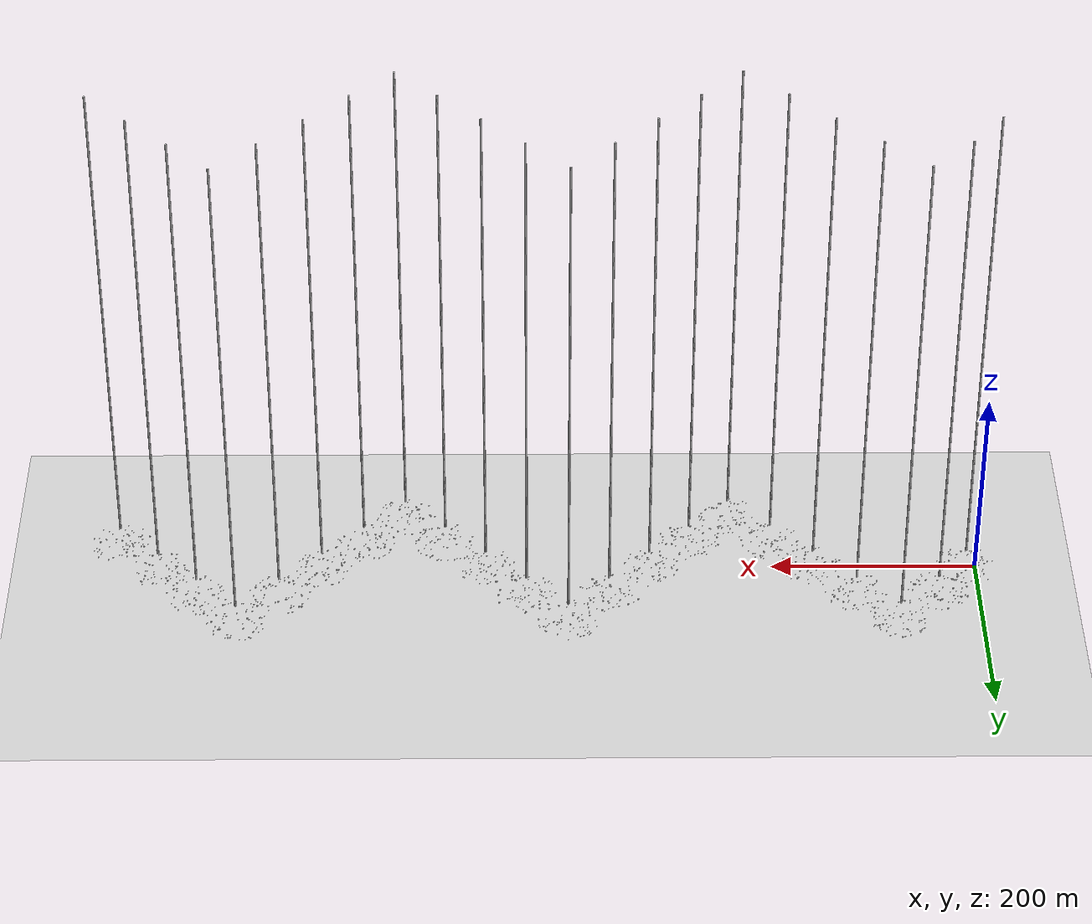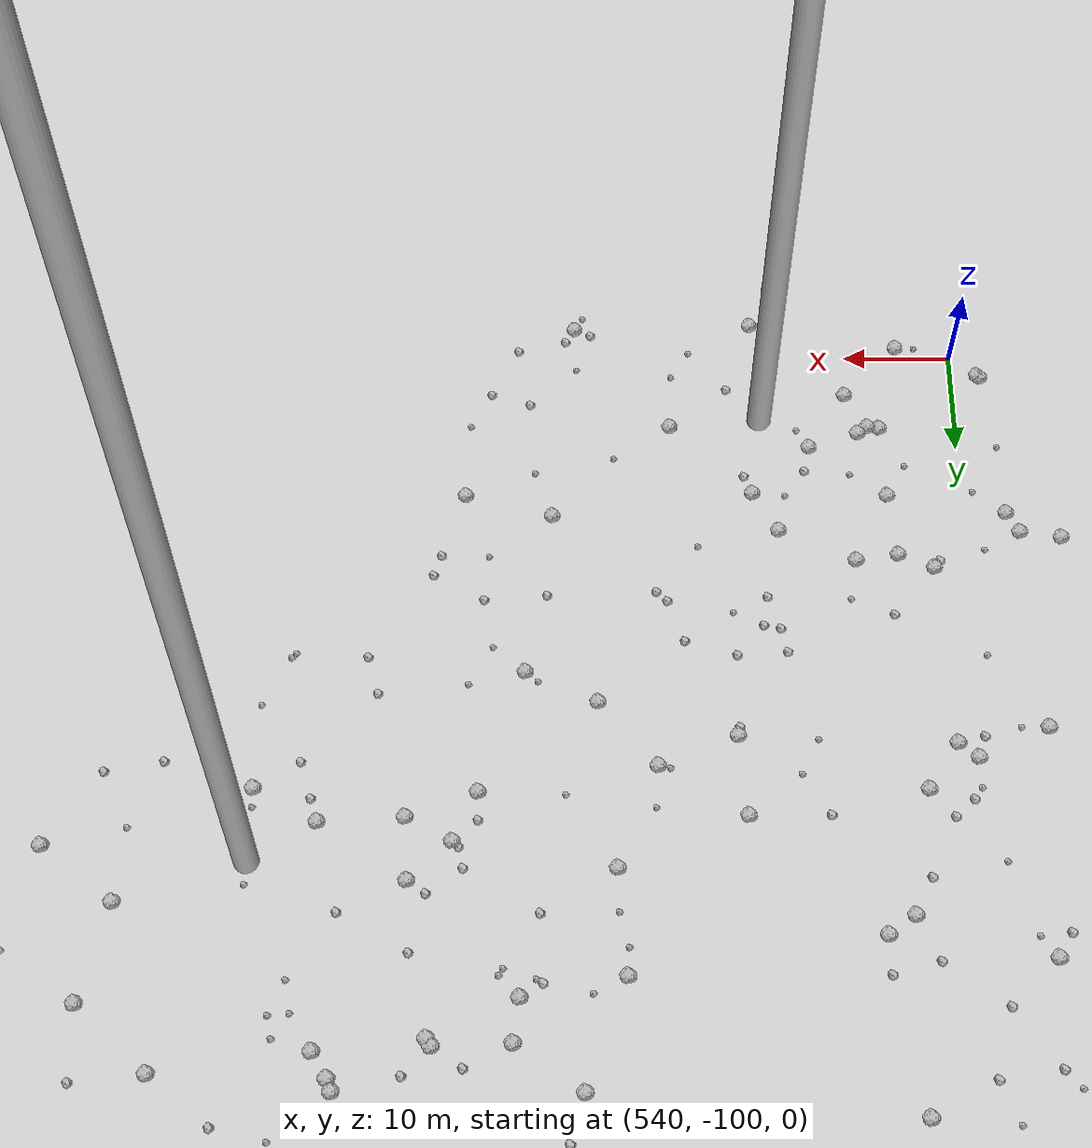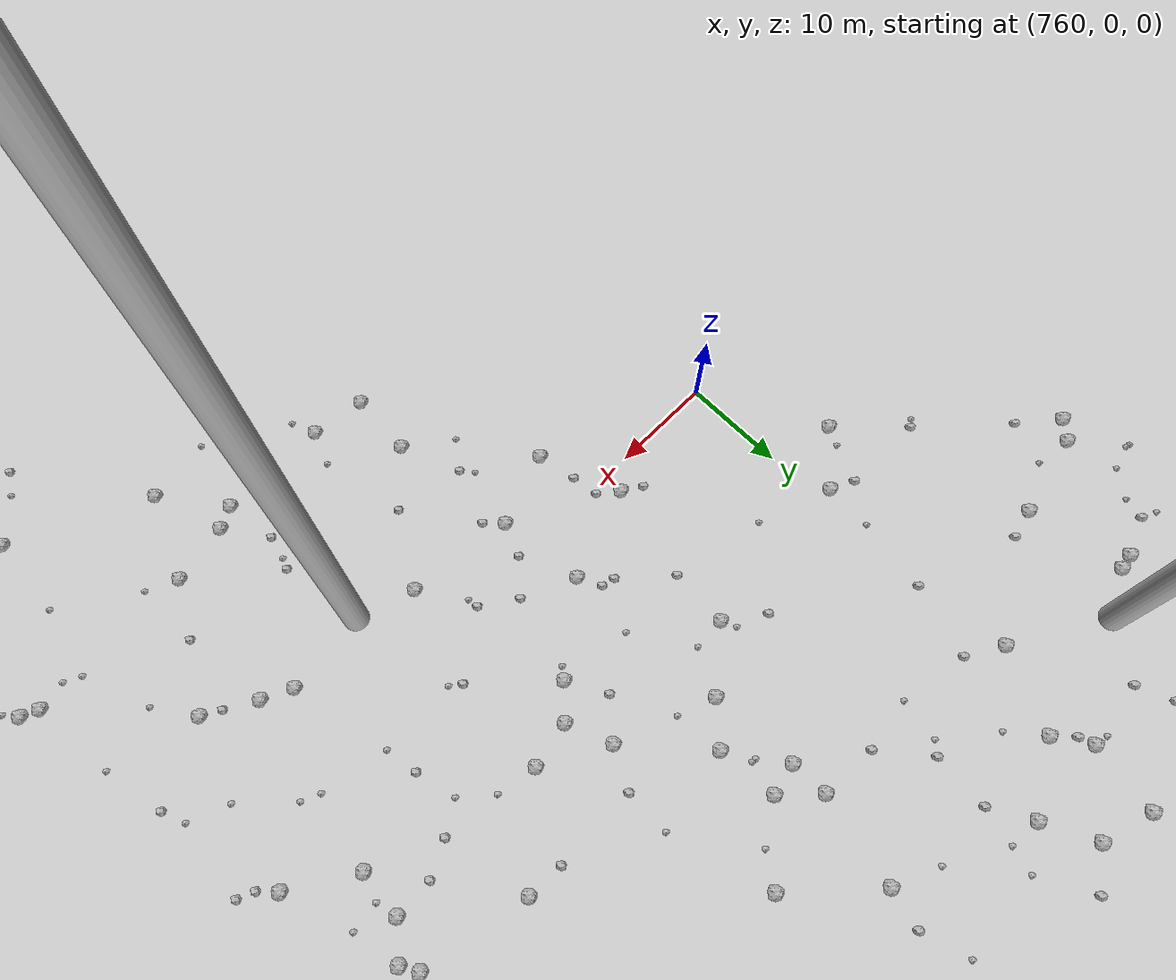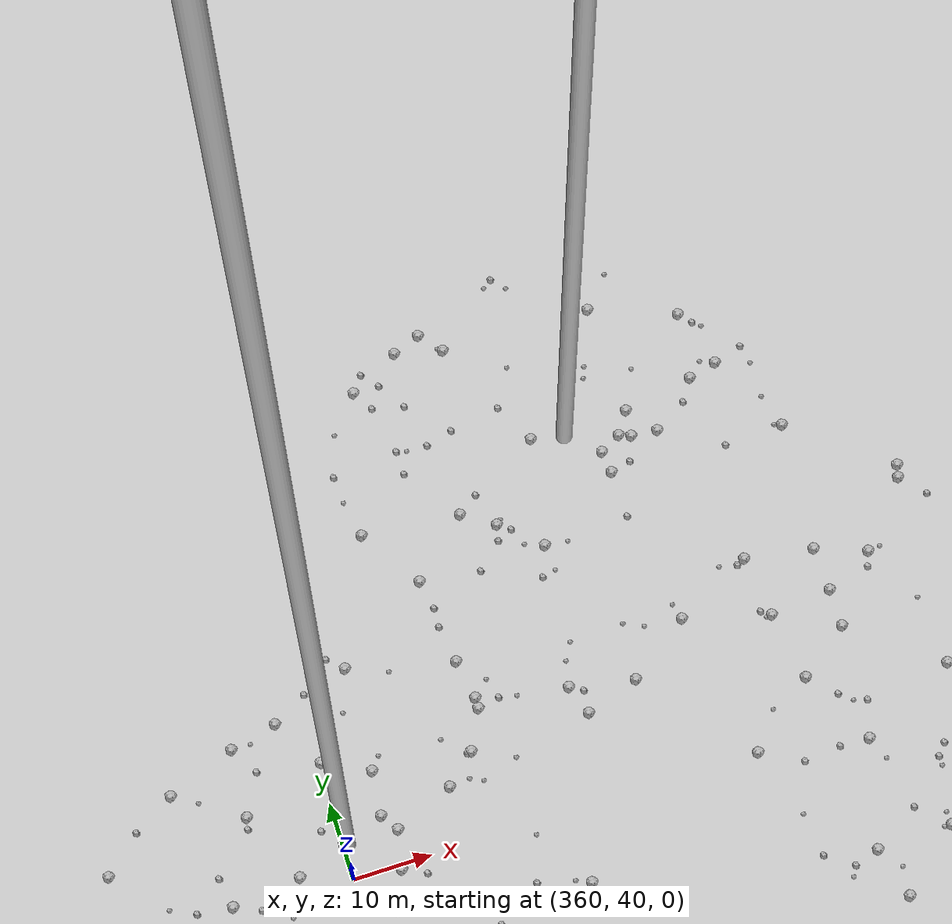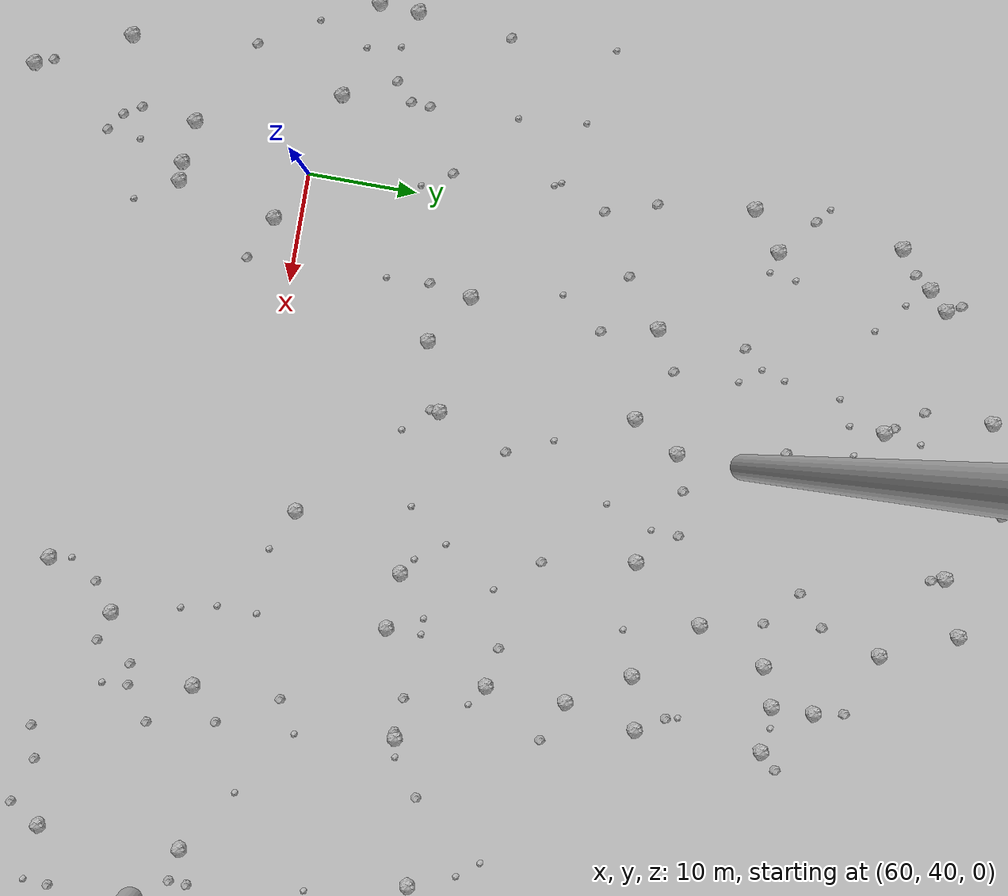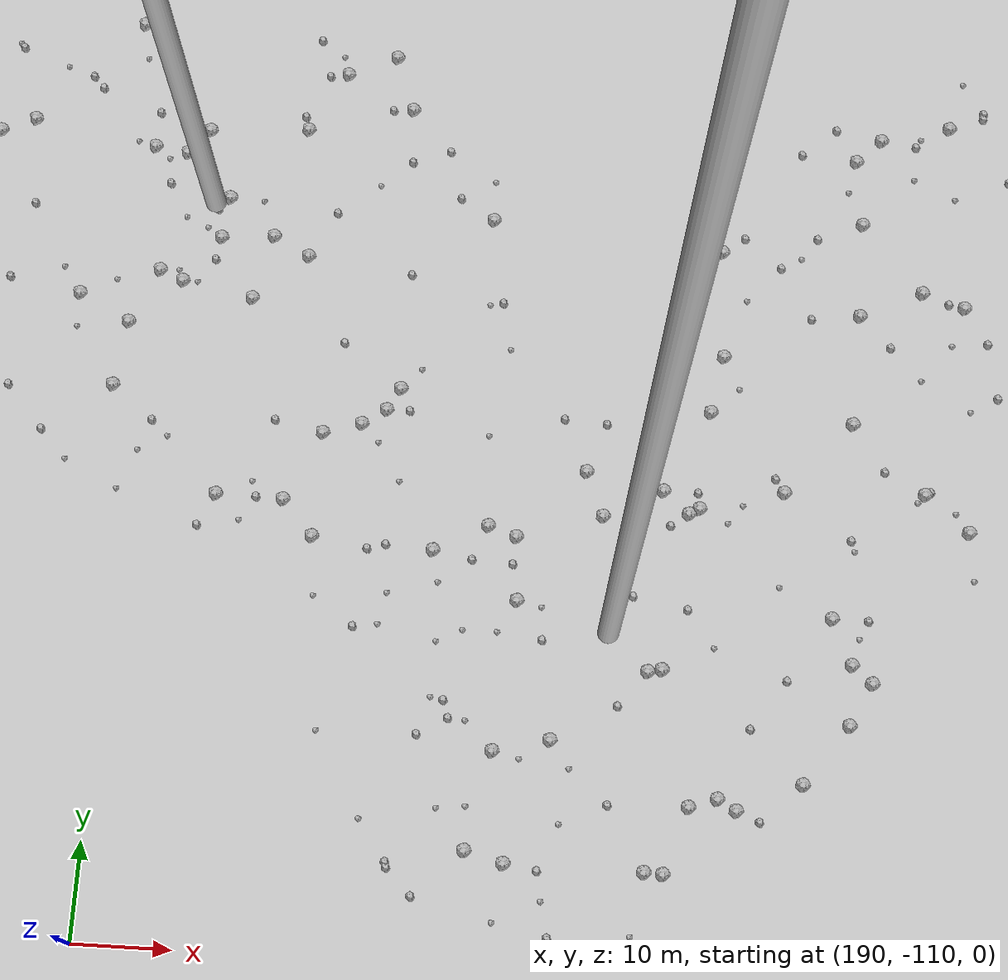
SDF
<sdf version="1.6">
 <world name="default">
  <include><uri>model://custom_ground</uri></include>
  <include><uri>model://sun</uri></include>
  <spherical_coordinates>
   <surface_model>EARTH_WGS84</surface_model>
   <latitude_deg>38.161479</latitude_deg>
   <longitude_deg>-122.454630</longitude_deg>
   <elevation>488.0</elevation>
   <heading_deg>90</heading_deg>
  </spherical_coordinates>
  <model name="rock1_0_0">
   <include><uri>model://rock1</uri><pose>0.9935185187853364 -6.503932943444923 0.5 0 0 0</pose></include>
  </model>
  <model name="rock1_0_1">
   <include><uri>model://rock1</uri><pose>36.758093230013216 -6.941084062376241 0.5 0 0 0</pose></include>
  </model>
  <model name="rock1_0_2">
   <include><uri>model://rock1</uri><pose>0.05145829908105526 -7.98412813386112 0.5 0 0 0</pose></include>
  </model>
  <model name="rock1_0_3">
   <include><uri>model://rock1</uri><pose>-2.7453775074032265 16.923458113375936 0.5 0 0 0</pose></include>
  </model>
  <model name="rock1_0_4">
   <include><uri>model://rock1</uri><pose>18.396231414767357 14.201627621543139 0.5 0 0 0</pose></include>
  </model>
  <model name="rock1_0_5">
   <include><uri>model://rock1</uri><pose>34.01812230619507 5.394185018060945 0.5 0 0 0</pose></include>
  </model>
  <model name="rock1_0_6">
   <include><uri>model://rock1</uri><pose>1.7370727873319112 -21.931574258012084 0.5 0 0 0</pose></include>
  </model>
  <model name="rock1_0_7">
   <include><uri>model://rock1</uri><pose>1.686179648115612 -20.035232182182654 0.5 0 0 0</pose></include>
  </model>
  <model name="rock1_0_8">
   <include><uri>model://rock1</uri><pose>18.912973151347877 16.987564073274086 0.5 0 0 0</pose></include>
  </model>
  <model name="rock1_0_9">
   <include><uri>model://rock1</uri><pose>11.84262653387811 26.806994615402616 0.5 0 0 0</pose></include>
  </model>
  <model name="rock1_0_10">
   <include><uri>model://rock1</uri><pose>11.83093446656165 -22.002242825853735 0.5 0 0 0</pose></include>
  </model>
  <model name="rock1_0_11">
   <include><uri>model://rock1</uri><pose>24.33388426134008 20.93147801118795 0.5 0 0 0</pose></include>
  </model>
  <model name="rock1_0_12">
   <include><uri>model://rock1</uri><pose>15.415270769079576 25.416421206683253 0.5 0 0 0</pose></include>
  </model>
  <model name="rock1_0_13">
   <include><uri>model://rock1</uri><pose>21.850337437310834 -24.754390922390836 0.5 0 0 0</pose></include>
  </model>
  <model name="rock1_0_14">
   <include><uri>model://rock1</uri><pose>-2.8841447516036034 -18.38125748219366 0.5 0 0 0</pose></include>
  </model>
  <model name="rock1_0_15">
   <include><uri>model://rock1</uri><pose>-7.942983325316881 -13.096045341482991 0.5 0 0 0</pose></include>
  </model>
  <model name="rock1_0_16">
   <include><uri>model://rock1</uri><pose>-5.48458424578126 -24.334589937606346 0.5 0 0 0</pose></include>
  </model>
  <model name="rock1_0_17">
   <include><uri>model://rock1</uri><pose>9.598328535303079 6.919934118916444 0.5 0 0 0</pose></include>
  </model>
  <model name="rock1_0_18">
   <include><uri>model://rock1</uri><pose>30.009805219220745 -20.046291285214508 0.5 0 0 0</pose></include>
  </model>
  <model name="rock1_0_19">
   <include><uri>model://rock1</uri><pose>-0.563832847708106 -7.312956350634192 0.5 0 0 0</pose></include>
  </model>
  <model name="rock1_0_20">
   <include><uri>model://rock1</uri><pose>29.806801564779427 -19.82549436107324 0.5 0 0 0</pose></include>
  </model>
  <model name="rock1_0_21">
   <include><uri>model://rock1</uri><pose>24.938658554413976 -7.440463109327901 0.5 0 0 0</pose></include>
  </model>
  <model name="rock1_0_22">
   <include><uri>model://rock1</uri><pose>16.384621273567255 -17.208731626027152 0.5 0 0 0</pose></include>
  </model>
  <model name="rock1_0_23">
   <include><uri>model://rock1</uri><pose>-12.720657431550443 -6.015691494433824 0.5 0 0 0</pose></include>
  </model>
  <model name="rock1_0_24">
   <include><uri>model://rock1</uri><pose>-9.489475196603772 -2.9012978600118764 0.5 0 0 0</pose></include>
  </model>
  <model name="rock1_0_25">
   <include><uri>model://rock1</uri><pose>1.7141970122254477 21.524658336492784 0.5 0 0 0</pose></include>
  </model>
  <model name="rock1_0_26">
   <include><uri>model://rock1</uri><pose>23.404421645676322 -17.59424791089056 0.5 0 0 0</pose></include>
  </model>
  <model name="rock2_0_0">
   <include><uri>model://rock2</uri><pose>19.211248343623666 11.977067162448385 0.3 0 0 0</pose></include>
  </model>
  <model name="rock2_0_1">
   <include><uri>model://rock2</uri><pose>17.581698931213353 16.212446086927564 0.3 0 0 0</pose></include>
  </model>
  <model name="rock2_0_2">
   <include><uri>model://rock2</uri><pose>-6.9559122397188755 5.7580406617748 0.3 0 0 0</pose></include>
  </model>
  <model name="rock2_0_3">
   <include><uri>model://rock2</uri><pose>17.315863838376316 -26.136937540721163 0.3 0 0 0</pose></include>
  </model>
  <model name="rock2_0_4">
   <include><uri>model://rock2</uri><pose>-5.740805090324439 -7.850220585391114 0.3 0 0 0</pose></include>
  </model>
  <model name="rock2_0_5">
   <include><uri>model://rock2</uri><pose>29.537958972303223 -5.532141630352495 0.3 0 0 0</pose></include>
  </model>
  <model name="rock2_0_6">
   <include><uri>model://rock2</uri><pose>36.40509371789391 1.2189443202846881 0.3 0 0 0</pose></include>
  </model>
  <model name="rock2_0_7">
   <include><uri>model://rock2</uri><pose>-17.456889790939584 -7.021497225326939 0.3 0 0 0</pose></include>
  </model>
  <model name="rock2_0_8">
   <include><uri>model://rock2</uri><pose>12.927838791504001 18.98520619321514 0.3 0 0 0</pose></include>
  </model>
  <model name="rock2_0_9">
   <include><uri>model://rock2</uri><pose>31.810134778722592 19.589451650094958 0.3 0 0 0</pose></include>
  </model>
  <model name="rock2_0_10">
   <include><uri>model://rock2</uri><pose>-5.892142689305999 9.195330199586394 0.3 0 0 0</pose></include>
  </model>
  <model name="rock2_0_11">
   <include><uri>model://rock2</uri><pose>7.591984622178163 -22.247086829618976 0.3 0 0 0</pose></include>
  </model>
  <model name="rock2_0_12">
   <include><uri>model://rock2</uri><pose>14.220608014251262 10.896580066515014 0.3 0 0 0</pose></include>
  </model>
  <model name="rock2_0_13">
   <include><uri>model://rock2</uri><pose>17.995212935071095 14.344292277809657 0.3 0 0 0</pose></include>
  </model>
  <model name="rock2_0_14">
   <include><uri>model://rock2</uri><pose>-6.9153188108519 13.59217624955815 0.3 0 0 0</pose></include>
  </model>
  <model name="rock2_0_15">
   <include><uri>model://rock2</uri><pose>32.29679647503118 5.4008700155324405 0.3 0 0 0</pose></include>
  </model>
  <model name="rock2_0_16">
   <include><uri>model://rock2</uri><pose>-8.59444163791311 -7.992750672687762 0.3 0 0 0</pose></include>
  </model>
  <model name="rock2_0_17">
   <include><uri>model://rock2</uri><pose>21.87562615949919 -16.760012653168687 0.3 0 0 0</pose></include>
  </model>
  <model name="rock2_0_18">
   <include><uri>model://rock2</uri><pose>27.231810281958737 -17.221721151020894 0.3 0 0 0</pose></include>
  </model>
  <model name="rock2_0_19">
   <include><uri>model://rock2</uri><pose>9.949817665201934 -15.58163137736396 0.3 0 0 0</pose></include>
  </model>
  <model name="rock2_0_20">
   <include><uri>model://rock2</uri><pose>-7.861953998362839 -23.323092360625175 0.3 0 0 0</pose></include>
  </model>
  <model name="rock2_0_21">
   <include><uri>model://rock2</uri><pose>-7.857603389803094 -11.331764729230319 0.3 0 0 0</pose></include>
  </model>
  <model name="rock2_0_22">
   <include><uri>model://rock2</uri><pose>24.44913786291211 -17.595516499051982 0.3 0 0 0</pose></include>
  </model>
  <model name="rock2_0_23">
   <include><uri>model://rock2</uri><pose>5.101124668397524 -17.16001354695869 0.3 0 0 0</pose></include>
  </model>
  <model name="rock2_0_24">
   <include><uri>model://rock2</uri><pose>23.03403276462499 16.68440478486353 0.3 0 0 0</pose></include>
  </model>
  <model name="rock2_0_25">
   <include><uri>model://rock2</uri><pose>-2.009678355146324 10.361864028304694 0.3 0 0 0</pose></include>
  </model>
  <model name="rock2_0_26">
   <include><uri>model://rock2</uri><pose>18.374447902361688 -12.832816053307774 0.3 0 0 0</pose></include>
  </model>
  <model name="rock3_0_0">
   <include><uri>model://rock3</uri><pose>-7.570488425720265 12.08515454729423 0.2 0 0 0</pose></include>
  </model>
  <model name="rock3_0_1">
   <include><uri>model://rock3</uri><pose>6.16618811341317 -16.271558035384636 0.2 0 0 0</pose></include>
  </model>
  <model name="rock3_0_2">
   <include><uri>model://rock3</uri><pose>3.0830619804530315 -22.475706322920523 0.2 0 0 0</pose></include>
  </model>
  <model name="rock3_0_3">
   <include><uri>model://rock3</uri><pose>32.27551462987189 15.95590398239979 0.2 0 0 0</pose></include>
  </model>
  <model name="rock3_0_4">
   <include><uri>model://rock3</uri><pose>16.63644793770034 18.798529536393453 0.2 0 0 0</pose></include>
  </model>
  <model name="rock3_0_5">
   <include><uri>model://rock3</uri><pose>20.842561354974947 10.511127970011685 0.2 0 0 0</pose></include>
  </model>
  <model name="rock3_0_6">
   <include><uri>model://rock3</uri><pose>-4.888778957872951 -21.834630259262084 0.2 0 0 0</pose></include>
  </model>
  <model name="rock3_0_7">
   <include><uri>model://rock3</uri><pose>-6.096281276102982 -8.223845503858978 0.2 0 0 0</pose></include>
  </model>
  <model name="rock3_0_8">
   <include><uri>model://rock3</uri><pose>19.414519082769516 -17.076978819866778 0.2 0 0 0</pose></include>
  </model>
  <model name="rock3_0_9">
   <include><uri>model://rock3</uri><pose>-4.0064503361425725 -0.9862866762400238 0.2 0 0 0</pose></include>
  </model>
  <model name="rock3_0_10">
   <include><uri>model://rock3</uri><pose>14.270397052646366 4.756402043196047 0.2 0 0 0</pose></include>
  </model>
  <model name="rock3_0_11">
   <include><uri>model://rock3</uri><pose>-4.251648347684728 -4.14322367079204 0.2 0 0 0</pose></include>
  </model>
  <model name="rock3_0_12">
   <include><uri>model://rock3</uri><pose>-18.01754932230953 -0.9500433631442107 0.2 0 0 0</pose></include>
  </model>
  <model name="rock3_0_13">
   <include><uri>model://rock3</uri><pose>11.326319352658224 16.23342653716832 0.2 0 0 0</pose></include>
  </model>
  <model name="rock3_0_14">
   <include><uri>model://rock3</uri><pose>-10.953929278845697 -3.934713330133075 0.2 0 0 0</pose></include>
  </model>
  <model name="rock3_0_15">
   <include><uri>model://rock3</uri><pose>27.22696576743209 2.1759339206640007 0.2 0 0 0</pose></include>
  </model>
  <model name="rock3_0_16">
   <include><uri>model://rock3</uri><pose>27.383855722573692 -5.811813841106211 0.2 0 0 0</pose></include>
  </model>
  <model name="rock3_0_17">
   <include><uri>model://rock3</uri><pose>22.12604286920326 3.1740469460788034 0.2 0 0 0</pose></include>
  </model>
  <model name="rock3_0_18">
   <include><uri>model://rock3</uri><pose>12.902362900665466 24.722773290449815 0.2 0 0 0</pose></include>
  </model>
  <model name="rock3_0_19">
   <include><uri>model://rock3</uri><pose>3.175607499609118 22.041268231248303 0.2 0 0 0</pose></include>
  </model>
  <model name="rock3_0_20">
   <include><uri>model://rock3</uri><pose>-2.3554053762022384 -5.559840742377386 0.2 0 0 0</pose></include>
  </model>
  <model name="rock3_0_21">
   <include><uri>model://rock3</uri><pose>9.874853671616957 11.41420369435712 0.2 0 0 0</pose></include>
  </model>
  <model name="rock3_0_22">
   <include><uri>model://rock3</uri><pose>24.168357236163587 -21.835212959996518 0.2 0 0 0</pose></include>
  </model>
  <model name="rock3_0_23">
   <include><uri>model://rock3</uri><pose>-10.633960894332242 21.02188482946889 0.2 0 0 0</pose></include>
  </model>
  <model name="rock3_0_24">
   <include><uri>model://rock3</uri><pose>28.241506541471352 18.274406586269038 0.2 0 0 0</pose></include>
  </model>
  <model name="rock3_0_25">
   <include><uri>model://rock3</uri><pose>5.97426817479127 23.386108699992768 0.2 0 0 0</pose></include>
  </model>
  <model name="rock3_0_26">
   <include><uri>model://rock3</uri><pose>32.313201645258545 -0.4177021549776292 0.2 0 0 0</pose></include>
  </model>
  <model name="rock1_1_0">
   <include><uri>model://rock1</uri><pose>62.63904165340712 28.559937863661467 0.5 0 0 0</pose></include>
  </model>
  <model name="rock1_1_1">
   <include><uri>model://rock1</uri><pose>40.716763958125114 52.040152540079546 0.5 0 0 0</pose></include>
  </model>
  <model name="rock1_1_2">
   <include><uri>model://rock1</uri><pose>11.402242424940521 46.552693772551216 0.5 0 0 0</pose></include>
  </model>
  <model name="rock1_1_3">
   <include><uri>model://rock1</uri><pose>24.721733710480795 45.75365900652473 0.5 0 0 0</pose></include>
  </model>
  <model name="rock1_1_4">
   <include><uri>model://rock1</uri><pose>17.81304106748218 47.963015345636066 0.5 0 0 0</pose></include>
  </model>
  <model name="rock1_1_5">
   <include><uri>model://rock1</uri><pose>22.512731723208432 22.096516845201116 0.5 0 0 0</pose></include>
  </model>
  <model name="rock1_1_6">
   <include><uri>model://rock1</uri><pose>38.642565719919304 52.96697396840552 0.5 0 0 0</pose></include>
  </model>
  <model name="rock1_1_7">
   <include><uri>model://rock1</uri><pose>54.3242558522289 13.75672944729079 0.5 0 0 0</pose></include>
  </model>
  <model name="rock1_1_8">
   <include><uri>model://rock1</uri><pose>11.270964253733773 32.31668680434802 0.5 0 0 0</pose></include>
  </model>
  <model name="rock1_1_9">
   <include><uri>model://rock1</uri><pose>43.83035863004112 47.453572089000964 0.5 0 0 0</pose></include>
  </model>
  <model name="rock1_1_10">
   <include><uri>model://rock1</uri><pose>38.98302201220427 22.869867466088927 0.5 0 0 0</pose></include>
  </model>
  <model name="rock1_1_11">
   <include><uri>model://rock1</uri><pose>35.605898310117276 11.976465230539548 0.5 0 0 0</pose></include>
  </model>
  <model name="rock1_1_12">
   <include><uri>model://rock1</uri><pose>20.421556587389894 21.902246939281277 0.5 0 0 0</pose></include>
  </model>
  <model name="rock1_1_13">
   <include><uri>model://rock1</uri><pose>14.047150232882382 45.43982479542997 0.5 0 0 0</pose></include>
  </model>
  <model name="rock1_1_14">
   <include><uri>model://rock1</uri><pose>21.34640971593569 56.456579279150084 0.5 0 0 0</pose></include>
  </model>
  <model name="rock1_1_15">
   <include><uri>model://rock1</uri><pose>52.49071825423359 41.87211750508557 0.5 0 0 0</pose></include>
  </model>
  <model name="rock1_1_16">
   <include><uri>model://rock1</uri><pose>32.55705643443436 65.50735161495794 0.5 0 0 0</pose></include>
  </model>
  <model name="rock1_1_17">
   <include><uri>model://rock1</uri><pose>43.61595249105597 43.85203764574743 0.5 0 0 0</pose></include>
  </model>
  <model name="rock1_1_18">
   <include><uri>model://rock1</uri><pose>64.54659690825338 37.64793386185811 0.5 0 0 0</pose></include>
  </model>
  <model name="rock1_1_19">
   <include><uri>model://rock1</uri><pose>57.07229180619788 29.085963572285237 0.5 0 0 0</pose></include>
  </model>
  <model name="rock1_1_20">
   <include><uri>model://rock1</uri><pose>60.950124935681686 28.542842908151293 0.5 0 0 0</pose></include>
  </model>
  <model name="rock1_1_21">
   <include><uri>model://rock1</uri><pose>34.738599492371236 33.64863446490591 0.5 0 0 0</pose></include>
  </model>
  <model name="rock1_1_22">
   <include><uri>model://rock1</uri><pose>36.81622774958742 51.31385145657625 0.5 0 0 0</pose></include>
  </model>
  <model name="rock1_1_23">
   <include><uri>model://rock1</uri><pose>41.73074417830799 46.48341296660096 0.5 0 0 0</pose></include>
  </model>
  <model name="rock1_1_24">
   <include><uri>model://rock1</uri><pose>16.14892960183856 34.412560733378584 0.5 0 0 0</pose></include>
  </model>
  <model name="rock1_1_25">
   <include><uri>model://rock1</uri><pose>50.30958946328741 22.121358839874084 0.5 0 0 0</pose></include>
  </model>
  <model name="rock1_1_26">
   <include><uri>model://rock1</uri><pose>24.87724800848608 35.007398300980576 0.5 0 0 0</pose></include>
  </model>
  <model name="rock2_1_0">
   <include><uri>model://rock2</uri><pose>25.59948543882274 20.116685108990495 0.3 0 0 0</pose></include>
  </model>
  <model name="rock2_1_1">
   <include><uri>model://rock2</uri><pose>26.97002576885967 55.38909745434583 0.3 0 0 0</pose></include>
  </model>
  <model name="rock2_1_2">
   <include><uri>model://rock2</uri><pose>57.7390596006499 53.072739140340644 0.3 0 0 0</pose></include>
  </model>
  <model name="rock2_1_3">
   <include><uri>model://rock2</uri><pose>57.473663546708956 22.45655898423528 0.3 0 0 0</pose></include>
  </model>
  <model name="rock2_1_4">
   <include><uri>model://rock2</uri><pose>20.04406285780257 29.632889327736244 0.3 0 0 0</pose></include>
  </model>
  <model name="rock2_1_5">
   <include><uri>model://rock2</uri><pose>50.28613876953459 46.630205686101064 0.3 0 0 0</pose></include>
  </model>
  <model name="rock2_1_6">
   <include><uri>model://rock2</uri><pose>38.240098086949686 38.71942042368603 0.3 0 0 0</pose></include>
  </model>
  <model name="rock2_1_7">
   <include><uri>model://rock2</uri><pose>21.16099113829223 46.919012244096955 0.3 0 0 0</pose></include>
  </model>
  <model name="rock2_1_8">
   <include><uri>model://rock2</uri><pose>30.96311353976322 55.17784938852589 0.3 0 0 0</pose></include>
  </model>
  <model name="rock2_1_9">
   <include><uri>model://rock2</uri><pose>49.06567418385926 33.4555310033118 0.3 0 0 0</pose></include>
  </model>
  <model name="rock2_1_10">
   <include><uri>model://rock2</uri><pose>40.11481419847065 15.826257853417376 0.3 0 0 0</pose></include>
  </model>
  <model name="rock2_1_11">
   <include><uri>model://rock2</uri><pose>11.958940625691547 48.636051979553194 0.3 0 0 0</pose></include>
  </model>
  <model name="rock2_1_12">
   <include><uri>model://rock2</uri><pose>51.95856150457646 48.19743691233638 0.3 0 0 0</pose></include>
  </model>
  <model name="rock2_1_13">
   <include><uri>model://rock2</uri><pose>59.10958304497396 21.252675762844103 0.3 0 0 0</pose></include>
  </model>
  <model name="rock2_1_14">
   <include><uri>model://rock2</uri><pose>44.31472725454097 30.679851664068714 0.3 0 0 0</pose></include>
  </model>
  <model name="rock2_1_15">
   <include><uri>model://rock2</uri><pose>68.48767488778874 35.79272091631424 0.3 0 0 0</pose></include>
  </model>
  <model name="rock2_1_16">
   <include><uri>model://rock2</uri><pose>24.009998375002894 35.195170758810846 0.3 0 0 0</pose></include>
  </model>
  <model name="rock2_1_17">
   <include><uri>model://rock2</uri><pose>56.54870275396697 24.0444081984605 0.3 0 0 0</pose></include>
  </model>
  <model name="rock2_1_18">
   <include><uri>model://rock2</uri><pose>23.526404791179694 30.921667363737033 0.3 0 0 0</pose></include>
  </model>
  <model name="rock2_1_19">
   <include><uri>model://rock2</uri><pose>12.233964635215672 46.87351279713134 0.3 0 0 0</pose></include>
  </model>
  <model name="rock2_1_20">
   <include><uri>model://rock2</uri><pose>16.37918266412798 35.82626457791625 0.3 0 0 0</pose></include>
  </model>
  <model name="rock2_1_21">
   <include><uri>model://rock2</uri><pose>44.64363780496379 56.230750670539685 0.3 0 0 0</pose></include>
  </model>
  <model name="rock2_1_22">
   <include><uri>model://rock2</uri><pose>18.322574661739303 56.74256392008172 0.3 0 0 0</pose></include>
  </model>
  <model name="rock2_1_23">
   <include><uri>model://rock2</uri><pose>23.83899498206322 50.29307908749867 0.3 0 0 0</pose></include>
  </model>
  <model name="rock2_1_24">
   <include><uri>model://rock2</uri><pose>53.63435349971303 15.37200287570754 0.3 0 0 0</pose></include>
  </model>
  <model name="rock2_1_25">
   <include><uri>model://rock2</uri><pose>17.421107581473457 40.044770820151314 0.3 0 0 0</pose></include>
  </model>
  <model name="rock2_1_26">
   <include><uri>model://rock2</uri><pose>52.07847590516192 49.95718865956038 0.3 0 0 0</pose></include>
  </model>
  <model name="rock3_1_0">
   <include><uri>model://rock3</uri><pose>28.117030910833677 40.61648106918699 0.2 0 0 0</pose></include>
  </model>
  <model name="rock3_1_1">
   <include><uri>model://rock3</uri><pose>43.29025633251341 17.790122067398862 0.2 0 0 0</pose></include>
  </model>
  <model name="rock3_1_2">
   <include><uri>model://rock3</uri><pose>34.37040964074626 42.70436556496032 0.2 0 0 0</pose></include>
  </model>
  <model name="rock3_1_3">
   <include><uri>model://rock3</uri><pose>51.76462016793603 58.074481109444626 0.2 0 0 0</pose></include>
  </model>
  <model name="rock3_1_4">
   <include><uri>model://rock3</uri><pose>47.7233238416498 43.30086169284636 0.2 0 0 0</pose></include>
  </model>
  <model name="rock3_1_5">
   <include><uri>model://rock3</uri><pose>45.68070155373863 10.962683300823898 0.2 0 0 0</pose></include>
  </model>
  <model name="rock3_1_6">
   <include><uri>model://rock3</uri><pose>33.508787973821825 37.098380939064306 0.2 0 0 0</pose></include>
  </model>
  <model name="rock3_1_7">
   <include><uri>model://rock3</uri><pose>22.20993868976545 39.04661649112296 0.2 0 0 0</pose></include>
  </model>
  <model name="rock3_1_8">
   <include><uri>model://rock3</uri><pose>18.77509123650462 46.80419978528434 0.2 0 0 0</pose></include>
  </model>
  <model name="rock3_1_9">
   <include><uri>model://rock3</uri><pose>39.358497150320886 12.556706363367276 0.2 0 0 0</pose></include>
  </model>
  <model name="rock3_1_10">
   <include><uri>model://rock3</uri><pose>59.44312539383862 24.28603250860369 0.2 0 0 0</pose></include>
  </model>
  <model name="rock3_1_11">
   <include><uri>model://rock3</uri><pose>45.945117594444795 38.710781465152316 0.2 0 0 0</pose></include>
  </model>
  <model name="rock3_1_12">
   <include><uri>model://rock3</uri><pose>25.07974225429347 38.791590962632085 0.2 0 0 0</pose></include>
  </model>
  <model name="rock3_1_13">
   <include><uri>model://rock3</uri><pose>27.257089742499797 62.92215379247139 0.2 0 0 0</pose></include>
  </model>
  <model name="rock3_1_14">
   <include><uri>model://rock3</uri><pose>30.703578400137843 48.24849203574567 0.2 0 0 0</pose></include>
  </model>
  <model name="rock3_1_15">
   <include><uri>model://rock3</uri><pose>56.92427547752347 62.95884192220525 0.2 0 0 0</pose></include>
  </model>
  <model name="rock3_1_16">
   <include><uri>model://rock3</uri><pose>47.139515340297095 46.3915597153018 0.2 0 0 0</pose></include>
  </model>
  <model name="rock3_1_17">
   <include><uri>model://rock3</uri><pose>51.14180381054374 64.30256780882264 0.2 0 0 0</pose></include>
  </model>
  <model name="rock3_1_18">
   <include><uri>model://rock3</uri><pose>32.740288094253714 58.5718478078941 0.2 0 0 0</pose></include>
  </model>
  <model name="rock3_1_19">
   <include><uri>model://rock3</uri><pose>43.43024292966152 34.424825225586915 0.2 0 0 0</pose></include>
  </model>
  <model name="rock3_1_20">
   <include><uri>model://rock3</uri><pose>38.80898467395531 66.71697688489166 0.2 0 0 0</pose></include>
  </model>
  <model name="rock3_1_21">
   <include><uri>model://rock3</uri><pose>39.210872157094684 23.376314247469807 0.2 0 0 0</pose></include>
  </model>
  <model name="rock3_1_22">
   <include><uri>model://rock3</uri><pose>44.11633128506174 65.87022885495759 0.2 0 0 0</pose></include>
  </model>
  <model name="rock3_1_23">
   <include><uri>model://rock3</uri><pose>64.94146439229687 24.625410456738784 0.2 0 0 0</pose></include>
  </model>
  <model name="rock3_1_24">
   <include><uri>model://rock3</uri><pose>19.533496606307793 47.52575656906655 0.2 0 0 0</pose></include>
  </model>
  <model name="rock3_1_25">
   <include><uri>model://rock3</uri><pose>59.30009938977887 50.32033292903249 0.2 0 0 0</pose></include>
  </model>
  <model name="rock3_1_26">
   <include><uri>model://rock3</uri><pose>68.11541308775497 48.62375669758457 0.2 0 0 0</pose></include>
  </model>
  <model name="rock1_2_0">
   <include><uri>model://rock1</uri><pose>79.45411528735761 55.501351149187045 0.5 0 0 0</pose></include>
  </model>
  <model name="rock1_2_1">
   <include><uri>model://rock1</uri><pose>79.56198879731403 77.55023633425351 0.5 0 0 0</pose></include>
  </model>
  <model name="rock1_2_2">
   <include><uri>model://rock1</uri><pose>77.07298109080985 73.23537945463066 0.5 0 0 0</pose></include>
  </model>
  <model name="rock1_2_3">
   <include><uri>model://rock1</uri><pose>97.36551136166611 88.62304608718193 0.5 0 0 0</pose></include>
  </model>
  <model name="rock1_2_4">
   <include><uri>model://rock1</uri><pose>103.65056391949986 71.3584845780202 0.5 0 0 0</pose></include>
  </model>
  <model name="rock1_2_5">
   <include><uri>model://rock1</uri><pose>100.8400570265654 93.82226605235077 0.5 0 0 0</pose></include>
  </model>
  <model name="rock1_2_6">
   <include><uri>model://rock1</uri><pose>94.65894703044907 82.23131598062051 0.5 0 0 0</pose></include>
  </model>
  <model name="rock1_2_7">
   <include><uri>model://rock1</uri><pose>73.27105248028624 53.39717354901596 0.5 0 0 0</pose></include>
  </model>
  <model name="rock1_2_8">
   <include><uri>model://rock1</uri><pose>74.48758436766627 95.85460126168559 0.5 0 0 0</pose></include>
  </model>
  <model name="rock1_2_9">
   <include><uri>model://rock1</uri><pose>79.94637060157326 107.6675945558884 0.5 0 0 0</pose></include>
  </model>
  <model name="rock1_2_10">
   <include><uri>model://rock1</uri><pose>89.94932243383403 75.54635252331559 0.5 0 0 0</pose></include>
  </model>
  <model name="rock1_2_11">
   <include><uri>model://rock1</uri><pose>62.5926738630245 99.51973650231739 0.5 0 0 0</pose></include>
  </model>
  <model name="rock1_2_12">
   <include><uri>model://rock1</uri><pose>68.65178146493031 56.57285977058772 0.5 0 0 0</pose></include>
  </model>
  <model name="rock1_2_13">
   <include><uri>model://rock1</uri><pose>59.858367791572135 83.53910247630488 0.5 0 0 0</pose></include>
  </model>
  <model name="rock1_2_14">
   <include><uri>model://rock1</uri><pose>71.98549700624483 105.4612780379787 0.5 0 0 0</pose></include>
  </model>
  <model name="rock1_2_15">
   <include><uri>model://rock1</uri><pose>91.68767297559842 105.67136167547724 0.5 0 0 0</pose></include>
  </model>
  <model name="rock1_2_16">
   <include><uri>model://rock1</uri><pose>105.09262938734952 89.69242145298611 0.5 0 0 0</pose></include>
  </model>
  <model name="rock1_2_17">
   <include><uri>model://rock1</uri><pose>77.47233372133633 106.95456125015043 0.5 0 0 0</pose></include>
  </model>
  <model name="rock1_2_18">
   <include><uri>model://rock1</uri><pose>94.6272831999892 98.84053603165046 0.5 0 0 0</pose></include>
  </model>
  <model name="rock1_2_19">
   <include><uri>model://rock1</uri><pose>100.26162478216746 76.93310109221794 0.5 0 0 0</pose></include>
  </model>
  <model name="rock1_2_20">
   <include><uri>model://rock1</uri><pose>57.65472178697423 94.65511862473517 0.5 0 0 0</pose></include>
  </model>
  <model name="rock1_2_21">
   <include><uri>model://rock1</uri><pose>56.36281414701668 80.7644049865784 0.5 0 0 0</pose></include>
  </model>
  <model name="rock1_2_22">
   <include><uri>model://rock1</uri><pose>105.0837718323852 78.0173297956749 0.5 0 0 0</pose></include>
  </model>
  <model name="rock1_2_23">
   <include><uri>model://rock1</uri><pose>86.69373341474152 103.55731887260562 0.5 0 0 0</pose></include>
  </model>
  <model name="rock1_2_24">
   <include><uri>model://rock1</uri><pose>68.62863328141901 73.90738172583318 0.5 0 0 0</pose></include>
  </model>
  <model name="rock1_2_25">
   <include><uri>model://rock1</uri><pose>100.89381187622843 89.94355498966854 0.5 0 0 0</pose></include>
  </model>
  <model name="rock1_2_26">
   <include><uri>model://rock1</uri><pose>60.90315917013663 97.78202038913216 0.5 0 0 0</pose></include>
  </model>
  <model name="rock2_2_0">
   <include><uri>model://rock2</uri><pose>82.0323973210934 62.13307186003082 0.3 0 0 0</pose></include>
  </model>
  <model name="rock2_2_1">
   <include><uri>model://rock2</uri><pose>82.82481556712074 78.70905385503734 0.3 0 0 0</pose></include>
  </model>
  <model name="rock2_2_2">
   <include><uri>model://rock2</uri><pose>57.36180413424801 71.96757701998996 0.3 0 0 0</pose></include>
  </model>
  <model name="rock2_2_3">
   <include><uri>model://rock2</uri><pose>71.9937895800573 99.29806042039829 0.3 0 0 0</pose></include>
  </model>
  <model name="rock2_2_4">
   <include><uri>model://rock2</uri><pose>73.91332475826988 96.79872004439967 0.3 0 0 0</pose></include>
  </model>
  <model name="rock2_2_5">
   <include><uri>model://rock2</uri><pose>91.40227800174233 67.06172370753232 0.3 0 0 0</pose></include>
  </model>
  <model name="rock2_2_6">
   <include><uri>model://rock2</uri><pose>68.9927087658097 82.11248856935035 0.3 0 0 0</pose></include>
  </model>
  <model name="rock2_2_7">
   <include><uri>model://rock2</uri><pose>92.98069677761441 93.32287706460981 0.3 0 0 0</pose></include>
  </model>
  <model name="rock2_2_8">
   <include><uri>model://rock2</uri><pose>107.46223781517088 69.66832628301603 0.3 0 0 0</pose></include>
  </model>
  <model name="rock2_2_9">
   <include><uri>model://rock2</uri><pose>93.49156225262189 88.00874052952263 0.3 0 0 0</pose></include>
  </model>
  <model name="rock2_2_10">
   <include><uri>model://rock2</uri><pose>87.04117352691543 102.4155626118095 0.3 0 0 0</pose></include>
  </model>
  <model name="rock2_2_11">
   <include><uri>model://rock2</uri><pose>58.82900084614427 67.31445241778215 0.3 0 0 0</pose></include>
  </model>
  <model name="rock2_2_12">
   <include><uri>model://rock2</uri><pose>69.68999312576508 68.80401771206502 0.3 0 0 0</pose></include>
  </model>
  <model name="rock2_2_13">
   <include><uri>model://rock2</uri><pose>61.87427856405284 100.94843755371758 0.3 0 0 0</pose></include>
  </model>
  <model name="rock2_2_14">
   <include><uri>model://rock2</uri><pose>59.723307446714685 96.33392478205045 0.3 0 0 0</pose></include>
  </model>
  <model name="rock2_2_15">
   <include><uri>model://rock2</uri><pose>72.2004291369087 76.0174166752409 0.3 0 0 0</pose></include>
  </model>
  <model name="rock2_2_16">
   <include><uri>model://rock2</uri><pose>106.5383015020144 91.31384085271102 0.3 0 0 0</pose></include>
  </model>
  <model name="rock2_2_17">
   <include><uri>model://rock2</uri><pose>100.40907291758111 96.6635000810319 0.3 0 0 0</pose></include>
  </model>
  <model name="rock2_2_18">
   <include><uri>model://rock2</uri><pose>103.57842270070623 80.65043530958539 0.3 0 0 0</pose></include>
  </model>
  <model name="rock2_2_19">
   <include><uri>model://rock2</uri><pose>64.2943106174301 70.54338185688394 0.3 0 0 0</pose></include>
  </model>
  <model name="rock2_2_20">
   <include><uri>model://rock2</uri><pose>99.84105910832366 64.54649199403542 0.3 0 0 0</pose></include>
  </model>
  <model name="rock2_2_21">
   <include><uri>model://rock2</uri><pose>86.92256621620106 78.99336419943393 0.3 0 0 0</pose></include>
  </model>
  <model name="rock2_2_22">
   <include><uri>model://rock2</uri><pose>56.49150621576641 86.53274128788857 0.3 0 0 0</pose></include>
  </model>
  <model name="rock2_2_23">
   <include><uri>model://rock2</uri><pose>67.97762800984506 52.66554985933489 0.3 0 0 0</pose></include>
  </model>
  <model name="rock2_2_24">
   <include><uri>model://rock2</uri><pose>90.22138730577711 90.84071763410644 0.3 0 0 0</pose></include>
  </model>
  <model name="rock2_2_25">
   <include><uri>model://rock2</uri><pose>77.80514897809871 87.44214183527787 0.3 0 0 0</pose></include>
  </model>
  <model name="rock2_2_26">
   <include><uri>model://rock2</uri><pose>79.39675074657939 54.72100128024843 0.3 0 0 0</pose></include>
  </model>
  <model name="rock3_2_0">
   <include><uri>model://rock3</uri><pose>93.11122958369957 55.52371621841846 0.2 0 0 0</pose></include>
  </model>
  <model name="rock3_2_1">
   <include><uri>model://rock3</uri><pose>71.30405825978643 86.13749988905688 0.2 0 0 0</pose></include>
  </model>
  <model name="rock3_2_2">
   <include><uri>model://rock3</uri><pose>70.6464310689017 83.93671180063909 0.2 0 0 0</pose></include>
  </model>
  <model name="rock3_2_3">
   <include><uri>model://rock3</uri><pose>86.8178611182513 76.42879641121556 0.2 0 0 0</pose></include>
  </model>
  <model name="rock3_2_4">
   <include><uri>model://rock3</uri><pose>94.62734857344464 63.14097286756842 0.2 0 0 0</pose></include>
  </model>
  <model name="rock3_2_5">
   <include><uri>model://rock3</uri><pose>80.24666997644114 66.27237794188568 0.2 0 0 0</pose></include>
  </model>
  <model name="rock3_2_6">
   <include><uri>model://rock3</uri><pose>103.3319297617925 81.72442940945557 0.2 0 0 0</pose></include>
  </model>
  <model name="rock3_2_7">
   <include><uri>model://rock3</uri><pose>74.93798945088031 99.42208518039698 0.2 0 0 0</pose></include>
  </model>
  <model name="rock3_2_8">
   <include><uri>model://rock3</uri><pose>55.14068046338965 87.63631246135203 0.2 0 0 0</pose></include>
  </model>
  <model name="rock3_2_9">
   <include><uri>model://rock3</uri><pose>61.757107096273195 83.13156411275523 0.2 0 0 0</pose></include>
  </model>
  <model name="rock3_2_10">
   <include><uri>model://rock3</uri><pose>74.3550843623429 92.69195267829 0.2 0 0 0</pose></include>
  </model>
  <model name="rock3_2_11">
   <include><uri>model://rock3</uri><pose>88.38253698991281 54.42588098565327 0.2 0 0 0</pose></include>
  </model>
  <model name="rock3_2_12">
   <include><uri>model://rock3</uri><pose>98.32175686893797 57.27189613556964 0.2 0 0 0</pose></include>
  </model>
  <model name="rock3_2_13">
   <include><uri>model://rock3</uri><pose>76.96106954721098 93.53039296234827 0.2 0 0 0</pose></include>
  </model>
  <model name="rock3_2_14">
   <include><uri>model://rock3</uri><pose>72.06613410074426 91.41102812157692 0.2 0 0 0</pose></include>
  </model>
  <model name="rock3_2_15">
   <include><uri>model://rock3</uri><pose>78.32658135160806 95.79078187989282 0.2 0 0 0</pose></include>
  </model>
  <model name="rock3_2_16">
   <include><uri>model://rock3</uri><pose>57.24419551259973 62.334903723452804 0.2 0 0 0</pose></include>
  </model>
  <model name="rock3_2_17">
   <include><uri>model://rock3</uri><pose>72.1113929664656 82.02549198704835 0.2 0 0 0</pose></include>
  </model>
  <model name="rock3_2_18">
   <include><uri>model://rock3</uri><pose>62.08258812330643 85.59158981407454 0.2 0 0 0</pose></include>
  </model>
  <model name="rock3_2_19">
   <include><uri>model://rock3</uri><pose>85.13792314767261 72.01570336297357 0.2 0 0 0</pose></include>
  </model>
  <model name="rock3_2_20">
   <include><uri>model://rock3</uri><pose>96.21957072155779 75.43485148690323 0.2 0 0 0</pose></include>
  </model>
  <model name="rock3_2_21">
   <include><uri>model://rock3</uri><pose>81.63643538607418 52.37550347816555 0.2 0 0 0</pose></include>
  </model>
  <model name="rock3_2_22">
   <include><uri>model://rock3</uri><pose>65.40390376809142 93.49502012362359 0.2 0 0 0</pose></include>
  </model>
  <model name="rock3_2_23">
   <include><uri>model://rock3</uri><pose>91.27177939789013 58.147934212259344 0.2 0 0 0</pose></include>
  </model>
  <model name="rock3_2_24">
   <include><uri>model://rock3</uri><pose>66.9600903193496 64.82960677083366 0.2 0 0 0</pose></include>
  </model>
  <model name="rock3_2_25">
   <include><uri>model://rock3</uri><pose>62.61705354366093 95.90110587317037 0.2 0 0 0</pose></include>
  </model>
  <model name="rock3_2_26">
   <include><uri>model://rock3</uri><pose>102.84531526960384 90.22359929779577 0.2 0 0 0</pose></include>
  </model>
  <model name="rock1_3_0">
   <include><uri>model://rock1</uri><pose>138.05928979128245 50.452477844889245 0.5 0 0 0</pose></include>
  </model>
  <model name="rock1_3_1">
   <include><uri>model://rock1</uri><pose>122.63838994369564 60.01561387597881 0.5 0 0 0</pose></include>
  </model>
  <model name="rock1_3_2">
   <include><uri>model://rock1</uri><pose>107.89466225078706 37.607912673081884 0.5 0 0 0</pose></include>
  </model>
  <model name="rock1_3_3">
   <include><uri>model://rock1</uri><pose>127.81796405204352 46.03249434539394 0.5 0 0 0</pose></include>
  </model>
  <model name="rock1_3_4">
   <include><uri>model://rock1</uri><pose>131.8732001065984 65.87197135222867 0.5 0 0 0</pose></include>
  </model>
  <model name="rock1_3_5">
   <include><uri>model://rock1</uri><pose>142.83175551257796 43.88480066322547 0.5 0 0 0</pose></include>
  </model>
  <model name="rock1_3_6">
   <include><uri>model://rock1</uri><pose>131.97570340459274 35.14009707249495 0.5 0 0 0</pose></include>
  </model>
  <model name="rock1_3_7">
   <include><uri>model://rock1</uri><pose>103.43025870041839 63.95604089882503 0.5 0 0 0</pose></include>
  </model>
  <model name="rock1_3_8">
   <include><uri>model://rock1</uri><pose>133.28127552892005 55.11105112425869 0.5 0 0 0</pose></include>
  </model>
  <model name="rock1_3_9">
   <include><uri>model://rock1</uri><pose>98.54406345580182 22.72354868363046 0.5 0 0 0</pose></include>
  </model>
  <model name="rock1_3_10">
   <include><uri>model://rock1</uri><pose>141.1742539500312 47.16962345977059 0.5 0 0 0</pose></include>
  </model>
  <model name="rock1_3_11">
   <include><uri>model://rock1</uri><pose>122.40183889220496 20.20996202922507 0.5 0 0 0</pose></include>
  </model>
  <model name="rock1_3_12">
   <include><uri>model://rock1</uri><pose>103.2675697591047 16.01688390208552 0.5 0 0 0</pose></include>
  </model>
  <model name="rock1_3_13">
   <include><uri>model://rock1</uri><pose>102.54799678632311 29.129190768347396 0.5 0 0 0</pose></include>
  </model>
  <model name="rock1_3_14">
   <include><uri>model://rock1</uri><pose>109.52360531460641 56.58518503832795 0.5 0 0 0</pose></include>
  </model>
  <model name="rock1_3_15">
   <include><uri>model://rock1</uri><pose>94.58979826491111 54.51634579602003 0.5 0 0 0</pose></include>
  </model>
  <model name="rock1_3_16">
   <include><uri>model://rock1</uri><pose>134.15293833997703 32.137938018812136 0.5 0 0 0</pose></include>
  </model>
  <model name="rock1_3_17">
   <include><uri>model://rock1</uri><pose>99.73297988852393 54.109824607932104 0.5 0 0 0</pose></include>
  </model>
  <model name="rock1_3_18">
   <include><uri>model://rock1</uri><pose>122.83235564732749 25.85586194839529 0.5 0 0 0</pose></include>
  </model>
  <model name="rock1_3_19">
   <include><uri>model://rock1</uri><pose>117.56508861692751 16.71216855909108 0.5 0 0 0</pose></include>
  </model>
  <model name="rock1_3_20">
   <include><uri>model://rock1</uri><pose>136.51981460007283 35.33685015217691 0.5 0 0 0</pose></include>
  </model>
  <model name="rock1_3_21">
   <include><uri>model://rock1</uri><pose>107.22818815379124 15.652350808767206 0.5 0 0 0</pose></include>
  </model>
  <model name="rock1_3_22">
   <include><uri>model://rock1</uri><pose>122.82565046075268 38.92865063856135 0.5 0 0 0</pose></include>
  </model>
  <model name="rock1_3_23">
   <include><uri>model://rock1</uri><pose>135.45496599753545 16.60619419442951 0.5 0 0 0</pose></include>
  </model>
  <model name="rock1_3_24">
   <include><uri>model://rock1</uri><pose>144.82186970878993 54.663274841820474 0.5 0 0 0</pose></include>
  </model>
  <model name="rock1_3_25">
   <include><uri>model://rock1</uri><pose>136.19592312943846 38.789907523438806 0.5 0 0 0</pose></include>
  </model>
  <model name="rock1_3_26">
   <include><uri>model://rock1</uri><pose>90.59482160492125 44.13703625476236 0.5 0 0 0</pose></include>
  </model>
  <model name="rock2_3_0">
   <include><uri>model://rock2</uri><pose>133.82653825958045 64.0871769203289 0.3 0 0 0</pose></include>
  </model>
  <model name="rock2_3_1">
   <include><uri>model://rock2</uri><pose>125.98066245499783 40.069240623630364 0.3 0 0 0</pose></include>
  </model>
  <model name="rock2_3_2">
   <include><uri>model://rock2</uri><pose>108.85929825574367 31.702575128102776 0.3 0 0 0</pose></include>
  </model>
  <model name="rock2_3_3">
   <include><uri>model://rock2</uri><pose>105.8021645734471 56.753236319221244 0.3 0 0 0</pose></include>
  </model>
  <model name="rock2_3_4">
   <include><uri>model://rock2</uri><pose>131.66362989359573 43.3883173069261 0.3 0 0 0</pose></include>
  </model>
  <model name="rock2_3_5">
   <include><uri>model://rock2</uri><pose>114.56497657345881 59.39925101849436 0.3 0 0 0</pose></include>
  </model>
  <model name="rock2_3_6">
   <include><uri>model://rock2</uri><pose>106.91333077172195 31.579710548025947 0.3 0 0 0</pose></include>
  </model>
  <model name="rock2_3_7">
   <include><uri>model://rock2</uri><pose>149.67586525529367 39.570990732247665 0.3 0 0 0</pose></include>
  </model>
  <model name="rock2_3_8">
   <include><uri>model://rock2</uri><pose>107.79511468288939 45.651581469964604 0.3 0 0 0</pose></include>
  </model>
  <model name="rock2_3_9">
   <include><uri>model://rock2</uri><pose>130.16568864303048 40.79320978712472 0.3 0 0 0</pose></include>
  </model>
  <model name="rock2_3_10">
   <include><uri>model://rock2</uri><pose>113.96757235458158 23.643049823544025 0.3 0 0 0</pose></include>
  </model>
  <model name="rock2_3_11">
   <include><uri>model://rock2</uri><pose>129.11820885272002 20.859507042660635 0.3 0 0 0</pose></include>
  </model>
  <model name="rock2_3_12">
   <include><uri>model://rock2</uri><pose>131.65394654295602 43.35389353695662 0.3 0 0 0</pose></include>
  </model>
  <model name="rock2_3_13">
   <include><uri>model://rock2</uri><pose>125.88437914080535 38.4234879891386 0.3 0 0 0</pose></include>
  </model>
  <model name="rock2_3_14">
   <include><uri>model://rock2</uri><pose>105.27539229571079 28.25568812377152 0.3 0 0 0</pose></include>
  </model>
  <model name="rock2_3_15">
   <include><uri>model://rock2</uri><pose>121.14358433683549 22.975938961117002 0.3 0 0 0</pose></include>
  </model>
  <model name="rock2_3_16">
   <include><uri>model://rock2</uri><pose>127.54049371642398 52.31944835342047 0.3 0 0 0</pose></include>
  </model>
  <model name="rock2_3_17">
   <include><uri>model://rock2</uri><pose>129.81939311133135 65.98808538023485 0.3 0 0 0</pose></include>
  </model>
  <model name="rock2_3_18">
   <include><uri>model://rock2</uri><pose>140.75635159989673 44.99182093208246 0.3 0 0 0</pose></include>
  </model>
  <model name="rock2_3_19">
   <include><uri>model://rock2</uri><pose>111.9031009277872 33.943057651694154 0.3 0 0 0</pose></include>
  </model>
  <model name="rock2_3_20">
   <include><uri>model://rock2</uri><pose>108.94269227164071 56.4223559659003 0.3 0 0 0</pose></include>
  </model>
  <model name="rock2_3_21">
   <include><uri>model://rock2</uri><pose>116.94219958241193 24.436752496141047 0.3 0 0 0</pose></include>
  </model>
  <model name="rock2_3_22">
   <include><uri>model://rock2</uri><pose>124.59763876327185 65.09982254679248 0.3 0 0 0</pose></include>
  </model>
  <model name="rock2_3_23">
   <include><uri>model://rock2</uri><pose>99.997767153879 27.224335775460432 0.3 0 0 0</pose></include>
  </model>
  <model name="rock2_3_24">
   <include><uri>model://rock2</uri><pose>110.86327843703069 40.18442336771863 0.3 0 0 0</pose></include>
  </model>
  <model name="rock2_3_25">
   <include><uri>model://rock2</uri><pose>128.11409826416352 27.561559978264043 0.3 0 0 0</pose></include>
  </model>
  <model name="rock2_3_26">
   <include><uri>model://rock2</uri><pose>144.57385511372692 51.92220389935176 0.3 0 0 0</pose></include>
  </model>
  <model name="rock3_3_0">
   <include><uri>model://rock3</uri><pose>147.13536718548949 49.28698638398058 0.2 0 0 0</pose></include>
  </model>
  <model name="rock3_3_1">
   <include><uri>model://rock3</uri><pose>119.49244649072112 66.17662947628023 0.2 0 0 0</pose></include>
  </model>
  <model name="rock3_3_2">
   <include><uri>model://rock3</uri><pose>124.71487505654805 50.69665983740295 0.2 0 0 0</pose></include>
  </model>
  <model name="rock3_3_3">
   <include><uri>model://rock3</uri><pose>116.94674437821062 42.96074891077873 0.2 0 0 0</pose></include>
  </model>
  <model name="rock3_3_4">
   <include><uri>model://rock3</uri><pose>138.23246037771258 46.72812728591546 0.2 0 0 0</pose></include>
  </model>
  <model name="rock3_3_5">
   <include><uri>model://rock3</uri><pose>111.26516958723258 56.85247590442104 0.2 0 0 0</pose></include>
  </model>
  <model name="rock3_3_6">
   <include><uri>model://rock3</uri><pose>127.99697968261022 25.19879686282758 0.2 0 0 0</pose></include>
  </model>
  <model name="rock3_3_7">
   <include><uri>model://rock3</uri><pose>128.52341463972016 55.067638801836964 0.2 0 0 0</pose></include>
  </model>
  <model name="rock3_3_8">
   <include><uri>model://rock3</uri><pose>134.55768752108835 61.89075505844838 0.2 0 0 0</pose></include>
  </model>
  <model name="rock3_3_9">
   <include><uri>model://rock3</uri><pose>141.6967779718392 45.50554560728072 0.2 0 0 0</pose></include>
  </model>
  <model name="rock3_3_10">
   <include><uri>model://rock3</uri><pose>105.37578076407493 62.641905289185274 0.2 0 0 0</pose></include>
  </model>
  <model name="rock3_3_11">
   <include><uri>model://rock3</uri><pose>100.37098951846814 38.48152323231214 0.2 0 0 0</pose></include>
  </model>
  <model name="rock3_3_12">
   <include><uri>model://rock3</uri><pose>140.97914472328358 36.8989159503662 0.2 0 0 0</pose></include>
  </model>
  <model name="rock3_3_13">
   <include><uri>model://rock3</uri><pose>135.52523013999723 44.8889642883405 0.2 0 0 0</pose></include>
  </model>
  <model name="rock3_3_14">
   <include><uri>model://rock3</uri><pose>94.43064730747653 42.283377741626204 0.2 0 0 0</pose></include>
  </model>
  <model name="rock3_3_15">
   <include><uri>model://rock3</uri><pose>141.17650571535648 41.318931716497914 0.2 0 0 0</pose></include>
  </model>
  <model name="rock3_3_16">
   <include><uri>model://rock3</uri><pose>100.46802282558188 42.15393555275606 0.2 0 0 0</pose></include>
  </model>
  <model name="rock3_3_17">
   <include><uri>model://rock3</uri><pose>110.73263189575862 47.413576866716944 0.2 0 0 0</pose></include>
  </model>
  <model name="rock3_3_18">
   <include><uri>model://rock3</uri><pose>98.26367378548807 24.63121467203863 0.2 0 0 0</pose></include>
  </model>
  <model name="rock3_3_19">
   <include><uri>model://rock3</uri><pose>127.22816559834519 49.177716603308575 0.2 0 0 0</pose></include>
  </model>
  <model name="rock3_3_20">
   <include><uri>model://rock3</uri><pose>139.4592937825962 23.46020641074279 0.2 0 0 0</pose></include>
  </model>
  <model name="rock3_3_21">
   <include><uri>model://rock3</uri><pose>121.07156130061948 64.19332592956906 0.2 0 0 0</pose></include>
  </model>
  <model name="rock3_3_22">
   <include><uri>model://rock3</uri><pose>101.09165835305534 35.21072672285423 0.2 0 0 0</pose></include>
  </model>
  <model name="rock3_3_23">
   <include><uri>model://rock3</uri><pose>128.29721418185815 49.04724597143472 0.2 0 0 0</pose></include>
  </model>
  <model name="rock3_3_24">
   <include><uri>model://rock3</uri><pose>99.78863628532517 57.29821840313868 0.2 0 0 0</pose></include>
  </model>
  <model name="rock3_3_25">
   <include><uri>model://rock3</uri><pose>106.810577180947 18.635545032924888 0.2 0 0 0</pose></include>
  </model>
  <model name="rock3_3_26">
   <include><uri>model://rock3</uri><pose>109.04510737672399 29.267569309600812 0.2 0 0 0</pose></include>
  </model>
  <model name="rock1_4_0">
   <include><uri>model://rock1</uri><pose>147.88106148437873 -5.268334812634929 0.5 0 0 0</pose></include>
  </model>
  <model name="rock1_4_1">
   <include><uri>model://rock1</uri><pose>161.97764152570213 10.180124514192364 0.5 0 0 0</pose></include>
  </model>
  <model name="rock1_4_2">
   <include><uri>model://rock1</uri><pose>136.4884788955915 -5.9048086210107655 0.5 0 0 0</pose></include>
  </model>
  <model name="rock1_4_3">
   <include><uri>model://rock1</uri><pose>139.2257520612002 -7.081255359581746 0.5 0 0 0</pose></include>
  </model>
  <model name="rock1_4_4">
   <include><uri>model://rock1</uri><pose>153.87548468726922 -14.086606629090408 0.5 0 0 0</pose></include>
  </model>
  <model name="rock1_4_5">
   <include><uri>model://rock1</uri><pose>176.84197830544454 -23.61094057781429 0.5 0 0 0</pose></include>
  </model>
  <model name="rock1_4_6">
   <include><uri>model://rock1</uri><pose>165.57902440448066 -17.20372052909255 0.5 0 0 0</pose></include>
  </model>
  <model name="rock1_4_7">
   <include><uri>model://rock1</uri><pose>181.61094979412178 19.168424873589615 0.5 0 0 0</pose></include>
  </model>
  <model name="rock1_4_8">
   <include><uri>model://rock1</uri><pose>156.36069480842107 5.747862830494725 0.5 0 0 0</pose></include>
  </model>
  <model name="rock1_4_9">
   <include><uri>model://rock1</uri><pose>187.18619226921993 8.210142086783257 0.5 0 0 0</pose></include>
  </model>
  <model name="rock1_4_10">
   <include><uri>model://rock1</uri><pose>173.2987917645169 -25.141062107802583 0.5 0 0 0</pose></include>
  </model>
  <model name="rock1_4_11">
   <include><uri>model://rock1</uri><pose>151.04629725743052 15.475539594952863 0.5 0 0 0</pose></include>
  </model>
  <model name="rock1_4_12">
   <include><uri>model://rock1</uri><pose>165.4668822787654 8.76023012169685 0.5 0 0 0</pose></include>
  </model>
  <model name="rock1_4_13">
   <include><uri>model://rock1</uri><pose>165.28998467824906 -21.46247990992726 0.5 0 0 0</pose></include>
  </model>
  <model name="rock1_4_14">
   <include><uri>model://rock1</uri><pose>167.920128699847 -27.51333758624658 0.5 0 0 0</pose></include>
  </model>
  <model name="rock1_4_15">
   <include><uri>model://rock1</uri><pose>175.6295161231005 18.727523334021953 0.5 0 0 0</pose></include>
  </model>
  <model name="rock1_4_16">
   <include><uri>model://rock1</uri><pose>164.65982559464538 7.0889364227093665 0.5 0 0 0</pose></include>
  </model>
  <model name="rock1_4_17">
   <include><uri>model://rock1</uri><pose>172.38575689597116 7.66643906827845 0.5 0 0 0</pose></include>
  </model>
  <model name="rock1_4_18">
   <include><uri>model://rock1</uri><pose>135.51571611540047 -7.008923321043589 0.5 0 0 0</pose></include>
  </model>
  <model name="rock1_4_19">
   <include><uri>model://rock1</uri><pose>165.4792955660634 -29.33171799159398 0.5 0 0 0</pose></include>
  </model>
  <model name="rock1_4_20">
   <include><uri>model://rock1</uri><pose>166.97174822259007 -11.45931756388364 0.5 0 0 0</pose></include>
  </model>
  <model name="rock1_4_21">
   <include><uri>model://rock1</uri><pose>174.32277648030575 16.860321212820622 0.5 0 0 0</pose></include>
  </model>
  <model name="rock1_4_22">
   <include><uri>model://rock1</uri><pose>146.6844116432469 -6.2516701654679245 0.5 0 0 0</pose></include>
  </model>
  <model name="rock1_4_23">
   <include><uri>model://rock1</uri><pose>187.39091774835452 -11.884558156051156 0.5 0 0 0</pose></include>
  </model>
  <model name="rock1_4_24">
   <include><uri>model://rock1</uri><pose>154.87180577691237 -10.582876610056303 0.5 0 0 0</pose></include>
  </model>
  <model name="rock1_4_25">
   <include><uri>model://rock1</uri><pose>179.9931182851979 1.3039101384431682 0.5 0 0 0</pose></include>
  </model>
  <model name="rock1_4_26">
   <include><uri>model://rock1</uri><pose>149.0537010910327 -12.42564042633089 0.5 0 0 0</pose></include>
  </model>
  <model name="rock2_4_0">
   <include><uri>model://rock2</uri><pose>136.30253003864735 -10.43585838791212 0.3 0 0 0</pose></include>
  </model>
  <model name="rock2_4_1">
   <include><uri>model://rock2</uri><pose>139.38346076770955 -2.804162115990522 0.3 0 0 0</pose></include>
  </model>
  <model name="rock2_4_2">
   <include><uri>model://rock2</uri><pose>151.2671777101641 -28.605136220936604 0.3 0 0 0</pose></include>
  </model>
  <model name="rock2_4_3">
   <include><uri>model://rock2</uri><pose>148.88738380482818 10.04294697135046 0.3 0 0 0</pose></include>
  </model>
  <model name="rock2_4_4">
   <include><uri>model://rock2</uri><pose>150.9566663296613 27.816496665514613 0.3 0 0 0</pose></include>
  </model>
  <model name="rock2_4_5">
   <include><uri>model://rock2</uri><pose>143.10145054534425 2.7459034822563453 0.3 0 0 0</pose></include>
  </model>
  <model name="rock2_4_6">
   <include><uri>model://rock2</uri><pose>132.57928254519277 -9.001192973471177 0.3 0 0 0</pose></include>
  </model>
  <model name="rock2_4_7">
   <include><uri>model://rock2</uri><pose>175.4215984232213 -0.3665763384149443 0.3 0 0 0</pose></include>
  </model>
  <model name="rock2_4_8">
   <include><uri>model://rock2</uri><pose>148.89144157019152 -2.3572771917676114 0.3 0 0 0</pose></include>
  </model>
  <model name="rock2_4_9">
   <include><uri>model://rock2</uri><pose>155.05538161856109 19.44556478695602 0.3 0 0 0</pose></include>
  </model>
  <model name="rock2_4_10">
   <include><uri>model://rock2</uri><pose>174.58233489219344 -15.363260068589057 0.3 0 0 0</pose></include>
  </model>
  <model name="rock2_4_11">
   <include><uri>model://rock2</uri><pose>161.74950108579236 -17.714677435578672 0.3 0 0 0</pose></include>
  </model>
  <model name="rock2_4_12">
   <include><uri>model://rock2</uri><pose>132.1446490969431 3.5859582349403 0.3 0 0 0</pose></include>
  </model>
  <model name="rock2_4_13">
   <include><uri>model://rock2</uri><pose>133.34621483063168 -3.567715655214098 0.3 0 0 0</pose></include>
  </model>
  <model name="rock2_4_14">
   <include><uri>model://rock2</uri><pose>176.46054038202467 -1.9314026119575125 0.3 0 0 0</pose></include>
  </model>
  <model name="rock2_4_15">
   <include><uri>model://rock2</uri><pose>170.13472884768527 0.07959584826750898 0.3 0 0 0</pose></include>
  </model>
  <model name="rock2_4_16">
   <include><uri>model://rock2</uri><pose>177.05296661581886 12.958117345647295 0.3 0 0 0</pose></include>
  </model>
  <model name="rock2_4_17">
   <include><uri>model://rock2</uri><pose>172.3145021562203 -0.912092611355277 0.3 0 0 0</pose></include>
  </model>
  <model name="rock2_4_18">
   <include><uri>model://rock2</uri><pose>185.41410574855092 13.395144697221312 0.3 0 0 0</pose></include>
  </model>
  <model name="rock2_4_19">
   <include><uri>model://rock2</uri><pose>154.79358258624987 -28.107460529391417 0.3 0 0 0</pose></include>
  </model>
  <model name="rock2_4_20">
   <include><uri>model://rock2</uri><pose>162.713475861404 10.7908537804147 0.3 0 0 0</pose></include>
  </model>
  <model name="rock2_4_21">
   <include><uri>model://rock2</uri><pose>175.5189436682937 -6.920171788942056 0.3 0 0 0</pose></include>
  </model>
  <model name="rock2_4_22">
   <include><uri>model://rock2</uri><pose>146.32216431189153 16.748012271785065 0.3 0 0 0</pose></include>
  </model>
  <model name="rock2_4_23">
   <include><uri>model://rock2</uri><pose>164.9939853226059 26.38217212328675 0.3 0 0 0</pose></include>
  </model>
  <model name="rock2_4_24">
   <include><uri>model://rock2</uri><pose>189.33437919279143 6.1012091406026485 0.3 0 0 0</pose></include>
  </model>
  <model name="rock2_4_25">
   <include><uri>model://rock2</uri><pose>165.2925367379289 20.867498232827558 0.3 0 0 0</pose></include>
  </model>
  <model name="rock2_4_26">
   <include><uri>model://rock2</uri><pose>159.3310196728752 -3.9666878005788355 0.3 0 0 0</pose></include>
  </model>
  <model name="rock3_4_0">
   <include><uri>model://rock3</uri><pose>141.86117684983302 -19.31928126519061 0.2 0 0 0</pose></include>
  </model>
  <model name="rock3_4_1">
   <include><uri>model://rock3</uri><pose>137.5347780646266 7.531666721264841 0.2 0 0 0</pose></include>
  </model>
  <model name="rock3_4_2">
   <include><uri>model://rock3</uri><pose>145.25006568291016 5.504259110530526 0.2 0 0 0</pose></include>
  </model>
  <model name="rock3_4_3">
   <include><uri>model://rock3</uri><pose>132.28679286045698 4.2607844698026796 0.2 0 0 0</pose></include>
  </model>
  <model name="rock3_4_4">
   <include><uri>model://rock3</uri><pose>152.99644611993506 22.813318899432566 0.2 0 0 0</pose></include>
  </model>
  <model name="rock3_4_5">
   <include><uri>model://rock3</uri><pose>160.50486964012907 13.582183833084848 0.2 0 0 0</pose></include>
  </model>
  <model name="rock3_4_6">
   <include><uri>model://rock3</uri><pose>149.63786633826942 6.851602901370065 0.2 0 0 0</pose></include>
  </model>
  <model name="rock3_4_7">
   <include><uri>model://rock3</uri><pose>137.74329516297405 0.45114348047113495 0.2 0 0 0</pose></include>
  </model>
  <model name="rock3_4_8">
   <include><uri>model://rock3</uri><pose>185.82808161049553 -3.611092443594142 0.2 0 0 0</pose></include>
  </model>
  <model name="rock3_4_9">
   <include><uri>model://rock3</uri><pose>147.6226794174687 -2.416253318703255 0.2 0 0 0</pose></include>
  </model>
  <model name="rock3_4_10">
   <include><uri>model://rock3</uri><pose>164.3953653171087 -2.2961821533117224 0.2 0 0 0</pose></include>
  </model>
  <model name="rock3_4_11">
   <include><uri>model://rock3</uri><pose>173.02266680962964 5.169523408799563 0.2 0 0 0</pose></include>
  </model>
  <model name="rock3_4_12">
   <include><uri>model://rock3</uri><pose>179.5844410669601 -17.283857754013027 0.2 0 0 0</pose></include>
  </model>
  <model name="rock3_4_13">
   <include><uri>model://rock3</uri><pose>140.36654682863337 21.00176903513072 0.2 0 0 0</pose></include>
  </model>
  <model name="rock3_4_14">
   <include><uri>model://rock3</uri><pose>141.80723256421234 -8.8679717015727 0.2 0 0 0</pose></include>
  </model>
  <model name="rock3_4_15">
   <include><uri>model://rock3</uri><pose>163.7403917984964 -10.02526662516399 0.2 0 0 0</pose></include>
  </model>
  <model name="rock3_4_16">
   <include><uri>model://rock3</uri><pose>179.51686121638645 -5.694147457458008 0.2 0 0 0</pose></include>
  </model>
  <model name="rock3_4_17">
   <include><uri>model://rock3</uri><pose>137.33696319656133 -7.227511522323141 0.2 0 0 0</pose></include>
  </model>
  <model name="rock3_4_18">
   <include><uri>model://rock3</uri><pose>174.09395776673273 -14.839426372183285 0.2 0 0 0</pose></include>
  </model>
  <model name="rock3_4_19">
   <include><uri>model://rock3</uri><pose>156.33629367095241 1.2339579198105106 0.2 0 0 0</pose></include>
  </model>
  <model name="rock3_4_20">
   <include><uri>model://rock3</uri><pose>174.16008434233407 -3.2436118420952447 0.2 0 0 0</pose></include>
  </model>
  <model name="rock3_4_21">
   <include><uri>model://rock3</uri><pose>162.74324439964664 -22.719350657974708 0.2 0 0 0</pose></include>
  </model>
  <model name="rock3_4_22">
   <include><uri>model://rock3</uri><pose>170.80684330231423 -13.8716282147216 0.2 0 0 0</pose></include>
  </model>
  <model name="rock3_4_23">
   <include><uri>model://rock3</uri><pose>145.58570111756967 12.631872663579912 0.2 0 0 0</pose></include>
  </model>
  <model name="rock3_4_24">
   <include><uri>model://rock3</uri><pose>157.01314139046048 16.303255386827523 0.2 0 0 0</pose></include>
  </model>
  <model name="rock3_4_25">
   <include><uri>model://rock3</uri><pose>138.79726469571435 -1.2851943545605842 0.2 0 0 0</pose></include>
  </model>
  <model name="rock3_4_26">
   <include><uri>model://rock3</uri><pose>166.87938014148216 -5.525112269649483 0.2 0 0 0</pose></include>
  </model>
  <model name="rock1_5_0">
   <include><uri>model://rock1</uri><pose>216.76629848762101 -53.766538503377376 0.5 0 0 0</pose></include>
  </model>
  <model name="rock1_5_1">
   <include><uri>model://rock1</uri><pose>193.45066745128986 -26.504011692024655 0.5 0 0 0</pose></include>
  </model>
  <model name="rock1_5_2">
   <include><uri>model://rock1</uri><pose>191.82292043202304 -39.924368576330394 0.5 0 0 0</pose></include>
  </model>
  <model name="rock1_5_3">
   <include><uri>model://rock1</uri><pose>195.66562817799127 -23.771486445893913 0.5 0 0 0</pose></include>
  </model>
  <model name="rock1_5_4">
   <include><uri>model://rock1</uri><pose>217.09653508767684 -20.06149958001385 0.5 0 0 0</pose></include>
  </model>
  <model name="rock1_5_5">
   <include><uri>model://rock1</uri><pose>206.08719587268757 -23.05560702609494 0.5 0 0 0</pose></include>
  </model>
  <model name="rock1_5_6">
   <include><uri>model://rock1</uri><pose>214.9428234666513 -14.069807041270494 0.5 0 0 0</pose></include>
  </model>
  <model name="rock1_5_7">
   <include><uri>model://rock1</uri><pose>199.9451029363611 -63.854323068501714 0.5 0 0 0</pose></include>
  </model>
  <model name="rock1_5_8">
   <include><uri>model://rock1</uri><pose>214.30883509279406 -55.434470995781524 0.5 0 0 0</pose></include>
  </model>
  <model name="rock1_5_9">
   <include><uri>model://rock1</uri><pose>207.28474155830477 -37.429810676019954 0.5 0 0 0</pose></include>
  </model>
  <model name="rock1_5_10">
   <include><uri>model://rock1</uri><pose>173.21681740358588 -37.87574614281188 0.5 0 0 0</pose></include>
  </model>
  <model name="rock1_5_11">
   <include><uri>model://rock1</uri><pose>226.52275435653112 -32.148849734118144 0.5 0 0 0</pose></include>
  </model>
  <model name="rock1_5_12">
   <include><uri>model://rock1</uri><pose>189.95059998106674 -25.990026894762828 0.5 0 0 0</pose></include>
  </model>
  <model name="rock1_5_13">
   <include><uri>model://rock1</uri><pose>197.93695373841587 -35.877916257877885 0.5 0 0 0</pose></include>
  </model>
  <model name="rock1_5_14">
   <include><uri>model://rock1</uri><pose>203.4623824758143 -35.40765844581137 0.5 0 0 0</pose></include>
  </model>
  <model name="rock1_5_15">
   <include><uri>model://rock1</uri><pose>198.45318655003862 -31.34959387823232 0.5 0 0 0</pose></include>
  </model>
  <model name="rock1_5_16">
   <include><uri>model://rock1</uri><pose>189.0979420601661 -45.8492845451639 0.5 0 0 0</pose></include>
  </model>
  <model name="rock1_5_17">
   <include><uri>model://rock1</uri><pose>183.6883034355238 -43.0132669007404 0.5 0 0 0</pose></include>
  </model>
  <model name="rock1_5_18">
   <include><uri>model://rock1</uri><pose>172.10298056006485 -38.97747543795798 0.5 0 0 0</pose></include>
  </model>
  <model name="rock1_5_19">
   <include><uri>model://rock1</uri><pose>206.86268872803186 -64.00042199264442 0.5 0 0 0</pose></include>
  </model>
  <model name="rock1_5_20">
   <include><uri>model://rock1</uri><pose>209.82960444281758 -16.369321262082664 0.5 0 0 0</pose></include>
  </model>
  <model name="rock1_5_21">
   <include><uri>model://rock1</uri><pose>188.17616949863788 -52.83261931571002 0.5 0 0 0</pose></include>
  </model>
  <model name="rock1_5_22">
   <include><uri>model://rock1</uri><pose>210.12191867293734 -67.68714231559224 0.5 0 0 0</pose></include>
  </model>
  <model name="rock1_5_23">
   <include><uri>model://rock1</uri><pose>218.05398524122327 -51.39482331864862 0.5 0 0 0</pose></include>
  </model>
  <model name="rock1_5_24">
   <include><uri>model://rock1</uri><pose>194.32825509153582 -40.969886242391084 0.5 0 0 0</pose></include>
  </model>
  <model name="rock1_5_25">
   <include><uri>model://rock1</uri><pose>210.36561893144653 -56.65506765342119 0.5 0 0 0</pose></include>
  </model>
  <model name="rock1_5_26">
   <include><uri>model://rock1</uri><pose>201.7533670224451 -42.4384330635483 0.5 0 0 0</pose></include>
  </model>
  <model name="rock2_5_0">
   <include><uri>model://rock2</uri><pose>176.1009894640221 -41.58099767290302 0.3 0 0 0</pose></include>
  </model>
  <model name="rock2_5_1">
   <include><uri>model://rock2</uri><pose>177.81583612056386 -33.206173183207866 0.3 0 0 0</pose></include>
  </model>
  <model name="rock2_5_2">
   <include><uri>model://rock2</uri><pose>197.48720996338238 -38.3306592862941 0.3 0 0 0</pose></include>
  </model>
  <model name="rock2_5_3">
   <include><uri>model://rock2</uri><pose>228.0471669927455 -41.310176758116256 0.3 0 0 0</pose></include>
  </model>
  <model name="rock2_5_4">
   <include><uri>model://rock2</uri><pose>197.2448717143669 -32.68153047323435 0.3 0 0 0</pose></include>
  </model>
  <model name="rock2_5_5">
   <include><uri>model://rock2</uri><pose>177.27272437419154 -53.45012624371237 0.3 0 0 0</pose></include>
  </model>
  <model name="rock2_5_6">
   <include><uri>model://rock2</uri><pose>192.54844913949094 -56.37357889655815 0.3 0 0 0</pose></include>
  </model>
  <model name="rock2_5_7">
   <include><uri>model://rock2</uri><pose>218.2554441712798 -38.77265015136387 0.3 0 0 0</pose></include>
  </model>
  <model name="rock2_5_8">
   <include><uri>model://rock2</uri><pose>183.63478482691826 -19.540001179822383 0.3 0 0 0</pose></include>
  </model>
  <model name="rock2_5_9">
   <include><uri>model://rock2</uri><pose>222.88328137256502 -29.842982267432838 0.3 0 0 0</pose></include>
  </model>
  <model name="rock2_5_10">
   <include><uri>model://rock2</uri><pose>191.91436148276352 -30.037885812871586 0.3 0 0 0</pose></include>
  </model>
  <model name="rock2_5_11">
   <include><uri>model://rock2</uri><pose>209.9171698260826 -32.33180047437029 0.3 0 0 0</pose></include>
  </model>
  <model name="rock2_5_12">
   <include><uri>model://rock2</uri><pose>214.94177299433935 -20.175194129034615 0.3 0 0 0</pose></include>
  </model>
  <model name="rock2_5_13">
   <include><uri>model://rock2</uri><pose>174.50395486979204 -55.52304292048417 0.3 0 0 0</pose></include>
  </model>
  <model name="rock2_5_14">
   <include><uri>model://rock2</uri><pose>205.28692364520288 -55.551112391421334 0.3 0 0 0</pose></include>
  </model>
  <model name="rock2_5_15">
   <include><uri>model://rock2</uri><pose>182.45947218986083 -18.244838134619975 0.3 0 0 0</pose></include>
  </model>
  <model name="rock2_5_16">
   <include><uri>model://rock2</uri><pose>207.8773744006698 -16.629631199534273 0.3 0 0 0</pose></include>
  </model>
  <model name="rock2_5_17">
   <include><uri>model://rock2</uri><pose>217.44018735165602 -26.021632986294613 0.3 0 0 0</pose></include>
  </model>
  <model name="rock2_5_18">
   <include><uri>model://rock2</uri><pose>219.1176346013212 -53.713130833882175 0.3 0 0 0</pose></include>
  </model>
  <model name="rock2_5_19">
   <include><uri>model://rock2</uri><pose>204.02344980393082 -63.879809869463486 0.3 0 0 0</pose></include>
  </model>
  <model name="rock2_5_20">
   <include><uri>model://rock2</uri><pose>190.04078992956278 -22.01387292439231 0.3 0 0 0</pose></include>
  </model>
  <model name="rock2_5_21">
   <include><uri>model://rock2</uri><pose>221.40608541094625 -24.57013460054324 0.3 0 0 0</pose></include>
  </model>
  <model name="rock2_5_22">
   <include><uri>model://rock2</uri><pose>206.66867602428545 -12.49170229330553 0.3 0 0 0</pose></include>
  </model>
  <model name="rock2_5_23">
   <include><uri>model://rock2</uri><pose>205.63209262965336 -21.521744688140032 0.3 0 0 0</pose></include>
  </model>
  <model name="rock2_5_24">
   <include><uri>model://rock2</uri><pose>198.2449482197712 -67.23468863837518 0.3 0 0 0</pose></include>
  </model>
  <model name="rock2_5_25">
   <include><uri>model://rock2</uri><pose>211.80031823711596 -46.7494001435312 0.3 0 0 0</pose></include>
  </model>
  <model name="rock2_5_26">
   <include><uri>model://rock2</uri><pose>181.2047922570752 -58.04489242500618 0.3 0 0 0</pose></include>
  </model>
  <model name="rock3_5_0">
   <include><uri>model://rock3</uri><pose>201.98220975541358 -31.46250373750238 0.2 0 0 0</pose></include>
  </model>
  <model name="rock3_5_1">
   <include><uri>model://rock3</uri><pose>189.60964268051882 -63.917384745866656 0.2 0 0 0</pose></include>
  </model>
  <model name="rock3_5_2">
   <include><uri>model://rock3</uri><pose>209.19501405440292 -14.281295545407545 0.2 0 0 0</pose></include>
  </model>
  <model name="rock3_5_3">
   <include><uri>model://rock3</uri><pose>229.13609866042236 -46.412547084369706 0.2 0 0 0</pose></include>
  </model>
  <model name="rock3_5_4">
   <include><uri>model://rock3</uri><pose>181.66378905161488 -40.13464755819406 0.2 0 0 0</pose></include>
  </model>
  <model name="rock3_5_5">
   <include><uri>model://rock3</uri><pose>226.39815996890087 -27.761074972963172 0.2 0 0 0</pose></include>
  </model>
  <model name="rock3_5_6">
   <include><uri>model://rock3</uri><pose>172.5507713997247 -33.292209911491355 0.2 0 0 0</pose></include>
  </model>
  <model name="rock3_5_7">
   <include><uri>model://rock3</uri><pose>183.96664040742886 -61.0862674420875 0.2 0 0 0</pose></include>
  </model>
  <model name="rock3_5_8">
   <include><uri>model://rock3</uri><pose>202.46350976265393 -66.4493042540762 0.2 0 0 0</pose></include>
  </model>
  <model name="rock3_5_9">
   <include><uri>model://rock3</uri><pose>193.97357556244586 -33.756706451434624 0.2 0 0 0</pose></include>
  </model>
  <model name="rock3_5_10">
   <include><uri>model://rock3</uri><pose>187.99481674108446 -25.436168691654387 0.2 0 0 0</pose></include>
  </model>
  <model name="rock3_5_11">
   <include><uri>model://rock3</uri><pose>193.72822364226278 -39.77464134132981 0.2 0 0 0</pose></include>
  </model>
  <model name="rock3_5_12">
   <include><uri>model://rock3</uri><pose>214.21671015318037 -28.922616641928585 0.2 0 0 0</pose></include>
  </model>
  <model name="rock3_5_13">
   <include><uri>model://rock3</uri><pose>220.04046195813623 -49.13452922021233 0.2 0 0 0</pose></include>
  </model>
  <model name="rock3_5_14">
   <include><uri>model://rock3</uri><pose>191.50970514101758 -17.37681793763999 0.2 0 0 0</pose></include>
  </model>
  <model name="rock3_5_15">
   <include><uri>model://rock3</uri><pose>196.3197548302679 -34.82122115881046 0.2 0 0 0</pose></include>
  </model>
  <model name="rock3_5_16">
   <include><uri>model://rock3</uri><pose>226.68553111174128 -41.61580780628188 0.2 0 0 0</pose></include>
  </model>
  <model name="rock3_5_17">
   <include><uri>model://rock3</uri><pose>203.50394616872643 -62.28606928148121 0.2 0 0 0</pose></include>
  </model>
  <model name="rock3_5_18">
   <include><uri>model://rock3</uri><pose>187.33315683729344 -41.21350782384021 0.2 0 0 0</pose></include>
  </model>
  <model name="rock3_5_19">
   <include><uri>model://rock3</uri><pose>191.48851117943457 -27.242337118496735 0.2 0 0 0</pose></include>
  </model>
  <model name="rock3_5_20">
   <include><uri>model://rock3</uri><pose>195.77679203703383 -40.95898067098089 0.2 0 0 0</pose></include>
  </model>
  <model name="rock3_5_21">
   <include><uri>model://rock3</uri><pose>183.6580055671268 -46.65928348428342 0.2 0 0 0</pose></include>
  </model>
  <model name="rock3_5_22">
   <include><uri>model://rock3</uri><pose>216.11532896373282 -57.33024249478014 0.2 0 0 0</pose></include>
  </model>
  <model name="rock3_5_23">
   <include><uri>model://rock3</uri><pose>173.9449850314772 -53.82861612182137 0.2 0 0 0</pose></include>
  </model>
  <model name="rock3_5_24">
   <include><uri>model://rock3</uri><pose>194.30421599968278 -57.99788563037947 0.2 0 0 0</pose></include>
  </model>
  <model name="rock3_5_25">
   <include><uri>model://rock3</uri><pose>191.3430131566078 -59.64605427762774 0.2 0 0 0</pose></include>
  </model>
  <model name="rock3_5_26">
   <include><uri>model://rock3</uri><pose>188.06079910368047 -15.792067157041679 0.2 0 0 0</pose></include>
  </model>
  <model name="rock1_6_0">
   <include><uri>model://rock1</uri><pose>229.85309206109284 -88.52277412504023 0.5 0 0 0</pose></include>
  </model>
  <model name="rock1_6_1">
   <include><uri>model://rock1</uri><pose>231.63864583673228 -99.562079699669 0.5 0 0 0</pose></include>
  </model>
  <model name="rock1_6_2">
   <include><uri>model://rock1</uri><pose>265.4004181150294 -77.59902094232828 0.5 0 0 0</pose></include>
  </model>
  <model name="rock1_6_3">
   <include><uri>model://rock1</uri><pose>239.67184805336092 -63.72262963492509 0.5 0 0 0</pose></include>
  </model>
  <model name="rock1_6_4">
   <include><uri>model://rock1</uri><pose>235.5488358542873 -87.06775450918504 0.5 0 0 0</pose></include>
  </model>
  <model name="rock1_6_5">
   <include><uri>model://rock1</uri><pose>249.47685805904143 -62.30527043294991 0.5 0 0 0</pose></include>
  </model>
  <model name="rock1_6_6">
   <include><uri>model://rock1</uri><pose>252.4228656515553 -91.90337122581096 0.5 0 0 0</pose></include>
  </model>
  <model name="rock1_6_7">
   <include><uri>model://rock1</uri><pose>250.23793794523013 -51.93382547984382 0.5 0 0 0</pose></include>
  </model>
  <model name="rock1_6_8">
   <include><uri>model://rock1</uri><pose>245.49486996840875 -99.55556379081256 0.5 0 0 0</pose></include>
  </model>
  <model name="rock1_6_9">
   <include><uri>model://rock1</uri><pose>254.3115488883329 -92.94629224723118 0.5 0 0 0</pose></include>
  </model>
  <model name="rock1_6_10">
   <include><uri>model://rock1</uri><pose>222.55223674735225 -68.36264732568219 0.5 0 0 0</pose></include>
  </model>
  <model name="rock1_6_11">
   <include><uri>model://rock1</uri><pose>244.9436730216193 -79.53409200270013 0.5 0 0 0</pose></include>
  </model>
  <model name="rock1_6_12">
   <include><uri>model://rock1</uri><pose>258.07353502042804 -60.07827320812799 0.5 0 0 0</pose></include>
  </model>
  <model name="rock1_6_13">
   <include><uri>model://rock1</uri><pose>237.75195632371685 -59.106939740683316 0.5 0 0 0</pose></include>
  </model>
  <model name="rock1_6_14">
   <include><uri>model://rock1</uri><pose>247.3527991201644 -99.62514557747862 0.5 0 0 0</pose></include>
  </model>
  <model name="rock1_6_15">
   <include><uri>model://rock1</uri><pose>267.4935799948732 -79.3550740412303 0.5 0 0 0</pose></include>
  </model>
  <model name="rock1_6_16">
   <include><uri>model://rock1</uri><pose>230.96469976738075 -66.45249072448217 0.5 0 0 0</pose></include>
  </model>
  <model name="rock1_6_17">
   <include><uri>model://rock1</uri><pose>228.03291588600985 -65.46622756844693 0.5 0 0 0</pose></include>
  </model>
  <model name="rock1_6_18">
   <include><uri>model://rock1</uri><pose>248.42051554666074 -62.92972747825668 0.5 0 0 0</pose></include>
  </model>
  <model name="rock1_6_19">
   <include><uri>model://rock1</uri><pose>249.59316159765763 -92.88206331301647 0.5 0 0 0</pose></include>
  </model>
  <model name="rock1_6_20">
   <include><uri>model://rock1</uri><pose>260.8308080722255 -89.95574713768367 0.5 0 0 0</pose></include>
  </model>
  <model name="rock1_6_21">
   <include><uri>model://rock1</uri><pose>246.3688337504596 -79.25297125274835 0.5 0 0 0</pose></include>
  </model>
  <model name="rock1_6_22">
   <include><uri>model://rock1</uri><pose>227.737424528345 -98.53876350832483 0.5 0 0 0</pose></include>
  </model>
  <model name="rock1_6_23">
   <include><uri>model://rock1</uri><pose>265.31122048650644 -83.76978671211631 0.5 0 0 0</pose></include>
  </model>
  <model name="rock1_6_24">
   <include><uri>model://rock1</uri><pose>231.40835903635875 -73.08115703474198 0.5 0 0 0</pose></include>
  </model>
  <model name="rock1_6_25">
   <include><uri>model://rock1</uri><pose>245.70877242782214 -60.64954218743109 0.5 0 0 0</pose></include>
  </model>
  <model name="rock1_6_26">
   <include><uri>model://rock1</uri><pose>263.28238025393574 -72.96297777320025 0.5 0 0 0</pose></include>
  </model>
  <model name="rock2_6_0">
   <include><uri>model://rock2</uri><pose>248.69013537252027 -72.94964370608805 0.3 0 0 0</pose></include>
  </model>
  <model name="rock2_6_1">
   <include><uri>model://rock2</uri><pose>220.1619657720514 -100.65840192092362 0.3 0 0 0</pose></include>
  </model>
  <model name="rock2_6_2">
   <include><uri>model://rock2</uri><pose>266.97222029447033 -72.9668137798059 0.3 0 0 0</pose></include>
  </model>
  <model name="rock2_6_3">
   <include><uri>model://rock2</uri><pose>226.5759470392162 -69.10274167610805 0.3 0 0 0</pose></include>
  </model>
  <model name="rock2_6_4">
   <include><uri>model://rock2</uri><pose>249.24235119598438 -60.639768471787804 0.3 0 0 0</pose></include>
  </model>
  <model name="rock2_6_5">
   <include><uri>model://rock2</uri><pose>255.42665613864386 -84.72802575361266 0.3 0 0 0</pose></include>
  </model>
  <model name="rock2_6_6">
   <include><uri>model://rock2</uri><pose>215.8093557896084 -68.61411236411689 0.3 0 0 0</pose></include>
  </model>
  <model name="rock2_6_7">
   <include><uri>model://rock2</uri><pose>236.33392310174725 -106.52806563367966 0.3 0 0 0</pose></include>
  </model>
  <model name="rock2_6_8">
   <include><uri>model://rock2</uri><pose>230.7439688142638 -69.30823233319228 0.3 0 0 0</pose></include>
  </model>
  <model name="rock2_6_9">
   <include><uri>model://rock2</uri><pose>241.54802375231753 -93.18400084795738 0.3 0 0 0</pose></include>
  </model>
  <model name="rock2_6_10">
   <include><uri>model://rock2</uri><pose>246.58908116728168 -64.26312894238997 0.3 0 0 0</pose></include>
  </model>
  <model name="rock2_6_11">
   <include><uri>model://rock2</uri><pose>222.75162326922546 -103.32350523220765 0.3 0 0 0</pose></include>
  </model>
  <model name="rock2_6_12">
   <include><uri>model://rock2</uri><pose>214.96742193039216 -76.76028116999123 0.3 0 0 0</pose></include>
  </model>
  <model name="rock2_6_13">
   <include><uri>model://rock2</uri><pose>222.18207521888687 -87.3116175273386 0.3 0 0 0</pose></include>
  </model>
  <model name="rock2_6_14">
   <include><uri>model://rock2</uri><pose>234.95759612723293 -100.07814844901286 0.3 0 0 0</pose></include>
  </model>
  <model name="rock2_6_15">
   <include><uri>model://rock2</uri><pose>256.64998794797435 -93.92525216084846 0.3 0 0 0</pose></include>
  </model>
  <model name="rock2_6_16">
   <include><uri>model://rock2</uri><pose>225.2165503749603 -85.4979664437875 0.3 0 0 0</pose></include>
  </model>
  <model name="rock2_6_17">
   <include><uri>model://rock2</uri><pose>235.1803264205824 -53.598261568078044 0.3 0 0 0</pose></include>
  </model>
  <model name="rock2_6_18">
   <include><uri>model://rock2</uri><pose>224.6273794421965 -83.70722384056468 0.3 0 0 0</pose></include>
  </model>
  <model name="rock2_6_19">
   <include><uri>model://rock2</uri><pose>220.0127190248412 -100.13450962595861 0.3 0 0 0</pose></include>
  </model>
  <model name="rock2_6_20">
   <include><uri>model://rock2</uri><pose>243.10461008456986 -71.88053915043535 0.3 0 0 0</pose></include>
  </model>
  <model name="rock2_6_21">
   <include><uri>model://rock2</uri><pose>234.16282392594815 -76.99485525466781 0.3 0 0 0</pose></include>
  </model>
  <model name="rock2_6_22">
   <include><uri>model://rock2</uri><pose>244.78716042256224 -51.99842060019682 0.3 0 0 0</pose></include>
  </model>
  <model name="rock2_6_23">
   <include><uri>model://rock2</uri><pose>217.68395206902608 -68.06087598497247 0.3 0 0 0</pose></include>
  </model>
  <model name="rock2_6_24">
   <include><uri>model://rock2</uri><pose>258.9309704961273 -79.62872509382126 0.3 0 0 0</pose></include>
  </model>
  <model name="rock2_6_25">
   <include><uri>model://rock2</uri><pose>242.07761301158072 -83.2272956602902 0.3 0 0 0</pose></include>
  </model>
  <model name="rock2_6_26">
   <include><uri>model://rock2</uri><pose>239.57124125456124 -53.893478514379595 0.3 0 0 0</pose></include>
  </model>
  <model name="rock3_6_0">
   <include><uri>model://rock3</uri><pose>266.0962334369307 -74.88547641485822 0.2 0 0 0</pose></include>
  </model>
  <model name="rock3_6_1">
   <include><uri>model://rock3</uri><pose>227.53411034812737 -94.19814271712845 0.2 0 0 0</pose></include>
  </model>
  <model name="rock3_6_2">
   <include><uri>model://rock3</uri><pose>257.86016813987186 -70.0440477348414 0.2 0 0 0</pose></include>
  </model>
  <model name="rock3_6_3">
   <include><uri>model://rock3</uri><pose>218.56558702498853 -61.34694061278468 0.2 0 0 0</pose></include>
  </model>
  <model name="rock3_6_4">
   <include><uri>model://rock3</uri><pose>223.2404722127427 -71.68318241417509 0.2 0 0 0</pose></include>
  </model>
  <model name="rock3_6_5">
   <include><uri>model://rock3</uri><pose>236.83491581469542 -95.38313786704572 0.2 0 0 0</pose></include>
  </model>
  <model name="rock3_6_6">
   <include><uri>model://rock3</uri><pose>223.30673790102776 -83.4870020544804 0.2 0 0 0</pose></include>
  </model>
  <model name="rock3_6_7">
   <include><uri>model://rock3</uri><pose>217.0751797719795 -96.08131204965032 0.2 0 0 0</pose></include>
  </model>
  <model name="rock3_6_8">
   <include><uri>model://rock3</uri><pose>230.83047768152085 -105.39582174582472 0.2 0 0 0</pose></include>
  </model>
  <model name="rock3_6_9">
   <include><uri>model://rock3</uri><pose>223.46396118653936 -77.79059040215624 0.2 0 0 0</pose></include>
  </model>
  <model name="rock3_6_10">
   <include><uri>model://rock3</uri><pose>210.70623549497603 -73.86313451817763 0.2 0 0 0</pose></include>
  </model>
  <model name="rock3_6_11">
   <include><uri>model://rock3</uri><pose>253.8831876219898 -61.709998362035805 0.2 0 0 0</pose></include>
  </model>
  <model name="rock3_6_12">
   <include><uri>model://rock3</uri><pose>244.37524849919885 -105.90032754322296 0.2 0 0 0</pose></include>
  </model>
  <model name="rock3_6_13">
   <include><uri>model://rock3</uri><pose>218.1411034818034 -73.08446752136823 0.2 0 0 0</pose></include>
  </model>
  <model name="rock3_6_14">
   <include><uri>model://rock3</uri><pose>229.57611170178265 -76.44501035521071 0.2 0 0 0</pose></include>
  </model>
  <model name="rock3_6_15">
   <include><uri>model://rock3</uri><pose>226.94293441978562 -85.64457578969156 0.2 0 0 0</pose></include>
  </model>
  <model name="rock3_6_16">
   <include><uri>model://rock3</uri><pose>233.92301877075488 -73.61583469552295 0.2 0 0 0</pose></include>
  </model>
  <model name="rock3_6_17">
   <include><uri>model://rock3</uri><pose>232.54776592659084 -89.15400260830285 0.2 0 0 0</pose></include>
  </model>
  <model name="rock3_6_18">
   <include><uri>model://rock3</uri><pose>226.07372470063197 -76.46325772304039 0.2 0 0 0</pose></include>
  </model>
  <model name="rock3_6_19">
   <include><uri>model://rock3</uri><pose>217.44360441977273 -76.38959190983289 0.2 0 0 0</pose></include>
  </model>
  <model name="rock3_6_20">
   <include><uri>model://rock3</uri><pose>212.11976110481615 -87.57911817022794 0.2 0 0 0</pose></include>
  </model>
  <model name="rock3_6_21">
   <include><uri>model://rock3</uri><pose>252.40827686841405 -63.656530140114945 0.2 0 0 0</pose></include>
  </model>
  <model name="rock3_6_22">
   <include><uri>model://rock3</uri><pose>235.49247241541784 -103.0472351772906 0.2 0 0 0</pose></include>
  </model>
  <model name="rock3_6_23">
   <include><uri>model://rock3</uri><pose>251.49247404777887 -76.7323020322327 0.2 0 0 0</pose></include>
  </model>
  <model name="rock3_6_24">
   <include><uri>model://rock3</uri><pose>237.57162049423738 -89.85030153364171 0.2 0 0 0</pose></include>
  </model>
  <model name="rock3_6_25">
   <include><uri>model://rock3</uri><pose>227.45662580378945 -55.91413182756411 0.2 0 0 0</pose></include>
  </model>
  <model name="rock3_6_26">
   <include><uri>model://rock3</uri><pose>224.63449798057272 -94.5457976478231 0.2 0 0 0</pose></include>
  </model>
  <model name="rock1_7_0">
   <include><uri>model://rock1</uri><pose>297.2230173293068 -60.96038592206643 0.5 0 0 0</pose></include>
  </model>
  <model name="rock1_7_1">
   <include><uri>model://rock1</uri><pose>267.22804248198855 -20.473140001065595 0.5 0 0 0</pose></include>
  </model>
  <model name="rock1_7_2">
   <include><uri>model://rock1</uri><pose>295.7982426375664 -49.46212992402306 0.5 0 0 0</pose></include>
  </model>
  <model name="rock1_7_3">
   <include><uri>model://rock1</uri><pose>292.9058140760793 -46.73707232224165 0.5 0 0 0</pose></include>
  </model>
  <model name="rock1_7_4">
   <include><uri>model://rock1</uri><pose>264.6226488919353 -23.039449986826327 0.5 0 0 0</pose></include>
  </model>
  <model name="rock1_7_5">
   <include><uri>model://rock1</uri><pose>265.378937981372 -40.41991325329252 0.5 0 0 0</pose></include>
  </model>
  <model name="rock1_7_6">
   <include><uri>model://rock1</uri><pose>251.34293826714188 -45.8046052817949 0.5 0 0 0</pose></include>
  </model>
  <model name="rock1_7_7">
   <include><uri>model://rock1</uri><pose>307.1508501602101 -51.87554656393378 0.5 0 0 0</pose></include>
  </model>
  <model name="rock1_7_8">
   <include><uri>model://rock1</uri><pose>277.0319377733027 -63.12615937465977 0.5 0 0 0</pose></include>
  </model>
  <model name="rock1_7_9">
   <include><uri>model://rock1</uri><pose>264.9228170124052 -52.30128728213914 0.5 0 0 0</pose></include>
  </model>
  <model name="rock1_7_10">
   <include><uri>model://rock1</uri><pose>289.6538771296855 -60.0062340869723 0.5 0 0 0</pose></include>
  </model>
  <model name="rock1_7_11">
   <include><uri>model://rock1</uri><pose>250.77727703917955 -34.21936293206157 0.5 0 0 0</pose></include>
  </model>
  <model name="rock1_7_12">
   <include><uri>model://rock1</uri><pose>296.6140535466448 -35.11883050427641 0.5 0 0 0</pose></include>
  </model>
  <model name="rock1_7_13">
   <include><uri>model://rock1</uri><pose>295.1090024714968 -48.17745326260534 0.5 0 0 0</pose></include>
  </model>
  <model name="rock1_7_14">
   <include><uri>model://rock1</uri><pose>271.86783158276637 -37.46904747704989 0.5 0 0 0</pose></include>
  </model>
  <model name="rock1_7_15">
   <include><uri>model://rock1</uri><pose>294.0028811513496 -41.47310858737589 0.5 0 0 0</pose></include>
  </model>
  <model name="rock1_7_16">
   <include><uri>model://rock1</uri><pose>295.5347027333166 -54.996383814858845 0.5 0 0 0</pose></include>
  </model>
  <model name="rock1_7_17">
   <include><uri>model://rock1</uri><pose>272.45067891711614 -59.39053264654456 0.5 0 0 0</pose></include>
  </model>
  <model name="rock1_7_18">
   <include><uri>model://rock1</uri><pose>286.931038046612 -46.53575309029422 0.5 0 0 0</pose></include>
  </model>
  <model name="rock1_7_19">
   <include><uri>model://rock1</uri><pose>265.44164047642994 -30.176823388536533 0.5 0 0 0</pose></include>
  </model>
  <model name="rock1_7_20">
   <include><uri>model://rock1</uri><pose>289.7752530242468 -19.3846447204104 0.5 0 0 0</pose></include>
  </model>
  <model name="rock1_7_21">
   <include><uri>model://rock1</uri><pose>276.27654011084303 -38.86152088165645 0.5 0 0 0</pose></include>
  </model>
  <model name="rock1_7_22">
   <include><uri>model://rock1</uri><pose>301.977426808226 -35.50731536484422 0.5 0 0 0</pose></include>
  </model>
  <model name="rock1_7_23">
   <include><uri>model://rock1</uri><pose>290.2183883808902 -53.6916824217482 0.5 0 0 0</pose></include>
  </model>
  <model name="rock1_7_24">
   <include><uri>model://rock1</uri><pose>284.6929807080084 -45.63015429287357 0.5 0 0 0</pose></include>
  </model>
  <model name="rock1_7_25">
   <include><uri>model://rock1</uri><pose>304.950369876512 -46.84291091401296 0.5 0 0 0</pose></include>
  </model>
  <model name="rock1_7_26">
   <include><uri>model://rock1</uri><pose>274.4424583183677 -18.596819752981084 0.5 0 0 0</pose></include>
  </model>
  <model name="rock2_7_0">
   <include><uri>model://rock2</uri><pose>288.6790301622632 -21.346126383298326 0.3 0 0 0</pose></include>
  </model>
  <model name="rock2_7_1">
   <include><uri>model://rock2</uri><pose>309.21362205361976 -37.2569918594408 0.3 0 0 0</pose></include>
  </model>
  <model name="rock2_7_2">
   <include><uri>model://rock2</uri><pose>293.5145565542998 -58.73288021638285 0.3 0 0 0</pose></include>
  </model>
  <model name="rock2_7_3">
   <include><uri>model://rock2</uri><pose>262.42635638635073 -19.502712954020623 0.3 0 0 0</pose></include>
  </model>
  <model name="rock2_7_4">
   <include><uri>model://rock2</uri><pose>257.00205046198215 -35.582385190722825 0.3 0 0 0</pose></include>
  </model>
  <model name="rock2_7_5">
   <include><uri>model://rock2</uri><pose>257.13199224432526 -58.64652215839741 0.3 0 0 0</pose></include>
  </model>
  <model name="rock2_7_6">
   <include><uri>model://rock2</uri><pose>284.7671135958149 -46.419288581590635 0.3 0 0 0</pose></include>
  </model>
  <model name="rock2_7_7">
   <include><uri>model://rock2</uri><pose>279.8344335825275 -48.5532357364024 0.3 0 0 0</pose></include>
  </model>
  <model name="rock2_7_8">
   <include><uri>model://rock2</uri><pose>278.08399352179634 -16.581258589730552 0.3 0 0 0</pose></include>
  </model>
  <model name="rock2_7_9">
   <include><uri>model://rock2</uri><pose>273.03945750392467 -59.073460800192215 0.3 0 0 0</pose></include>
  </model>
  <model name="rock2_7_10">
   <include><uri>model://rock2</uri><pose>270.90816919836845 -20.897970506218883 0.3 0 0 0</pose></include>
  </model>
  <model name="rock2_7_11">
   <include><uri>model://rock2</uri><pose>274.64465792512374 -38.50810978099399 0.3 0 0 0</pose></include>
  </model>
  <model name="rock2_7_12">
   <include><uri>model://rock2</uri><pose>265.03066739731526 -64.69768528531418 0.3 0 0 0</pose></include>
  </model>
  <model name="rock2_7_13">
   <include><uri>model://rock2</uri><pose>278.03150731095275 -17.191365870442063 0.3 0 0 0</pose></include>
  </model>
  <model name="rock2_7_14">
   <include><uri>model://rock2</uri><pose>293.02197008842006 -57.349076231142064 0.3 0 0 0</pose></include>
  </model>
  <model name="rock2_7_15">
   <include><uri>model://rock2</uri><pose>260.7409379962534 -32.06902674013787 0.3 0 0 0</pose></include>
  </model>
  <model name="rock2_7_16">
   <include><uri>model://rock2</uri><pose>292.37549095002225 -42.94731423852876 0.3 0 0 0</pose></include>
  </model>
  <model name="rock2_7_17">
   <include><uri>model://rock2</uri><pose>268.64059175810473 -43.68717165942941 0.3 0 0 0</pose></include>
  </model>
  <model name="rock2_7_18">
   <include><uri>model://rock2</uri><pose>268.3035494850635 -57.21225807556095 0.3 0 0 0</pose></include>
  </model>
  <model name="rock2_7_19">
   <include><uri>model://rock2</uri><pose>294.5403018233788 -39.91440202821275 0.3 0 0 0</pose></include>
  </model>
  <model name="rock2_7_20">
   <include><uri>model://rock2</uri><pose>253.09074681818285 -32.49965349818951 0.3 0 0 0</pose></include>
  </model>
  <model name="rock2_7_21">
   <include><uri>model://rock2</uri><pose>278.74812477332426 -42.659866692629436 0.3 0 0 0</pose></include>
  </model>
  <model name="rock2_7_22">
   <include><uri>model://rock2</uri><pose>304.6413732689019 -41.59652102153828 0.3 0 0 0</pose></include>
  </model>
  <model name="rock2_7_23">
   <include><uri>model://rock2</uri><pose>260.32577900631804 -41.040243720035875 0.3 0 0 0</pose></include>
  </model>
  <model name="rock2_7_24">
   <include><uri>model://rock2</uri><pose>258.8397579948188 -22.56968763035774 0.3 0 0 0</pose></include>
  </model>
  <model name="rock2_7_25">
   <include><uri>model://rock2</uri><pose>282.68013985985914 -29.588714749478676 0.3 0 0 0</pose></include>
  </model>
  <model name="rock2_7_26">
   <include><uri>model://rock2</uri><pose>280.82808232104804 -24.38843039814082 0.3 0 0 0</pose></include>
  </model>
  <model name="rock3_7_0">
   <include><uri>model://rock3</uri><pose>271.44731610438225 -20.01525246222242 0.2 0 0 0</pose></include>
  </model>
  <model name="rock3_7_1">
   <include><uri>model://rock3</uri><pose>282.4991107820012 -32.81594225005501 0.2 0 0 0</pose></include>
  </model>
  <model name="rock3_7_2">
   <include><uri>model://rock3</uri><pose>285.9161999121246 -61.589524438774205 0.2 0 0 0</pose></include>
  </model>
  <model name="rock3_7_3">
   <include><uri>model://rock3</uri><pose>288.86893909926147 -22.45314432272125 0.2 0 0 0</pose></include>
  </model>
  <model name="rock3_7_4">
   <include><uri>model://rock3</uri><pose>302.85005878078744 -38.480506088617446 0.2 0 0 0</pose></include>
  </model>
  <model name="rock3_7_5">
   <include><uri>model://rock3</uri><pose>289.7219917948661 -49.235898990110364 0.2 0 0 0</pose></include>
  </model>
  <model name="rock3_7_6">
   <include><uri>model://rock3</uri><pose>263.8722841064245 -26.548894836953316 0.2 0 0 0</pose></include>
  </model>
  <model name="rock3_7_7">
   <include><uri>model://rock3</uri><pose>301.1164937564311 -21.256135402016987 0.2 0 0 0</pose></include>
  </model>
  <model name="rock3_7_8">
   <include><uri>model://rock3</uri><pose>277.03084710314147 -50.18756797421839 0.2 0 0 0</pose></include>
  </model>
  <model name="rock3_7_9">
   <include><uri>model://rock3</uri><pose>265.39351323320733 -65.83932943331381 0.2 0 0 0</pose></include>
  </model>
  <model name="rock3_7_10">
   <include><uri>model://rock3</uri><pose>253.09059111773192 -49.23229823438816 0.2 0 0 0</pose></include>
  </model>
  <model name="rock3_7_11">
   <include><uri>model://rock3</uri><pose>285.4835609639596 -16.337763581725568 0.2 0 0 0</pose></include>
  </model>
  <model name="rock3_7_12">
   <include><uri>model://rock3</uri><pose>270.80142092240413 -24.66892417281811 0.2 0 0 0</pose></include>
  </model>
  <model name="rock3_7_13">
   <include><uri>model://rock3</uri><pose>275.0325100576443 -43.08878803873429 0.2 0 0 0</pose></include>
  </model>
  <model name="rock3_7_14">
   <include><uri>model://rock3</uri><pose>275.15497269246794 -26.68343194851043 0.2 0 0 0</pose></include>
  </model>
  <model name="rock3_7_15">
   <include><uri>model://rock3</uri><pose>259.107631533606 -34.413987661308404 0.2 0 0 0</pose></include>
  </model>
  <model name="rock3_7_16">
   <include><uri>model://rock3</uri><pose>275.65160851079287 -61.21234119086464 0.2 0 0 0</pose></include>
  </model>
  <model name="rock3_7_17">
   <include><uri>model://rock3</uri><pose>305.857685937186 -38.403440395027886 0.2 0 0 0</pose></include>
  </model>
  <model name="rock3_7_18">
   <include><uri>model://rock3</uri><pose>253.5075086217933 -39.45720638134986 0.2 0 0 0</pose></include>
  </model>
  <model name="rock3_7_19">
   <include><uri>model://rock3</uri><pose>277.5863201144066 -68.16468589161448 0.2 0 0 0</pose></include>
  </model>
  <model name="rock3_7_20">
   <include><uri>model://rock3</uri><pose>291.9332258264814 -19.97643737675908 0.2 0 0 0</pose></include>
  </model>
  <model name="rock3_7_21">
   <include><uri>model://rock3</uri><pose>283.5030205672902 -11.216418076969802 0.2 0 0 0</pose></include>
  </model>
  <model name="rock3_7_22">
   <include><uri>model://rock3</uri><pose>300.6269900005348 -52.7024698907814 0.2 0 0 0</pose></include>
  </model>
  <model name="rock3_7_23">
   <include><uri>model://rock3</uri><pose>275.8606002637395 -13.30629237689179 0.2 0 0 0</pose></include>
  </model>
  <model name="rock3_7_24">
   <include><uri>model://rock3</uri><pose>271.74208087929657 -60.2678099637102 0.2 0 0 0</pose></include>
  </model>
  <model name="rock3_7_25">
   <include><uri>model://rock3</uri><pose>292.8856113304688 -32.8481507139699 0.2 0 0 0</pose></include>
  </model>
  <model name="rock3_7_26">
   <include><uri>model://rock3</uri><pose>271.89744448543047 -47.12982723172365 0.2 0 0 0</pose></include>
  </model>
  <model name="rock1_8_0">
   <include><uri>model://rock1</uri><pose>334.3539178479257 5.078403378748121 0.5 0 0 0</pose></include>
  </model>
  <model name="rock1_8_1">
   <include><uri>model://rock1</uri><pose>308.60905181008184 -23.857789293932065 0.5 0 0 0</pose></include>
  </model>
  <model name="rock1_8_2">
   <include><uri>model://rock1</uri><pose>295.8595945377497 12.992783374906054 0.5 0 0 0</pose></include>
  </model>
  <model name="rock1_8_3">
   <include><uri>model://rock1</uri><pose>305.60893512580986 -5.268440396707909 0.5 0 0 0</pose></include>
  </model>
  <model name="rock1_8_4">
   <include><uri>model://rock1</uri><pose>329.46780816779824 2.2421795476069946 0.5 0 0 0</pose></include>
  </model>
  <model name="rock1_8_5">
   <include><uri>model://rock1</uri><pose>309.7850004179813 2.1193226813596553 0.5 0 0 0</pose></include>
  </model>
  <model name="rock1_8_6">
   <include><uri>model://rock1</uri><pose>310.5098619850954 -5.989635394632369 0.5 0 0 0</pose></include>
  </model>
  <model name="rock1_8_7">
   <include><uri>model://rock1</uri><pose>331.9669424217231 17.867489043810508 0.5 0 0 0</pose></include>
  </model>
  <model name="rock1_8_8">
   <include><uri>model://rock1</uri><pose>310.06494401848556 18.964314090836574 0.5 0 0 0</pose></include>
  </model>
  <model name="rock1_8_9">
   <include><uri>model://rock1</uri><pose>332.96351629821856 -15.263086392459424 0.5 0 0 0</pose></include>
  </model>
  <model name="rock1_8_10">
   <include><uri>model://rock1</uri><pose>311.9760208545326 21.75885590989455 0.5 0 0 0</pose></include>
  </model>
  <model name="rock1_8_11">
   <include><uri>model://rock1</uri><pose>331.2797986488566 -16.1339695566069 0.5 0 0 0</pose></include>
  </model>
  <model name="rock1_8_12">
   <include><uri>model://rock1</uri><pose>292.41538735515235 -8.445122335015554 0.5 0 0 0</pose></include>
  </model>
  <model name="rock1_8_13">
   <include><uri>model://rock1</uri><pose>320.803748854078 -14.226730238320044 0.5 0 0 0</pose></include>
  </model>
  <model name="rock1_8_14">
   <include><uri>model://rock1</uri><pose>338.5137908129033 15.948145818523287 0.5 0 0 0</pose></include>
  </model>
  <model name="rock1_8_15">
   <include><uri>model://rock1</uri><pose>343.9019499341714 -5.910968057092443 0.5 0 0 0</pose></include>
  </model>
  <model name="rock1_8_16">
   <include><uri>model://rock1</uri><pose>306.74127790673367 -8.63483502024468 0.5 0 0 0</pose></include>
  </model>
  <model name="rock1_8_17">
   <include><uri>model://rock1</uri><pose>298.06528414254166 1.4557180023512686 0.5 0 0 0</pose></include>
  </model>
  <model name="rock1_8_18">
   <include><uri>model://rock1</uri><pose>323.43893286643413 -21.148773674874775 0.5 0 0 0</pose></include>
  </model>
  <model name="rock1_8_19">
   <include><uri>model://rock1</uri><pose>310.1847950238949 12.614070168131683 0.5 0 0 0</pose></include>
  </model>
  <model name="rock1_8_20">
   <include><uri>model://rock1</uri><pose>308.356329796173 -17.45146855256916 0.5 0 0 0</pose></include>
  </model>
  <model name="rock1_8_21">
   <include><uri>model://rock1</uri><pose>316.7133898932011 14.845934426192656 0.5 0 0 0</pose></include>
  </model>
  <model name="rock1_8_22">
   <include><uri>model://rock1</uri><pose>304.29821854834876 16.386922039241284 0.5 0 0 0</pose></include>
  </model>
  <model name="rock1_8_23">
   <include><uri>model://rock1</uri><pose>313.4976383157388 -3.871504812608727 0.5 0 0 0</pose></include>
  </model>
  <model name="rock1_8_24">
   <include><uri>model://rock1</uri><pose>292.66323387279897 4.962824897673798 0.5 0 0 0</pose></include>
  </model>
  <model name="rock1_8_25">
   <include><uri>model://rock1</uri><pose>316.82563859026624 -21.34870928872025 0.5 0 0 0</pose></include>
  </model>
  <model name="rock1_8_26">
   <include><uri>model://rock1</uri><pose>331.89184860666626 5.528149235411725 0.5 0 0 0</pose></include>
  </model>
  <model name="rock2_8_0">
   <include><uri>model://rock2</uri><pose>304.71432254329085 1.5699277543065726 0.3 0 0 0</pose></include>
  </model>
  <model name="rock2_8_1">
   <include><uri>model://rock2</uri><pose>334.9456328675374 0.22982820239790414 0.3 0 0 0</pose></include>
  </model>
  <model name="rock2_8_2">
   <include><uri>model://rock2</uri><pose>332.1867101342106 22.768262625965242 0.3 0 0 0</pose></include>
  </model>
  <model name="rock2_8_3">
   <include><uri>model://rock2</uri><pose>322.1251850549294 29.394898538007745 0.3 0 0 0</pose></include>
  </model>
  <model name="rock2_8_4">
   <include><uri>model://rock2</uri><pose>297.0680178196867 3.166430430058057 0.3 0 0 0</pose></include>
  </model>
  <model name="rock2_8_5">
   <include><uri>model://rock2</uri><pose>295.37086384132203 -11.92673462982344 0.3 0 0 0</pose></include>
  </model>
  <model name="rock2_8_6">
   <include><uri>model://rock2</uri><pose>344.3473508996329 9.999679827097538 0.3 0 0 0</pose></include>
  </model>
  <model name="rock2_8_7">
   <include><uri>model://rock2</uri><pose>305.997969766234 -14.655327599998266 0.3 0 0 0</pose></include>
  </model>
  <model name="rock2_8_8">
   <include><uri>model://rock2</uri><pose>290.9425808098624 -4.464655523929853 0.3 0 0 0</pose></include>
  </model>
  <model name="rock2_8_9">
   <include><uri>model://rock2</uri><pose>326.19507143162406 -17.061342705230587 0.3 0 0 0</pose></include>
  </model>
  <model name="rock2_8_10">
   <include><uri>model://rock2</uri><pose>308.2267460418847 -7.372784451327462 0.3 0 0 0</pose></include>
  </model>
  <model name="rock2_8_11">
   <include><uri>model://rock2</uri><pose>315.6046280944999 14.31576330515415 0.3 0 0 0</pose></include>
  </model>
  <model name="rock2_8_12">
   <include><uri>model://rock2</uri><pose>323.95864414607274 -7.123462395954846 0.3 0 0 0</pose></include>
  </model>
  <model name="rock2_8_13">
   <include><uri>model://rock2</uri><pose>341.3083282778418 9.672519321492054 0.3 0 0 0</pose></include>
  </model>
  <model name="rock2_8_14">
   <include><uri>model://rock2</uri><pose>305.61462969993147 15.847204885512042 0.3 0 0 0</pose></include>
  </model>
  <model name="rock2_8_15">
   <include><uri>model://rock2</uri><pose>328.80617705015646 -12.27641415477293 0.3 0 0 0</pose></include>
  </model>
  <model name="rock2_8_16">
   <include><uri>model://rock2</uri><pose>326.72454718963536 10.611879923625501 0.3 0 0 0</pose></include>
  </model>
  <model name="rock2_8_17">
   <include><uri>model://rock2</uri><pose>310.7147855710174 7.507545370884529 0.3 0 0 0</pose></include>
  </model>
  <model name="rock2_8_18">
   <include><uri>model://rock2</uri><pose>317.37976502548094 1.434019004063618 0.3 0 0 0</pose></include>
  </model>
  <model name="rock2_8_19">
   <include><uri>model://rock2</uri><pose>312.63908180463466 -3.726678164387682 0.3 0 0 0</pose></include>
  </model>
  <model name="rock2_8_20">
   <include><uri>model://rock2</uri><pose>342.82104070137336 -7.194930402372904 0.3 0 0 0</pose></include>
  </model>
  <model name="rock2_8_21">
   <include><uri>model://rock2</uri><pose>319.61181750833987 -12.253733056048372 0.3 0 0 0</pose></include>
  </model>
  <model name="rock2_8_22">
   <include><uri>model://rock2</uri><pose>329.1466688154377 1.2160723921759882 0.3 0 0 0</pose></include>
  </model>
  <model name="rock2_8_23">
   <include><uri>model://rock2</uri><pose>295.8605532426806 7.189249014829983 0.3 0 0 0</pose></include>
  </model>
  <model name="rock2_8_24">
   <include><uri>model://rock2</uri><pose>327.77612691392835 -25.350277829578502 0.3 0 0 0</pose></include>
  </model>
  <model name="rock2_8_25">
   <include><uri>model://rock2</uri><pose>295.78202913711027 -2.153933690813467 0.3 0 0 0</pose></include>
  </model>
  <model name="rock2_8_26">
   <include><uri>model://rock2</uri><pose>317.09765068010813 13.603922031689919 0.3 0 0 0</pose></include>
  </model>
  <model name="rock3_8_0">
   <include><uri>model://rock3</uri><pose>304.3941656953544 -16.68615133367924 0.2 0 0 0</pose></include>
  </model>
  <model name="rock3_8_1">
   <include><uri>model://rock3</uri><pose>300.1709303147513 -13.655169184122645 0.2 0 0 0</pose></include>
  </model>
  <model name="rock3_8_2">
   <include><uri>model://rock3</uri><pose>331.0376651159849 24.654971451030363 0.2 0 0 0</pose></include>
  </model>
  <model name="rock3_8_3">
   <include><uri>model://rock3</uri><pose>337.78811046323284 -20.25609806187315 0.2 0 0 0</pose></include>
  </model>
  <model name="rock3_8_4">
   <include><uri>model://rock3</uri><pose>334.0632075859526 5.986693296806962 0.2 0 0 0</pose></include>
  </model>
  <model name="rock3_8_5">
   <include><uri>model://rock3</uri><pose>321.24363687918606 -11.777777499871348 0.2 0 0 0</pose></include>
  </model>
  <model name="rock3_8_6">
   <include><uri>model://rock3</uri><pose>342.4564521294126 -8.498488439453919 0.2 0 0 0</pose></include>
  </model>
  <model name="rock3_8_7">
   <include><uri>model://rock3</uri><pose>335.494026304219 6.543952823595731 0.2 0 0 0</pose></include>
  </model>
  <model name="rock3_8_8">
   <include><uri>model://rock3</uri><pose>302.2908796059057 -12.743500139617517 0.2 0 0 0</pose></include>
  </model>
  <model name="rock3_8_9">
   <include><uri>model://rock3</uri><pose>311.3245172422315 -9.53749929108525 0.2 0 0 0</pose></include>
  </model>
  <model name="rock3_8_10">
   <include><uri>model://rock3</uri><pose>302.8358009861446 12.121076498630849 0.2 0 0 0</pose></include>
  </model>
  <model name="rock3_8_11">
   <include><uri>model://rock3</uri><pose>339.3821265902855 -13.473054278701955 0.2 0 0 0</pose></include>
  </model>
  <model name="rock3_8_12">
   <include><uri>model://rock3</uri><pose>315.6838461415768 19.03732144851741 0.2 0 0 0</pose></include>
  </model>
  <model name="rock3_8_13">
   <include><uri>model://rock3</uri><pose>331.0437675336408 -13.30531744931076 0.2 0 0 0</pose></include>
  </model>
  <model name="rock3_8_14">
   <include><uri>model://rock3</uri><pose>331.0731924646175 0.6838660473461147 0.2 0 0 0</pose></include>
  </model>
  <model name="rock3_8_15">
   <include><uri>model://rock3</uri><pose>333.89876400643635 12.220873414995317 0.2 0 0 0</pose></include>
  </model>
  <model name="rock3_8_16">
   <include><uri>model://rock3</uri><pose>342.7296493528711 3.7118444496658682 0.2 0 0 0</pose></include>
  </model>
  <model name="rock3_8_17">
   <include><uri>model://rock3</uri><pose>334.47709422827444 -2.9156048076964574 0.2 0 0 0</pose></include>
  </model>
  <model name="rock3_8_18">
   <include><uri>model://rock3</uri><pose>329.24878197076623 17.772916254076257 0.2 0 0 0</pose></include>
  </model>
  <model name="rock3_8_19">
   <include><uri>model://rock3</uri><pose>312.50495223014696 -2.794044758750303 0.2 0 0 0</pose></include>
  </model>
  <model name="rock3_8_20">
   <include><uri>model://rock3</uri><pose>296.9945777171317 -13.805271335276778 0.2 0 0 0</pose></include>
  </model>
  <model name="rock3_8_21">
   <include><uri>model://rock3</uri><pose>340.81950601241715 -9.777157033666658 0.2 0 0 0</pose></include>
  </model>
  <model name="rock3_8_22">
   <include><uri>model://rock3</uri><pose>339.1847756684072 10.134133097220435 0.2 0 0 0</pose></include>
  </model>
  <model name="rock3_8_23">
   <include><uri>model://rock3</uri><pose>309.90566581985706 -21.588502592161042 0.2 0 0 0</pose></include>
  </model>
  <model name="rock3_8_24">
   <include><uri>model://rock3</uri><pose>309.4141838492855 21.618367061972343 0.2 0 0 0</pose></include>
  </model>
  <model name="rock3_8_25">
   <include><uri>model://rock3</uri><pose>327.9705662077251 -0.6520706570613974 0.2 0 0 0</pose></include>
  </model>
  <model name="rock3_8_26">
   <include><uri>model://rock3</uri><pose>341.4994442147045 -16.82045137009618 0.2 0 0 0</pose></include>
  </model>
  <model name="rock1_9_0">
   <include><uri>model://rock1</uri><pose>349.8815336792819 51.42570062283127 0.5 0 0 0</pose></include>
  </model>
  <model name="rock1_9_1">
   <include><uri>model://rock1</uri><pose>372.1375331054017 22.135928706174518 0.5 0 0 0</pose></include>
  </model>
  <model name="rock1_9_2">
   <include><uri>model://rock1</uri><pose>366.9478111568134 65.73299999612806 0.5 0 0 0</pose></include>
  </model>
  <model name="rock1_9_3">
   <include><uri>model://rock1</uri><pose>341.75144981892794 56.88069240034471 0.5 0 0 0</pose></include>
  </model>
  <model name="rock1_9_4">
   <include><uri>model://rock1</uri><pose>357.9842995741874 29.96805656706981 0.5 0 0 0</pose></include>
  </model>
  <model name="rock1_9_5">
   <include><uri>model://rock1</uri><pose>374.7162154093393 47.38085361200332 0.5 0 0 0</pose></include>
  </model>
  <model name="rock1_9_6">
   <include><uri>model://rock1</uri><pose>331.70809304097196 49.54482328864174 0.5 0 0 0</pose></include>
  </model>
  <model name="rock1_9_7">
   <include><uri>model://rock1</uri><pose>360.55110504426824 55.196595183746524 0.5 0 0 0</pose></include>
  </model>
  <model name="rock1_9_8">
   <include><uri>model://rock1</uri><pose>356.6196589753581 61.61922922354708 0.5 0 0 0</pose></include>
  </model>
  <model name="rock1_9_9">
   <include><uri>model://rock1</uri><pose>364.0506352912098 19.717553071955656 0.5 0 0 0</pose></include>
  </model>
  <model name="rock1_9_10">
   <include><uri>model://rock1</uri><pose>372.0678078614509 28.52310585601157 0.5 0 0 0</pose></include>
  </model>
  <model name="rock1_9_11">
   <include><uri>model://rock1</uri><pose>365.61047469073674 46.53564124243857 0.5 0 0 0</pose></include>
  </model>
  <model name="rock1_9_12">
   <include><uri>model://rock1</uri><pose>378.62454988244804 50.81897908720171 0.5 0 0 0</pose></include>
  </model>
  <model name="rock1_9_13">
   <include><uri>model://rock1</uri><pose>375.90507787868705 18.64340501986053 0.5 0 0 0</pose></include>
  </model>
  <model name="rock1_9_14">
   <include><uri>model://rock1</uri><pose>381.14749133689145 55.77995414992375 0.5 0 0 0</pose></include>
  </model>
  <model name="rock1_9_15">
   <include><uri>model://rock1</uri><pose>349.13779938090613 33.7134979774291 0.5 0 0 0</pose></include>
  </model>
  <model name="rock1_9_16">
   <include><uri>model://rock1</uri><pose>387.56179088473084 30.633603749003584 0.5 0 0 0</pose></include>
  </model>
  <model name="rock1_9_17">
   <include><uri>model://rock1</uri><pose>381.1863748119032 57.159215510297656 0.5 0 0 0</pose></include>
  </model>
  <model name="rock1_9_18">
   <include><uri>model://rock1</uri><pose>356.1347283736193 12.425117658029519 0.5 0 0 0</pose></include>
  </model>
  <model name="rock1_9_19">
   <include><uri>model://rock1</uri><pose>350.53596327089747 60.164391161679916 0.5 0 0 0</pose></include>
  </model>
  <model name="rock1_9_20">
   <include><uri>model://rock1</uri><pose>353.8865308218773 42.25046258603797 0.5 0 0 0</pose></include>
  </model>
  <model name="rock1_9_21">
   <include><uri>model://rock1</uri><pose>373.71271987266755 24.88599943892511 0.5 0 0 0</pose></include>
  </model>
  <model name="rock1_9_22">
   <include><uri>model://rock1</uri><pose>366.25025675347746 52.25336771704399 0.5 0 0 0</pose></include>
  </model>
  <model name="rock1_9_23">
   <include><uri>model://rock1</uri><pose>345.0611234228732 41.26737941756407 0.5 0 0 0</pose></include>
  </model>
  <model name="rock1_9_24">
   <include><uri>model://rock1</uri><pose>358.8826023980373 27.294549513060083 0.5 0 0 0</pose></include>
  </model>
  <model name="rock1_9_25">
   <include><uri>model://rock1</uri><pose>367.0591130872985 44.27244553018065 0.5 0 0 0</pose></include>
  </model>
  <model name="rock1_9_26">
   <include><uri>model://rock1</uri><pose>365.9924578061439 39.37262279675449 0.5 0 0 0</pose></include>
  </model>
  <model name="rock2_9_0">
   <include><uri>model://rock2</uri><pose>366.3883314843305 29.471901672551585 0.3 0 0 0</pose></include>
  </model>
  <model name="rock2_9_1">
   <include><uri>model://rock2</uri><pose>361.0760876806147 64.15883733814809 0.3 0 0 0</pose></include>
  </model>
  <model name="rock2_9_2">
   <include><uri>model://rock2</uri><pose>375.45478678894665 29.10474036683314 0.3 0 0 0</pose></include>
  </model>
  <model name="rock2_9_3">
   <include><uri>model://rock2</uri><pose>371.48429957527026 23.741415251090938 0.3 0 0 0</pose></include>
  </model>
  <model name="rock2_9_4">
   <include><uri>model://rock2</uri><pose>368.96136680604167 26.486311024467742 0.3 0 0 0</pose></include>
  </model>
  <model name="rock2_9_5">
   <include><uri>model://rock2</uri><pose>341.006183932791 20.125503600423365 0.3 0 0 0</pose></include>
  </model>
  <model name="rock2_9_6">
   <include><uri>model://rock2</uri><pose>379.1588588867261 31.44822257451927 0.3 0 0 0</pose></include>
  </model>
  <model name="rock2_9_7">
   <include><uri>model://rock2</uri><pose>336.42305776325924 53.79398862167051 0.3 0 0 0</pose></include>
  </model>
  <model name="rock2_9_8">
   <include><uri>model://rock2</uri><pose>340.6185933882115 41.81001749046268 0.3 0 0 0</pose></include>
  </model>
  <model name="rock2_9_9">
   <include><uri>model://rock2</uri><pose>366.3053742548401 29.716039781594354 0.3 0 0 0</pose></include>
  </model>
  <model name="rock2_9_10">
   <include><uri>model://rock2</uri><pose>359.56093581336773 29.461845322189856 0.3 0 0 0</pose></include>
  </model>
  <model name="rock2_9_11">
   <include><uri>model://rock2</uri><pose>352.630050706227 56.553105006048604 0.3 0 0 0</pose></include>
  </model>
  <model name="rock2_9_12">
   <include><uri>model://rock2</uri><pose>381.1250502329632 32.65521172059677 0.3 0 0 0</pose></include>
  </model>
  <model name="rock2_9_13">
   <include><uri>model://rock2</uri><pose>378.06285416578595 50.73899947374473 0.3 0 0 0</pose></include>
  </model>
  <model name="rock2_9_14">
   <include><uri>model://rock2</uri><pose>363.06089125158945 31.626548745503793 0.3 0 0 0</pose></include>
  </model>
  <model name="rock2_9_15">
   <include><uri>model://rock2</uri><pose>349.542153614664 49.99016673686745 0.3 0 0 0</pose></include>
  </model>
  <model name="rock2_9_16">
   <include><uri>model://rock2</uri><pose>365.00248279706 67.6350775552835 0.3 0 0 0</pose></include>
  </model>
  <model name="rock2_9_17">
   <include><uri>model://rock2</uri><pose>361.09034088731926 52.348455119127415 0.3 0 0 0</pose></include>
  </model>
  <model name="rock2_9_18">
   <include><uri>model://rock2</uri><pose>348.83226937952577 37.097140596425604 0.3 0 0 0</pose></include>
  </model>
  <model name="rock2_9_19">
   <include><uri>model://rock2</uri><pose>370.5162467169628 27.731257548276098 0.3 0 0 0</pose></include>
  </model>
  <model name="rock2_9_20">
   <include><uri>model://rock2</uri><pose>348.2923792921545 39.8063225180007 0.3 0 0 0</pose></include>
  </model>
  <model name="rock2_9_21">
   <include><uri>model://rock2</uri><pose>374.9479326172918 18.971825366293423 0.3 0 0 0</pose></include>
  </model>
  <model name="rock2_9_22">
   <include><uri>model://rock2</uri><pose>344.41111057142354 45.18677214466669 0.3 0 0 0</pose></include>
  </model>
  <model name="rock2_9_23">
   <include><uri>model://rock2</uri><pose>368.84178135776176 37.94750021399186 0.3 0 0 0</pose></include>
  </model>
  <model name="rock2_9_24">
   <include><uri>model://rock2</uri><pose>363.2931190489094 13.424734975970873 0.3 0 0 0</pose></include>
  </model>
  <model name="rock2_9_25">
   <include><uri>model://rock2</uri><pose>358.02057462832175 46.97548616966996 0.3 0 0 0</pose></include>
  </model>
  <model name="rock2_9_26">
   <include><uri>model://rock2</uri><pose>340.16150842442033 35.76276300810223 0.3 0 0 0</pose></include>
  </model>
  <model name="rock3_9_0">
   <include><uri>model://rock3</uri><pose>352.92125164104556 60.16658534791638 0.2 0 0 0</pose></include>
  </model>
  <model name="rock3_9_1">
   <include><uri>model://rock3</uri><pose>340.84050748354383 29.093232789670576 0.2 0 0 0</pose></include>
  </model>
  <model name="rock3_9_2">
   <include><uri>model://rock3</uri><pose>367.52614173534977 53.87847908426023 0.2 0 0 0</pose></include>
  </model>
  <model name="rock3_9_3">
   <include><uri>model://rock3</uri><pose>371.9908052869423 63.684294256299346 0.2 0 0 0</pose></include>
  </model>
  <model name="rock3_9_4">
   <include><uri>model://rock3</uri><pose>337.5462766736704 43.3080457875841 0.2 0 0 0</pose></include>
  </model>
  <model name="rock3_9_5">
   <include><uri>model://rock3</uri><pose>364.97510390045096 60.4172550971478 0.2 0 0 0</pose></include>
  </model>
  <model name="rock3_9_6">
   <include><uri>model://rock3</uri><pose>385.70930656818246 31.48471197431557 0.2 0 0 0</pose></include>
  </model>
  <model name="rock3_9_7">
   <include><uri>model://rock3</uri><pose>378.95323756105387 46.853185919869844 0.2 0 0 0</pose></include>
  </model>
  <model name="rock3_9_8">
   <include><uri>model://rock3</uri><pose>383.64546471952303 48.41667566950818 0.2 0 0 0</pose></include>
  </model>
  <model name="rock3_9_9">
   <include><uri>model://rock3</uri><pose>352.3805849866463 23.36419703136928 0.2 0 0 0</pose></include>
  </model>
  <model name="rock3_9_10">
   <include><uri>model://rock3</uri><pose>357.44207686284295 38.28026613670201 0.2 0 0 0</pose></include>
  </model>
  <model name="rock3_9_11">
   <include><uri>model://rock3</uri><pose>375.4734991064704 53.429671876573046 0.2 0 0 0</pose></include>
  </model>
  <model name="rock3_9_12">
   <include><uri>model://rock3</uri><pose>340.85455046379803 21.5782004324456 0.2 0 0 0</pose></include>
  </model>
  <model name="rock3_9_13">
   <include><uri>model://rock3</uri><pose>382.947777082229 38.39610550694777 0.2 0 0 0</pose></include>
  </model>
  <model name="rock3_9_14">
   <include><uri>model://rock3</uri><pose>383.184929924012 59.02742978234235 0.2 0 0 0</pose></include>
  </model>
  <model name="rock3_9_15">
   <include><uri>model://rock3</uri><pose>369.47241729910724 19.478680987132652 0.2 0 0 0</pose></include>
  </model>
  <model name="rock3_9_16">
   <include><uri>model://rock3</uri><pose>377.62972650496425 19.943369737483003 0.2 0 0 0</pose></include>
  </model>
  <model name="rock3_9_17">
   <include><uri>model://rock3</uri><pose>351.61175846371657 37.7385598920421 0.2 0 0 0</pose></include>
  </model>
  <model name="rock3_9_18">
   <include><uri>model://rock3</uri><pose>344.7140664991101 55.01069175867301 0.2 0 0 0</pose></include>
  </model>
  <model name="rock3_9_19">
   <include><uri>model://rock3</uri><pose>368.4555096706095 30.879075715952666 0.2 0 0 0</pose></include>
  </model>
  <model name="rock3_9_20">
   <include><uri>model://rock3</uri><pose>368.7834049297925 11.755596104782695 0.2 0 0 0</pose></include>
  </model>
  <model name="rock3_9_21">
   <include><uri>model://rock3</uri><pose>345.3193986839196 36.81969790014908 0.2 0 0 0</pose></include>
  </model>
  <model name="rock3_9_22">
   <include><uri>model://rock3</uri><pose>351.4590063964804 25.41460836843848 0.2 0 0 0</pose></include>
  </model>
  <model name="rock3_9_23">
   <include><uri>model://rock3</uri><pose>363.7972059607389 34.451462408512114 0.2 0 0 0</pose></include>
  </model>
  <model name="rock3_9_24">
   <include><uri>model://rock3</uri><pose>361.34438998870695 46.257797395678544 0.2 0 0 0</pose></include>
  </model>
  <model name="rock3_9_25">
   <include><uri>model://rock3</uri><pose>377.33888251873003 47.64892704125041 0.2 0 0 0</pose></include>
  </model>
  <model name="rock3_9_26">
   <include><uri>model://rock3</uri><pose>370.21066512517905 28.239228464160767 0.2 0 0 0</pose></include>
  </model>
  <model name="rock1_10_0">
   <include><uri>model://rock1</uri><pose>395.5965043403843 73.23850582433512 0.5 0 0 0</pose></include>
  </model>
  <model name="rock1_10_1">
   <include><uri>model://rock1</uri><pose>423.88184777037605 89.65751048722797 0.5 0 0 0</pose></include>
  </model>
  <model name="rock1_10_2">
   <include><uri>model://rock1</uri><pose>406.3502825520451 82.73269451947294 0.5 0 0 0</pose></include>
  </model>
  <model name="rock1_10_3">
   <include><uri>model://rock1</uri><pose>390.705161010428 77.68821868189742 0.5 0 0 0</pose></include>
  </model>
  <model name="rock1_10_4">
   <include><uri>model://rock1</uri><pose>388.95911447622933 104.8834448316004 0.5 0 0 0</pose></include>
  </model>
  <model name="rock1_10_5">
   <include><uri>model://rock1</uri><pose>393.94965155851526 50.96184296801838 0.5 0 0 0</pose></include>
  </model>
  <model name="rock1_10_6">
   <include><uri>model://rock1</uri><pose>386.6836510121286 80.39351459792246 0.5 0 0 0</pose></include>
  </model>
  <model name="rock1_10_7">
   <include><uri>model://rock1</uri><pose>398.31853297416586 87.15133325747152 0.5 0 0 0</pose></include>
  </model>
  <model name="rock1_10_8">
   <include><uri>model://rock1</uri><pose>406.6453517082489 79.80459625741776 0.5 0 0 0</pose></include>
  </model>
  <model name="rock1_10_9">
   <include><uri>model://rock1</uri><pose>418.7947764772735 63.806970172185245 0.5 0 0 0</pose></include>
  </model>
  <model name="rock1_10_10">
   <include><uri>model://rock1</uri><pose>400.85256271210886 53.21135934360531 0.5 0 0 0</pose></include>
  </model>
  <model name="rock1_10_11">
   <include><uri>model://rock1</uri><pose>378.7844812927974 100.00947264740026 0.5 0 0 0</pose></include>
  </model>
  <model name="rock1_10_12">
   <include><uri>model://rock1</uri><pose>392.64691150222535 54.85900206484796 0.5 0 0 0</pose></include>
  </model>
  <model name="rock1_10_13">
   <include><uri>model://rock1</uri><pose>391.35544540072726 101.98810796999824 0.5 0 0 0</pose></include>
  </model>
  <model name="rock1_10_14">
   <include><uri>model://rock1</uri><pose>408.8316322638191 58.848193335016504 0.5 0 0 0</pose></include>
  </model>
  <model name="rock1_10_15">
   <include><uri>model://rock1</uri><pose>413.9471718849732 83.31822128987496 0.5 0 0 0</pose></include>
  </model>
  <model name="rock1_10_16">
   <include><uri>model://rock1</uri><pose>429.21174711114645 79.0855521386817 0.5 0 0 0</pose></include>
  </model>
  <model name="rock1_10_17">
   <include><uri>model://rock1</uri><pose>410.57829300690776 83.62995109517333 0.5 0 0 0</pose></include>
  </model>
  <model name="rock1_10_18">
   <include><uri>model://rock1</uri><pose>374.09325975327954 81.6040283412053 0.5 0 0 0</pose></include>
  </model>
  <model name="rock1_10_19">
   <include><uri>model://rock1</uri><pose>420.1645713518009 88.69292295303738 0.5 0 0 0</pose></include>
  </model>
  <model name="rock1_10_20">
   <include><uri>model://rock1</uri><pose>380.3685072213962 62.32399992882134 0.5 0 0 0</pose></include>
  </model>
  <model name="rock1_10_21">
   <include><uri>model://rock1</uri><pose>379.2023730158186 73.5980731896755 0.5 0 0 0</pose></include>
  </model>
  <model name="rock1_10_22">
   <include><uri>model://rock1</uri><pose>410.7128869443193 101.52624821338745 0.5 0 0 0</pose></include>
  </model>
  <model name="rock1_10_23">
   <include><uri>model://rock1</uri><pose>385.33682650933537 103.4943570645318 0.5 0 0 0</pose></include>
  </model>
  <model name="rock1_10_24">
   <include><uri>model://rock1</uri><pose>411.0218043474594 87.06225321543397 0.5 0 0 0</pose></include>
  </model>
  <model name="rock1_10_25">
   <include><uri>model://rock1</uri><pose>421.5323527165213 97.35135678849252 0.5 0 0 0</pose></include>
  </model>
  <model name="rock1_10_26">
   <include><uri>model://rock1</uri><pose>409.06979434820335 84.20049190799784 0.5 0 0 0</pose></include>
  </model>
  <model name="rock2_10_0">
   <include><uri>model://rock2</uri><pose>394.03384126749944 69.39944956530306 0.3 0 0 0</pose></include>
  </model>
  <model name="rock2_10_1">
   <include><uri>model://rock2</uri><pose>386.880173686986 72.55786218654185 0.3 0 0 0</pose></include>
  </model>
  <model name="rock2_10_2">
   <include><uri>model://rock2</uri><pose>380.3716487967781 97.34702898297667 0.3 0 0 0</pose></include>
  </model>
  <model name="rock2_10_3">
   <include><uri>model://rock2</uri><pose>427.63972267782833 90.82745484658072 0.3 0 0 0</pose></include>
  </model>
  <model name="rock2_10_4">
   <include><uri>model://rock2</uri><pose>389.0231189068693 91.40847966224112 0.3 0 0 0</pose></include>
  </model>
  <model name="rock2_10_5">
   <include><uri>model://rock2</uri><pose>382.1101803770261 99.96950145207806 0.3 0 0 0</pose></include>
  </model>
  <model name="rock2_10_6">
   <include><uri>model://rock2</uri><pose>383.93931553020855 56.33674136379361 0.3 0 0 0</pose></include>
  </model>
  <model name="rock2_10_7">
   <include><uri>model://rock2</uri><pose>417.70612186057923 63.31518133485864 0.3 0 0 0</pose></include>
  </model>
  <model name="rock2_10_8">
   <include><uri>model://rock2</uri><pose>395.59774435201575 92.46564309893756 0.3 0 0 0</pose></include>
  </model>
  <model name="rock2_10_9">
   <include><uri>model://rock2</uri><pose>406.6440400168059 73.68922886264792 0.3 0 0 0</pose></include>
  </model>
  <model name="rock2_10_10">
   <include><uri>model://rock2</uri><pose>379.66632529962396 67.25848219304264 0.3 0 0 0</pose></include>
  </model>
  <model name="rock2_10_11">
   <include><uri>model://rock2</uri><pose>384.3596200614344 96.33830390039564 0.3 0 0 0</pose></include>
  </model>
  <model name="rock2_10_12">
   <include><uri>model://rock2</uri><pose>379.81993211547854 69.7588171515528 0.3 0 0 0</pose></include>
  </model>
  <model name="rock2_10_13">
   <include><uri>model://rock2</uri><pose>385.52628457452175 90.44481944498078 0.3 0 0 0</pose></include>
  </model>
  <model name="rock2_10_14">
   <include><uri>model://rock2</uri><pose>389.3301863236337 82.26790690682128 0.3 0 0 0</pose></include>
  </model>
  <model name="rock2_10_15">
   <include><uri>model://rock2</uri><pose>392.1997676560691 76.57742618864333 0.3 0 0 0</pose></include>
  </model>
  <model name="rock2_10_16">
   <include><uri>model://rock2</uri><pose>400.13300350731873 109.37374044881591 0.3 0 0 0</pose></include>
  </model>
  <model name="rock2_10_17">
   <include><uri>model://rock2</uri><pose>422.87351740027674 95.80214748093857 0.3 0 0 0</pose></include>
  </model>
  <model name="rock2_10_18">
   <include><uri>model://rock2</uri><pose>394.25875359956177 53.90622077545792 0.3 0 0 0</pose></include>
  </model>
  <model name="rock2_10_19">
   <include><uri>model://rock2</uri><pose>373.000443458114 90.047752397937 0.3 0 0 0</pose></include>
  </model>
  <model name="rock2_10_20">
   <include><uri>model://rock2</uri><pose>409.29540396182745 80.51251943962896 0.3 0 0 0</pose></include>
  </model>
  <model name="rock2_10_21">
   <include><uri>model://rock2</uri><pose>381.59491205654547 87.7377885063319 0.3 0 0 0</pose></include>
  </model>
  <model name="rock2_10_22">
   <include><uri>model://rock2</uri><pose>380.3526522021778 102.08793592068034 0.3 0 0 0</pose></include>
  </model>
  <model name="rock2_10_23">
   <include><uri>model://rock2</uri><pose>390.19302949035716 75.65966320042065 0.3 0 0 0</pose></include>
  </model>
  <model name="rock2_10_24">
   <include><uri>model://rock2</uri><pose>418.2636344647519 85.94349097625127 0.3 0 0 0</pose></include>
  </model>
  <model name="rock2_10_25">
   <include><uri>model://rock2</uri><pose>381.5699312314131 90.88524565300895 0.3 0 0 0</pose></include>
  </model>
  <model name="rock2_10_26">
   <include><uri>model://rock2</uri><pose>421.5362927081018 78.79446312615912 0.3 0 0 0</pose></include>
  </model>
  <model name="rock3_10_0">
   <include><uri>model://rock3</uri><pose>404.04701471156227 59.422108530020935 0.2 0 0 0</pose></include>
  </model>
  <model name="rock3_10_1">
   <include><uri>model://rock3</uri><pose>398.39506717437064 97.28534180635475 0.2 0 0 0</pose></include>
  </model>
  <model name="rock3_10_2">
   <include><uri>model://rock3</uri><pose>413.43570379041716 92.22340493873028 0.2 0 0 0</pose></include>
  </model>
  <model name="rock3_10_3">
   <include><uri>model://rock3</uri><pose>422.06898202889334 90.47996062814772 0.2 0 0 0</pose></include>
  </model>
  <model name="rock3_10_4">
   <include><uri>model://rock3</uri><pose>428.2678339061604 79.48589630911819 0.2 0 0 0</pose></include>
  </model>
  <model name="rock3_10_5">
   <include><uri>model://rock3</uri><pose>407.8064104643424 94.3682673504054 0.2 0 0 0</pose></include>
  </model>
  <model name="rock3_10_6">
   <include><uri>model://rock3</uri><pose>428.1535274268615 88.29125797519163 0.2 0 0 0</pose></include>
  </model>
  <model name="rock3_10_7">
   <include><uri>model://rock3</uri><pose>373.1744888629059 86.45138097008092 0.2 0 0 0</pose></include>
  </model>
  <model name="rock3_10_8">
   <include><uri>model://rock3</uri><pose>395.8114269708364 69.79695269812298 0.2 0 0 0</pose></include>
  </model>
  <model name="rock3_10_9">
   <include><uri>model://rock3</uri><pose>401.62566274362814 107.63068765324064 0.2 0 0 0</pose></include>
  </model>
  <model name="rock3_10_10">
   <include><uri>model://rock3</uri><pose>407.2180942194637 92.90109727225783 0.2 0 0 0</pose></include>
  </model>
  <model name="rock3_10_11">
   <include><uri>model://rock3</uri><pose>390.72796354139393 102.48634875826538 0.2 0 0 0</pose></include>
  </model>
  <model name="rock3_10_12">
   <include><uri>model://rock3</uri><pose>393.3450522976305 58.17378423827678 0.2 0 0 0</pose></include>
  </model>
  <model name="rock3_10_13">
   <include><uri>model://rock3</uri><pose>415.4470107993341 63.798902784668385 0.2 0 0 0</pose></include>
  </model>
  <model name="rock3_10_14">
   <include><uri>model://rock3</uri><pose>391.3030113851795 78.24419592409784 0.2 0 0 0</pose></include>
  </model>
  <model name="rock3_10_15">
   <include><uri>model://rock3</uri><pose>401.6110922016743 60.55445106587027 0.2 0 0 0</pose></include>
  </model>
  <model name="rock3_10_16">
   <include><uri>model://rock3</uri><pose>423.83585853137856 94.9929572311266 0.2 0 0 0</pose></include>
  </model>
  <model name="rock3_10_17">
   <include><uri>model://rock3</uri><pose>374.7575565438825 95.38764060995419 0.2 0 0 0</pose></include>
  </model>
  <model name="rock3_10_18">
   <include><uri>model://rock3</uri><pose>386.1718719471901 55.858580214169564 0.2 0 0 0</pose></include>
  </model>
  <model name="rock3_10_19">
   <include><uri>model://rock3</uri><pose>398.49732140911055 72.90326124740383 0.2 0 0 0</pose></include>
  </model>
  <model name="rock3_10_20">
   <include><uri>model://rock3</uri><pose>408.28446613560175 60.951073555722765 0.2 0 0 0</pose></include>
  </model>
  <model name="rock3_10_21">
   <include><uri>model://rock3</uri><pose>398.95254734488674 108.5183572100678 0.2 0 0 0</pose></include>
  </model>
  <model name="rock3_10_22">
   <include><uri>model://rock3</uri><pose>428.0006003757631 83.55860281836165 0.2 0 0 0</pose></include>
  </model>
  <model name="rock3_10_23">
   <include><uri>model://rock3</uri><pose>393.1885929888883 74.21740944624547 0.2 0 0 0</pose></include>
  </model>
  <model name="rock3_10_24">
   <include><uri>model://rock3</uri><pose>382.84913376479085 90.53371660301251 0.2 0 0 0</pose></include>
  </model>
  <model name="rock3_10_25">
   <include><uri>model://rock3</uri><pose>394.6207918037725 60.332115009290874 0.2 0 0 0</pose></include>
  </model>
  <model name="rock3_10_26">
   <include><uri>model://rock3</uri><pose>414.2983715730325 105.52918607769215 0.2 0 0 0</pose></include>
  </model>
  <model name="rock1_11_0">
   <include><uri>model://rock1</uri><pose>443.4333278558026 27.86748733605773 0.5 0 0 0</pose></include>
  </model>
  <model name="rock1_11_1">
   <include><uri>model://rock1</uri><pose>465.9037329361782 34.55359242865303 0.5 0 0 0</pose></include>
  </model>
  <model name="rock1_11_2">
   <include><uri>model://rock1</uri><pose>441.7148564492336 32.169990445570114 0.5 0 0 0</pose></include>
  </model>
  <model name="rock1_11_3">
   <include><uri>model://rock1</uri><pose>466.60764156273916 53.72894083102094 0.5 0 0 0</pose></include>
  </model>
  <model name="rock1_11_4">
   <include><uri>model://rock1</uri><pose>419.6576211590795 55.84245888223639 0.5 0 0 0</pose></include>
  </model>
  <model name="rock1_11_5">
   <include><uri>model://rock1</uri><pose>441.8209602565075 45.80013751880863 0.5 0 0 0</pose></include>
  </model>
  <model name="rock1_11_6">
   <include><uri>model://rock1</uri><pose>427.5213571562355 51.80528127319391 0.5 0 0 0</pose></include>
  </model>
  <model name="rock1_11_7">
   <include><uri>model://rock1</uri><pose>440.82724648166777 67.9247483658591 0.5 0 0 0</pose></include>
  </model>
  <model name="rock1_11_8">
   <include><uri>model://rock1</uri><pose>423.8281615409867 17.033412587033457 0.5 0 0 0</pose></include>
  </model>
  <model name="rock1_11_9">
   <include><uri>model://rock1</uri><pose>438.357394239374 43.25173046524084 0.5 0 0 0</pose></include>
  </model>
  <model name="rock1_11_10">
   <include><uri>model://rock1</uri><pose>431.7851593919178 23.79127063716698 0.5 0 0 0</pose></include>
  </model>
  <model name="rock1_11_11">
   <include><uri>model://rock1</uri><pose>427.6472823790402 56.667702788338005 0.5 0 0 0</pose></include>
  </model>
  <model name="rock1_11_12">
   <include><uri>model://rock1</uri><pose>412.18737146432795 39.69816953887107 0.5 0 0 0</pose></include>
  </model>
  <model name="rock1_11_13">
   <include><uri>model://rock1</uri><pose>467.5682480654682 42.107085824222644 0.5 0 0 0</pose></include>
  </model>
  <model name="rock1_11_14">
   <include><uri>model://rock1</uri><pose>422.07856405996023 23.633313175790178 0.5 0 0 0</pose></include>
  </model>
  <model name="rock1_11_15">
   <include><uri>model://rock1</uri><pose>453.58702388335234 35.56869673683077 0.5 0 0 0</pose></include>
  </model>
  <model name="rock1_11_16">
   <include><uri>model://rock1</uri><pose>427.52683713065835 62.34864947952092 0.5 0 0 0</pose></include>
  </model>
  <model name="rock1_11_17">
   <include><uri>model://rock1</uri><pose>458.4235445189992 47.86349204359814 0.5 0 0 0</pose></include>
  </model>
  <model name="rock1_11_18">
   <include><uri>model://rock1</uri><pose>446.40141174048523 16.595863039003923 0.5 0 0 0</pose></include>
  </model>
  <model name="rock1_11_19">
   <include><uri>model://rock1</uri><pose>425.8729398037679 37.148041199170066 0.5 0 0 0</pose></include>
  </model>
  <model name="rock1_11_20">
   <include><uri>model://rock1</uri><pose>441.2983227438577 69.52720743615149 0.5 0 0 0</pose></include>
  </model>
  <model name="rock1_11_21">
   <include><uri>model://rock1</uri><pose>454.67633605583285 14.274385550948809 0.5 0 0 0</pose></include>
  </model>
  <model name="rock1_11_22">
   <include><uri>model://rock1</uri><pose>449.8690656741121 21.083149359539846 0.5 0 0 0</pose></include>
  </model>
  <model name="rock1_11_23">
   <include><uri>model://rock1</uri><pose>451.2183683382607 19.46747619379641 0.5 0 0 0</pose></include>
  </model>
  <model name="rock1_11_24">
   <include><uri>model://rock1</uri><pose>454.3531583661463 19.071954072807813 0.5 0 0 0</pose></include>
  </model>
  <model name="rock1_11_25">
   <include><uri>model://rock1</uri><pose>433.94909606294107 59.93884981596553 0.5 0 0 0</pose></include>
  </model>
  <model name="rock1_11_26">
   <include><uri>model://rock1</uri><pose>420.99765008651553 46.920251244831015 0.5 0 0 0</pose></include>
  </model>
  <model name="rock2_11_0">
   <include><uri>model://rock2</uri><pose>433.1829881178038 58.08597186817931 0.3 0 0 0</pose></include>
  </model>
  <model name="rock2_11_1">
   <include><uri>model://rock2</uri><pose>422.08628689255556 37.350897393519475 0.3 0 0 0</pose></include>
  </model>
  <model name="rock2_11_2">
   <include><uri>model://rock2</uri><pose>451.69478015986704 50.9370045081483 0.3 0 0 0</pose></include>
  </model>
  <model name="rock2_11_3">
   <include><uri>model://rock2</uri><pose>446.7721986555995 52.87361681608994 0.3 0 0 0</pose></include>
  </model>
  <model name="rock2_11_4">
   <include><uri>model://rock2</uri><pose>438.8041586559652 18.986225792130817 0.3 0 0 0</pose></include>
  </model>
  <model name="rock2_11_5">
   <include><uri>model://rock2</uri><pose>463.18733597042296 55.92779070033781 0.3 0 0 0</pose></include>
  </model>
  <model name="rock2_11_6">
   <include><uri>model://rock2</uri><pose>428.1276266774503 27.29117501610063 0.3 0 0 0</pose></include>
  </model>
  <model name="rock2_11_7">
   <include><uri>model://rock2</uri><pose>448.17439443986103 13.566686393958811 0.3 0 0 0</pose></include>
  </model>
  <model name="rock2_11_8">
   <include><uri>model://rock2</uri><pose>445.6942005361057 48.145316298172126 0.3 0 0 0</pose></include>
  </model>
  <model name="rock2_11_9">
   <include><uri>model://rock2</uri><pose>444.05360425311176 48.84901570456819 0.3 0 0 0</pose></include>
  </model>
  <model name="rock2_11_10">
   <include><uri>model://rock2</uri><pose>437.4228163077946 14.506947306175027 0.3 0 0 0</pose></include>
  </model>
  <model name="rock2_11_11">
   <include><uri>model://rock2</uri><pose>442.4834544773332 12.413093905788067 0.3 0 0 0</pose></include>
  </model>
  <model name="rock2_11_12">
   <include><uri>model://rock2</uri><pose>418.8395944819567 22.64047135191873 0.3 0 0 0</pose></include>
  </model>
  <model name="rock2_11_13">
   <include><uri>model://rock2</uri><pose>433.2438402992265 32.36498421149544 0.3 0 0 0</pose></include>
  </model>
  <model name="rock2_11_14">
   <include><uri>model://rock2</uri><pose>449.9994697945041 59.123646211207394 0.3 0 0 0</pose></include>
  </model>
  <model name="rock2_11_15">
   <include><uri>model://rock2</uri><pose>448.2409053314109 12.477370892359659 0.3 0 0 0</pose></include>
  </model>
  <model name="rock2_11_16">
   <include><uri>model://rock2</uri><pose>417.3172365159486 36.879733148466705 0.3 0 0 0</pose></include>
  </model>
  <model name="rock2_11_17">
   <include><uri>model://rock2</uri><pose>448.42376090572895 60.3982310938469 0.3 0 0 0</pose></include>
  </model>
  <model name="rock2_11_18">
   <include><uri>model://rock2</uri><pose>448.72421780017794 46.35947028528755 0.3 0 0 0</pose></include>
  </model>
  <model name="rock2_11_19">
   <include><uri>model://rock2</uri><pose>424.09433794104405 43.69461632316884 0.3 0 0 0</pose></include>
  </model>
  <model name="rock2_11_20">
   <include><uri>model://rock2</uri><pose>445.7922292149251 44.31664680975385 0.3 0 0 0</pose></include>
  </model>
  <model name="rock2_11_21">
   <include><uri>model://rock2</uri><pose>427.3074400784102 41.8769189018601 0.3 0 0 0</pose></include>
  </model>
  <model name="rock2_11_22">
   <include><uri>model://rock2</uri><pose>434.47330836075935 33.7933309805244 0.3 0 0 0</pose></include>
  </model>
  <model name="rock2_11_23">
   <include><uri>model://rock2</uri><pose>443.5648293440777 64.84859373686314 0.3 0 0 0</pose></include>
  </model>
  <model name="rock2_11_24">
   <include><uri>model://rock2</uri><pose>415.5153131551275 25.030467790324195 0.3 0 0 0</pose></include>
  </model>
  <model name="rock2_11_25">
   <include><uri>model://rock2</uri><pose>418.4620398474526 56.705426470063166 0.3 0 0 0</pose></include>
  </model>
  <model name="rock2_11_26">
   <include><uri>model://rock2</uri><pose>453.56299464266647 63.48964352861432 0.3 0 0 0</pose></include>
  </model>
  <model name="rock3_11_0">
   <include><uri>model://rock3</uri><pose>449.54908227187167 55.15680414310444 0.2 0 0 0</pose></include>
  </model>
  <model name="rock3_11_1">
   <include><uri>model://rock3</uri><pose>453.4912760384904 48.63617328667955 0.2 0 0 0</pose></include>
  </model>
  <model name="rock3_11_2">
   <include><uri>model://rock3</uri><pose>418.9497669527374 55.78794323759427 0.2 0 0 0</pose></include>
  </model>
  <model name="rock3_11_3">
   <include><uri>model://rock3</uri><pose>453.92733350092806 44.82704161223956 0.2 0 0 0</pose></include>
  </model>
  <model name="rock3_11_4">
   <include><uri>model://rock3</uri><pose>441.610210213441 35.264992409285405 0.2 0 0 0</pose></include>
  </model>
  <model name="rock3_11_5">
   <include><uri>model://rock3</uri><pose>456.58717049281427 47.94263861037591 0.2 0 0 0</pose></include>
  </model>
  <model name="rock3_11_6">
   <include><uri>model://rock3</uri><pose>454.1141988732005 40.44262275377311 0.2 0 0 0</pose></include>
  </model>
  <model name="rock3_11_7">
   <include><uri>model://rock3</uri><pose>418.1122034955307 21.382799056378236 0.2 0 0 0</pose></include>
  </model>
  <model name="rock3_11_8">
   <include><uri>model://rock3</uri><pose>448.40095705846073 46.57715197969325 0.2 0 0 0</pose></include>
  </model>
  <model name="rock3_11_9">
   <include><uri>model://rock3</uri><pose>465.8839786269918 26.61165956857488 0.2 0 0 0</pose></include>
  </model>
  <model name="rock3_11_10">
   <include><uri>model://rock3</uri><pose>443.45654214271804 27.596668233493027 0.2 0 0 0</pose></include>
  </model>
  <model name="rock3_11_11">
   <include><uri>model://rock3</uri><pose>431.69493841414527 25.46727740629258 0.2 0 0 0</pose></include>
  </model>
  <model name="rock3_11_12">
   <include><uri>model://rock3</uri><pose>452.810644721621 14.457151208610203 0.2 0 0 0</pose></include>
  </model>
  <model name="rock3_11_13">
   <include><uri>model://rock3</uri><pose>425.6462188049776 42.34495188722119 0.2 0 0 0</pose></include>
  </model>
  <model name="rock3_11_14">
   <include><uri>model://rock3</uri><pose>439.7020542392875 10.206814261107024 0.2 0 0 0</pose></include>
  </model>
  <model name="rock3_11_15">
   <include><uri>model://rock3</uri><pose>437.64545841185964 30.75954817595009 0.2 0 0 0</pose></include>
  </model>
  <model name="rock3_11_16">
   <include><uri>model://rock3</uri><pose>414.9038698126027 30.64624644008218 0.2 0 0 0</pose></include>
  </model>
  <model name="rock3_11_17">
   <include><uri>model://rock3</uri><pose>437.757587144881 52.365681594502576 0.2 0 0 0</pose></include>
  </model>
  <model name="rock3_11_18">
   <include><uri>model://rock3</uri><pose>427.0237410185474 34.14498044871165 0.2 0 0 0</pose></include>
  </model>
  <model name="rock3_11_19">
   <include><uri>model://rock3</uri><pose>415.77811687927914 44.29935876702863 0.2 0 0 0</pose></include>
  </model>
  <model name="rock3_11_20">
   <include><uri>model://rock3</uri><pose>433.21823910518566 31.15268780080571 0.2 0 0 0</pose></include>
  </model>
  <model name="rock3_11_21">
   <include><uri>model://rock3</uri><pose>435.5290562222153 60.16181752635979 0.2 0 0 0</pose></include>
  </model>
  <model name="rock3_11_22">
   <include><uri>model://rock3</uri><pose>444.7513989965859 43.59660973288244 0.2 0 0 0</pose></include>
  </model>
  <model name="rock3_11_23">
   <include><uri>model://rock3</uri><pose>455.7137522936699 38.58450414432613 0.2 0 0 0</pose></include>
  </model>
  <model name="rock3_11_24">
   <include><uri>model://rock3</uri><pose>450.8387455587857 46.27579507513803 0.2 0 0 0</pose></include>
  </model>
  <model name="rock3_11_25">
   <include><uri>model://rock3</uri><pose>424.2710659601917 20.723637195978473 0.2 0 0 0</pose></include>
  </model>
  <model name="rock3_11_26">
   <include><uri>model://rock3</uri><pose>430.849338011652 23.823876997121495 0.2 0 0 0</pose></include>
  </model>
  <model name="rock1_12_0">
   <include><uri>model://rock1</uri><pose>452.55937634917234 4.858886093864008 0.5 0 0 0</pose></include>
  </model>
  <model name="rock1_12_1">
   <include><uri>model://rock1</uri><pose>477.30889567703167 -0.9368302498589856 0.5 0 0 0</pose></include>
  </model>
  <model name="rock1_12_2">
   <include><uri>model://rock1</uri><pose>477.99836911628967 24.89401825132368 0.5 0 0 0</pose></include>
  </model>
  <model name="rock1_12_3">
   <include><uri>model://rock1</uri><pose>456.4682655721914 -4.19578728494011 0.5 0 0 0</pose></include>
  </model>
  <model name="rock1_12_4">
   <include><uri>model://rock1</uri><pose>453.4904705337428 12.66664831993058 0.5 0 0 0</pose></include>
  </model>
  <model name="rock1_12_5">
   <include><uri>model://rock1</uri><pose>502.1519765211296 14.707805484039028 0.5 0 0 0</pose></include>
  </model>
  <model name="rock1_12_6">
   <include><uri>model://rock1</uri><pose>454.2171626021848 8.34638964227711 0.5 0 0 0</pose></include>
  </model>
  <model name="rock1_12_7">
   <include><uri>model://rock1</uri><pose>479.74540755361573 -25.301841515212033 0.5 0 0 0</pose></include>
  </model>
  <model name="rock1_12_8">
   <include><uri>model://rock1</uri><pose>470.6840478588125 11.55252648350902 0.5 0 0 0</pose></include>
  </model>
  <model name="rock1_12_9">
   <include><uri>model://rock1</uri><pose>479.5688702391225 6.340256325641903 0.5 0 0 0</pose></include>
  </model>
  <model name="rock1_12_10">
   <include><uri>model://rock1</uri><pose>482.10398524664663 -4.08597609737096 0.5 0 0 0</pose></include>
  </model>
  <model name="rock1_12_11">
   <include><uri>model://rock1</uri><pose>469.0262197602345 21.7905752019649 0.5 0 0 0</pose></include>
  </model>
  <model name="rock1_12_12">
   <include><uri>model://rock1</uri><pose>484.60251069772914 -5.301135701357207 0.5 0 0 0</pose></include>
  </model>
  <model name="rock1_12_13">
   <include><uri>model://rock1</uri><pose>470.50257212525906 -16.332468886036963 0.5 0 0 0</pose></include>
  </model>
  <model name="rock1_12_14">
   <include><uri>model://rock1</uri><pose>461.62521590673117 -10.734136881851569 0.5 0 0 0</pose></include>
  </model>
  <model name="rock1_12_15">
   <include><uri>model://rock1</uri><pose>452.345280286663 -7.61916035307404 0.5 0 0 0</pose></include>
  </model>
  <model name="rock1_12_16">
   <include><uri>model://rock1</uri><pose>495.8839319196567 10.759905318656173 0.5 0 0 0</pose></include>
  </model>
  <model name="rock1_12_17">
   <include><uri>model://rock1</uri><pose>484.7706361022638 6.466217128991161 0.5 0 0 0</pose></include>
  </model>
  <model name="rock1_12_18">
   <include><uri>model://rock1</uri><pose>463.5798368667336 -2.3728152706476635 0.5 0 0 0</pose></include>
  </model>
  <model name="rock1_12_19">
   <include><uri>model://rock1</uri><pose>491.9371363632664 -17.93952243773327 0.5 0 0 0</pose></include>
  </model>
  <model name="rock1_12_20">
   <include><uri>model://rock1</uri><pose>485.482765953932 1.7550116329644716 0.5 0 0 0</pose></include>
  </model>
  <model name="rock1_12_21">
   <include><uri>model://rock1</uri><pose>498.5337136829682 -17.022371978775205 0.5 0 0 0</pose></include>
  </model>
  <model name="rock1_12_22">
   <include><uri>model://rock1</uri><pose>498.9896097407828 8.907794124817578 0.5 0 0 0</pose></include>
  </model>
  <model name="rock1_12_23">
   <include><uri>model://rock1</uri><pose>470.1136851368682 21.631336806278888 0.5 0 0 0</pose></include>
  </model>
  <model name="rock1_12_24">
   <include><uri>model://rock1</uri><pose>475.4784326132445 -2.791787961724303 0.5 0 0 0</pose></include>
  </model>
  <model name="rock1_12_25">
   <include><uri>model://rock1</uri><pose>500.9617551865132 -14.76099965950903 0.5 0 0 0</pose></include>
  </model>
  <model name="rock1_12_26">
   <include><uri>model://rock1</uri><pose>479.02716352866423 -17.800171936206112 0.5 0 0 0</pose></include>
  </model>
  <model name="rock2_12_0">
   <include><uri>model://rock2</uri><pose>474.36466575047353 9.320734035906021 0.3 0 0 0</pose></include>
  </model>
  <model name="rock2_12_1">
   <include><uri>model://rock2</uri><pose>494.49345330629467 6.169845818393249 0.3 0 0 0</pose></include>
  </model>
  <model name="rock2_12_2">
   <include><uri>model://rock2</uri><pose>464.30183760009567 -19.12397978638776 0.3 0 0 0</pose></include>
  </model>
  <model name="rock2_12_3">
   <include><uri>model://rock2</uri><pose>502.5622000156608 4.902756968853218 0.3 0 0 0</pose></include>
  </model>
  <model name="rock2_12_4">
   <include><uri>model://rock2</uri><pose>474.63663148967396 10.49668792981494 0.3 0 0 0</pose></include>
  </model>
  <model name="rock2_12_5">
   <include><uri>model://rock2</uri><pose>470.77433670192806 -8.44859421803476 0.3 0 0 0</pose></include>
  </model>
  <model name="rock2_12_6">
   <include><uri>model://rock2</uri><pose>488.95532598795637 17.840125235053307 0.3 0 0 0</pose></include>
  </model>
  <model name="rock2_12_7">
   <include><uri>model://rock2</uri><pose>488.62310699738407 11.908983546344416 0.3 0 0 0</pose></include>
  </model>
  <model name="rock2_12_8">
   <include><uri>model://rock2</uri><pose>490.1488810425483 -22.590166987035545 0.3 0 0 0</pose></include>
  </model>
  <model name="rock2_12_9">
   <include><uri>model://rock2</uri><pose>500.09471138957184 5.552062618138628 0.3 0 0 0</pose></include>
  </model>
  <model name="rock2_12_10">
   <include><uri>model://rock2</uri><pose>460.6114395150897 11.750125967822946 0.3 0 0 0</pose></include>
  </model>
  <model name="rock2_12_11">
   <include><uri>model://rock2</uri><pose>461.7814607514022 -6.831969235877644 0.3 0 0 0</pose></include>
  </model>
  <model name="rock2_12_12">
   <include><uri>model://rock2</uri><pose>487.0634382884741 -15.586273058258053 0.3 0 0 0</pose></include>
  </model>
  <model name="rock2_12_13">
   <include><uri>model://rock2</uri><pose>483.23593883505475 -4.315930773060359 0.3 0 0 0</pose></include>
  </model>
  <model name="rock2_12_14">
   <include><uri>model://rock2</uri><pose>470.929991796972 -16.067745280311968 0.3 0 0 0</pose></include>
  </model>
  <model name="rock2_12_15">
   <include><uri>model://rock2</uri><pose>481.32840737511435 16.45158187594162 0.3 0 0 0</pose></include>
  </model>
  <model name="rock2_12_16">
   <include><uri>model://rock2</uri><pose>497.0018150385431 -14.17965913920921 0.3 0 0 0</pose></include>
  </model>
  <model name="rock2_12_17">
   <include><uri>model://rock2</uri><pose>478.40489417934685 18.76634144765474 0.3 0 0 0</pose></include>
  </model>
  <model name="rock2_12_18">
   <include><uri>model://rock2</uri><pose>471.91852042882124 13.235050682335569 0.3 0 0 0</pose></include>
  </model>
  <model name="rock2_12_19">
   <include><uri>model://rock2</uri><pose>484.47130562129064 -17.86446285204888 0.3 0 0 0</pose></include>
  </model>
  <model name="rock2_12_20">
   <include><uri>model://rock2</uri><pose>469.0248363518037 3.704229038008897 0.3 0 0 0</pose></include>
  </model>
  <model name="rock2_12_21">
   <include><uri>model://rock2</uri><pose>481.46313237793913 17.79438476038076 0.3 0 0 0</pose></include>
  </model>
  <model name="rock2_12_22">
   <include><uri>model://rock2</uri><pose>486.4698408346231 11.134937329763957 0.3 0 0 0</pose></include>
  </model>
  <model name="rock2_12_23">
   <include><uri>model://rock2</uri><pose>486.5343249864577 -6.5565496827105 0.3 0 0 0</pose></include>
  </model>
  <model name="rock2_12_24">
   <include><uri>model://rock2</uri><pose>463.16269448023945 -24.34326028080875 0.3 0 0 0</pose></include>
  </model>
  <model name="rock2_12_25">
   <include><uri>model://rock2</uri><pose>495.03375800283317 2.02009786585311 0.3 0 0 0</pose></include>
  </model>
  <model name="rock2_12_26">
   <include><uri>model://rock2</uri><pose>489.0519735896199 -22.37772051105991 0.3 0 0 0</pose></include>
  </model>
  <model name="rock3_12_0">
   <include><uri>model://rock3</uri><pose>491.23508351272204 12.327997963157081 0.2 0 0 0</pose></include>
  </model>
  <model name="rock3_12_1">
   <include><uri>model://rock3</uri><pose>486.8530928182372 -10.370511940416495 0.2 0 0 0</pose></include>
  </model>
  <model name="rock3_12_2">
   <include><uri>model://rock3</uri><pose>484.6722676134909 7.229026799905 0.2 0 0 0</pose></include>
  </model>
  <model name="rock3_12_3">
   <include><uri>model://rock3</uri><pose>462.3458633704407 23.964102983358572 0.2 0 0 0</pose></include>
  </model>
  <model name="rock3_12_4">
   <include><uri>model://rock3</uri><pose>475.41270914083486 21.642100826315854 0.2 0 0 0</pose></include>
  </model>
  <model name="rock3_12_5">
   <include><uri>model://rock3</uri><pose>485.7832312070293 24.296877504908437 0.2 0 0 0</pose></include>
  </model>
  <model name="rock3_12_6">
   <include><uri>model://rock3</uri><pose>460.78215496143457 -8.89223673149155 0.2 0 0 0</pose></include>
  </model>
  <model name="rock3_12_7">
   <include><uri>model://rock3</uri><pose>476.9990998867506 22.482550445604772 0.2 0 0 0</pose></include>
  </model>
  <model name="rock3_12_8">
   <include><uri>model://rock3</uri><pose>459.06463073398726 0.7844062450977738 0.2 0 0 0</pose></include>
  </model>
  <model name="rock3_12_9">
   <include><uri>model://rock3</uri><pose>459.08395586478065 -15.825178404701095 0.2 0 0 0</pose></include>
  </model>
  <model name="rock3_12_10">
   <include><uri>model://rock3</uri><pose>483.0963003926128 29.832664991657495 0.2 0 0 0</pose></include>
  </model>
  <model name="rock3_12_11">
   <include><uri>model://rock3</uri><pose>499.6039444713664 0.7999444873465578 0.2 0 0 0</pose></include>
  </model>
  <model name="rock3_12_12">
   <include><uri>model://rock3</uri><pose>500.6810369148971 15.708928314679767 0.2 0 0 0</pose></include>
  </model>
  <model name="rock3_12_13">
   <include><uri>model://rock3</uri><pose>498.0518695348959 8.232915619609415 0.2 0 0 0</pose></include>
  </model>
  <model name="rock3_12_14">
   <include><uri>model://rock3</uri><pose>492.7638008447165 -24.583617770403336 0.2 0 0 0</pose></include>
  </model>
  <model name="rock3_12_15">
   <include><uri>model://rock3</uri><pose>481.67658018211637 3.880603298920633 0.2 0 0 0</pose></include>
  </model>
  <model name="rock3_12_16">
   <include><uri>model://rock3</uri><pose>478.2250031863079 15.276866346491914 0.2 0 0 0</pose></include>
  </model>
  <model name="rock3_12_17">
   <include><uri>model://rock3</uri><pose>494.99744200195494 -7.558831053922326 0.2 0 0 0</pose></include>
  </model>
  <model name="rock3_12_18">
   <include><uri>model://rock3</uri><pose>492.5030201416051 -14.401536701659222 0.2 0 0 0</pose></include>
  </model>
  <model name="rock3_12_19">
   <include><uri>model://rock3</uri><pose>486.33023400684476 5.422874164008547 0.2 0 0 0</pose></include>
  </model>
  <model name="rock3_12_20">
   <include><uri>model://rock3</uri><pose>469.99838988128033 20.529769346977623 0.2 0 0 0</pose></include>
  </model>
  <model name="rock3_12_21">
   <include><uri>model://rock3</uri><pose>469.4867053956364 5.8188370719866285 0.2 0 0 0</pose></include>
  </model>
  <model name="rock3_12_22">
   <include><uri>model://rock3</uri><pose>463.2194281007078 -5.336758917018134 0.2 0 0 0</pose></include>
  </model>
  <model name="rock3_12_23">
   <include><uri>model://rock3</uri><pose>456.39377639496513 4.728246228114223 0.2 0 0 0</pose></include>
  </model>
  <model name="rock3_12_24">
   <include><uri>model://rock3</uri><pose>481.78680866368893 -21.960473917789365 0.2 0 0 0</pose></include>
  </model>
  <model name="rock3_12_25">
   <include><uri>model://rock3</uri><pose>479.35019228902394 -26.736514914673684 0.2 0 0 0</pose></include>
  </model>
  <model name="rock3_12_26">
   <include><uri>model://rock3</uri><pose>507.84850233078123 6.858367547061405 0.2 0 0 0</pose></include>
  </model>
  <model name="rock1_13_0">
   <include><uri>model://rock1</uri><pose>520.7759571114688 -69.4639918760059 0.5 0 0 0</pose></include>
  </model>
  <model name="rock1_13_1">
   <include><uri>model://rock1</uri><pose>510.3965814119221 -45.323239301457505 0.5 0 0 0</pose></include>
  </model>
  <model name="rock1_13_2">
   <include><uri>model://rock1</uri><pose>511.67982668761135 -45.50569144162495 0.5 0 0 0</pose></include>
  </model>
  <model name="rock1_13_3">
   <include><uri>model://rock1</uri><pose>530.582609413739 -39.49407613887395 0.5 0 0 0</pose></include>
  </model>
  <model name="rock1_13_4">
   <include><uri>model://rock1</uri><pose>510.5897215883333 -64.34476322144535 0.5 0 0 0</pose></include>
  </model>
  <model name="rock1_13_5">
   <include><uri>model://rock1</uri><pose>527.7359575914511 -11.996193459016567 0.5 0 0 0</pose></include>
  </model>
  <model name="rock1_13_6">
   <include><uri>model://rock1</uri><pose>522.9069305944189 -53.19123507405852 0.5 0 0 0</pose></include>
  </model>
  <model name="rock1_13_7">
   <include><uri>model://rock1</uri><pose>493.14479748878216 -47.95719979580312 0.5 0 0 0</pose></include>
  </model>
  <model name="rock1_13_8">
   <include><uri>model://rock1</uri><pose>508.4381442888057 -67.0157565041926 0.5 0 0 0</pose></include>
  </model>
  <model name="rock1_13_9">
   <include><uri>model://rock1</uri><pose>495.9066074952253 -40.87251614204457 0.5 0 0 0</pose></include>
  </model>
  <model name="rock1_13_10">
   <include><uri>model://rock1</uri><pose>535.0329850909966 -40.05523113984469 0.5 0 0 0</pose></include>
  </model>
  <model name="rock1_13_11">
   <include><uri>model://rock1</uri><pose>542.0052393656636 -59.6525638867456 0.5 0 0 0</pose></include>
  </model>
  <model name="rock1_13_12">
   <include><uri>model://rock1</uri><pose>546.5125536862832 -26.45136676340212 0.5 0 0 0</pose></include>
  </model>
  <model name="rock1_13_13">
   <include><uri>model://rock1</uri><pose>534.5386420575527 -16.35912578741828 0.5 0 0 0</pose></include>
  </model>
  <model name="rock1_13_14">
   <include><uri>model://rock1</uri><pose>527.8753981718185 -62.31876339990328 0.5 0 0 0</pose></include>
  </model>
  <model name="rock1_13_15">
   <include><uri>model://rock1</uri><pose>534.0104934512844 -61.20462951404124 0.5 0 0 0</pose></include>
  </model>
  <model name="rock1_13_16">
   <include><uri>model://rock1</uri><pose>510.7942321809987 -11.873096581629895 0.5 0 0 0</pose></include>
  </model>
  <model name="rock1_13_17">
   <include><uri>model://rock1</uri><pose>514.2273463310931 -60.706662382784806 0.5 0 0 0</pose></include>
  </model>
  <model name="rock1_13_18">
   <include><uri>model://rock1</uri><pose>546.6475231164484 -43.73001476588245 0.5 0 0 0</pose></include>
  </model>
  <model name="rock1_13_19">
   <include><uri>model://rock1</uri><pose>527.6140979361363 -44.047680276699694 0.5 0 0 0</pose></include>
  </model>
  <model name="rock1_13_20">
   <include><uri>model://rock1</uri><pose>540.2973488754528 -58.27356980629009 0.5 0 0 0</pose></include>
  </model>
  <model name="rock1_13_21">
   <include><uri>model://rock1</uri><pose>544.780936019598 -55.24212630878816 0.5 0 0 0</pose></include>
  </model>
  <model name="rock1_13_22">
   <include><uri>model://rock1</uri><pose>538.7412311704644 -19.34015604488537 0.5 0 0 0</pose></include>
  </model>
  <model name="rock1_13_23">
   <include><uri>model://rock1</uri><pose>549.0214318508271 -41.98419656231518 0.5 0 0 0</pose></include>
  </model>
  <model name="rock1_13_24">
   <include><uri>model://rock1</uri><pose>523.5262336293044 -52.09938491927999 0.5 0 0 0</pose></include>
  </model>
  <model name="rock1_13_25">
   <include><uri>model://rock1</uri><pose>532.7405606146656 -18.600164113578536 0.5 0 0 0</pose></include>
  </model>
  <model name="rock1_13_26">
   <include><uri>model://rock1</uri><pose>509.1196906171135 -36.558451148368576 0.5 0 0 0</pose></include>
  </model>
  <model name="rock2_13_0">
   <include><uri>model://rock2</uri><pose>494.75707958569546 -35.22527245799092 0.3 0 0 0</pose></include>
  </model>
  <model name="rock2_13_1">
   <include><uri>model://rock2</uri><pose>548.8567095770243 -38.49695727356813 0.3 0 0 0</pose></include>
  </model>
  <model name="rock2_13_2">
   <include><uri>model://rock2</uri><pose>531.1277484886974 -39.0046323889722 0.3 0 0 0</pose></include>
  </model>
  <model name="rock2_13_3">
   <include><uri>model://rock2</uri><pose>540.9023437109812 -54.367088389527474 0.3 0 0 0</pose></include>
  </model>
  <model name="rock2_13_4">
   <include><uri>model://rock2</uri><pose>540.7912438119245 -29.66361633521926 0.3 0 0 0</pose></include>
  </model>
  <model name="rock2_13_5">
   <include><uri>model://rock2</uri><pose>535.4073127709241 -30.55777108328933 0.3 0 0 0</pose></include>
  </model>
  <model name="rock2_13_6">
   <include><uri>model://rock2</uri><pose>542.6186741720331 -52.725119724267586 0.3 0 0 0</pose></include>
  </model>
  <model name="rock2_13_7">
   <include><uri>model://rock2</uri><pose>526.5992077605882 -62.188082657600575 0.3 0 0 0</pose></include>
  </model>
  <model name="rock2_13_8">
   <include><uri>model://rock2</uri><pose>499.4751539333905 -32.153284141503335 0.3 0 0 0</pose></include>
  </model>
  <model name="rock2_13_9">
   <include><uri>model://rock2</uri><pose>496.2323508906986 -30.03112353109489 0.3 0 0 0</pose></include>
  </model>
  <model name="rock2_13_10">
   <include><uri>model://rock2</uri><pose>508.4352673255603 -14.06269401616808 0.3 0 0 0</pose></include>
  </model>
  <model name="rock2_13_11">
   <include><uri>model://rock2</uri><pose>516.0650368614939 -52.8261243964744 0.3 0 0 0</pose></include>
  </model>
  <model name="rock2_13_12">
   <include><uri>model://rock2</uri><pose>514.9636738184752 -51.23579887894936 0.3 0 0 0</pose></include>
  </model>
  <model name="rock2_13_13">
   <include><uri>model://rock2</uri><pose>533.6913875068288 -42.31372474554573 0.3 0 0 0</pose></include>
  </model>
  <model name="rock2_13_14">
   <include><uri>model://rock2</uri><pose>524.295834460619 -11.532291690541335 0.3 0 0 0</pose></include>
  </model>
  <model name="rock2_13_15">
   <include><uri>model://rock2</uri><pose>544.3084480224707 -22.81929333697753 0.3 0 0 0</pose></include>
  </model>
  <model name="rock2_13_16">
   <include><uri>model://rock2</uri><pose>529.617258939627 -48.54822329285983 0.3 0 0 0</pose></include>
  </model>
  <model name="rock2_13_17">
   <include><uri>model://rock2</uri><pose>510.1538946811456 -51.33549057850003 0.3 0 0 0</pose></include>
  </model>
  <model name="rock2_13_18">
   <include><uri>model://rock2</uri><pose>521.8463282775846 -50.690273067589324 0.3 0 0 0</pose></include>
  </model>
  <model name="rock2_13_19">
   <include><uri>model://rock2</uri><pose>525.0628946602493 -44.05947386630323 0.3 0 0 0</pose></include>
  </model>
  <model name="rock2_13_20">
   <include><uri>model://rock2</uri><pose>513.6731450961313 -20.28695904836796 0.3 0 0 0</pose></include>
  </model>
  <model name="rock2_13_21">
   <include><uri>model://rock2</uri><pose>544.7140814256378 -39.70798050206078 0.3 0 0 0</pose></include>
  </model>
  <model name="rock2_13_22">
   <include><uri>model://rock2</uri><pose>521.4299534971569 -32.68408153382831 0.3 0 0 0</pose></include>
  </model>
  <model name="rock2_13_23">
   <include><uri>model://rock2</uri><pose>544.9970140221685 -47.14995538313542 0.3 0 0 0</pose></include>
  </model>
  <model name="rock2_13_24">
   <include><uri>model://rock2</uri><pose>517.2534164188212 -11.823867155788271 0.3 0 0 0</pose></include>
  </model>
  <model name="rock2_13_25">
   <include><uri>model://rock2</uri><pose>539.239118886456 -35.827722580229604 0.3 0 0 0</pose></include>
  </model>
  <model name="rock2_13_26">
   <include><uri>model://rock2</uri><pose>505.31398929901616 -47.90867640564151 0.3 0 0 0</pose></include>
  </model>
  <model name="rock3_13_0">
   <include><uri>model://rock3</uri><pose>519.7650579811235 -33.280992547519226 0.2 0 0 0</pose></include>
  </model>
  <model name="rock3_13_1">
   <include><uri>model://rock3</uri><pose>516.1265464378852 -27.24318017473901 0.2 0 0 0</pose></include>
  </model>
  <model name="rock3_13_2">
   <include><uri>model://rock3</uri><pose>517.7716697617814 -31.487604106388652 0.2 0 0 0</pose></include>
  </model>
  <model name="rock3_13_3">
   <include><uri>model://rock3</uri><pose>538.5094155295945 -48.70368571614097 0.2 0 0 0</pose></include>
  </model>
  <model name="rock3_13_4">
   <include><uri>model://rock3</uri><pose>505.05279559468903 -14.695540034083685 0.2 0 0 0</pose></include>
  </model>
  <model name="rock3_13_5">
   <include><uri>model://rock3</uri><pose>494.0346617313054 -25.096499728238683 0.2 0 0 0</pose></include>
  </model>
  <model name="rock3_13_6">
   <include><uri>model://rock3</uri><pose>534.0016639854589 -29.0456808352251 0.2 0 0 0</pose></include>
  </model>
  <model name="rock3_13_7">
   <include><uri>model://rock3</uri><pose>494.1904379613103 -38.53088782224976 0.2 0 0 0</pose></include>
  </model>
  <model name="rock3_13_8">
   <include><uri>model://rock3</uri><pose>508.0313086922397 -58.14224034423024 0.2 0 0 0</pose></include>
  </model>
  <model name="rock3_13_9">
   <include><uri>model://rock3</uri><pose>511.8471028881815 -28.2781910518298 0.2 0 0 0</pose></include>
  </model>
  <model name="rock3_13_10">
   <include><uri>model://rock3</uri><pose>536.3177184932416 -61.29557685545757 0.2 0 0 0</pose></include>
  </model>
  <model name="rock3_13_11">
   <include><uri>model://rock3</uri><pose>528.4143349620173 -47.84533872693911 0.2 0 0 0</pose></include>
  </model>
  <model name="rock3_13_12">
   <include><uri>model://rock3</uri><pose>540.1510524722512 -55.51886823238684 0.2 0 0 0</pose></include>
  </model>
  <model name="rock3_13_13">
   <include><uri>model://rock3</uri><pose>506.6941669242616 -62.485290009551 0.2 0 0 0</pose></include>
  </model>
  <model name="rock3_13_14">
   <include><uri>model://rock3</uri><pose>510.5392059333196 -38.646803183219134 0.2 0 0 0</pose></include>
  </model>
  <model name="rock3_13_15">
   <include><uri>model://rock3</uri><pose>514.3312107457031 -66.40326978853115 0.2 0 0 0</pose></include>
  </model>
  <model name="rock3_13_16">
   <include><uri>model://rock3</uri><pose>499.0798519237724 -48.3724121949343 0.2 0 0 0</pose></include>
  </model>
  <model name="rock3_13_17">
   <include><uri>model://rock3</uri><pose>513.2126593570667 -20.367018276064513 0.2 0 0 0</pose></include>
  </model>
  <model name="rock3_13_18">
   <include><uri>model://rock3</uri><pose>539.1866053025367 -25.989921337690134 0.2 0 0 0</pose></include>
  </model>
  <model name="rock3_13_19">
   <include><uri>model://rock3</uri><pose>526.5964952271606 -13.225594535297638 0.2 0 0 0</pose></include>
  </model>
  <model name="rock3_13_20">
   <include><uri>model://rock3</uri><pose>493.22398789256397 -33.69778186407473 0.2 0 0 0</pose></include>
  </model>
  <model name="rock3_13_21">
   <include><uri>model://rock3</uri><pose>518.4130894066562 -32.025026656579925 0.2 0 0 0</pose></include>
  </model>
  <model name="rock3_13_22">
   <include><uri>model://rock3</uri><pose>498.9885140647261 -21.46020611571702 0.2 0 0 0</pose></include>
  </model>
  <model name="rock3_13_23">
   <include><uri>model://rock3</uri><pose>516.1018417599913 -44.66107605273411 0.2 0 0 0</pose></include>
  </model>
  <model name="rock3_13_24">
   <include><uri>model://rock3</uri><pose>536.332419469754 -42.06101993411571 0.2 0 0 0</pose></include>
  </model>
  <model name="rock3_13_25">
   <include><uri>model://rock3</uri><pose>516.8025380640513 -17.656524777773633 0.2 0 0 0</pose></include>
  </model>
  <model name="rock3_13_26">
   <include><uri>model://rock3</uri><pose>521.7949686113479 -64.67846301553236 0.2 0 0 0</pose></include>
  </model>
  <model name="rock1_14_0">
   <include><uri>model://rock1</uri><pose>558.9024527069232 -103.4646455420396 0.5 0 0 0</pose></include>
  </model>
  <model name="rock1_14_1">
   <include><uri>model://rock1</uri><pose>560.3327189925521 -52.67623609858072 0.5 0 0 0</pose></include>
  </model>
  <model name="rock1_14_2">
   <include><uri>model://rock1</uri><pose>549.9547802982482 -77.78430038362411 0.5 0 0 0</pose></include>
  </model>
  <model name="rock1_14_3">
   <include><uri>model://rock1</uri><pose>537.3680044701971 -97.69314576722132 0.5 0 0 0</pose></include>
  </model>
  <model name="rock1_14_4">
   <include><uri>model://rock1</uri><pose>556.858814271703 -80.86203109476146 0.5 0 0 0</pose></include>
  </model>
  <model name="rock1_14_5">
   <include><uri>model://rock1</uri><pose>546.7925836056558 -84.63950088699616 0.5 0 0 0</pose></include>
  </model>
  <model name="rock1_14_6">
   <include><uri>model://rock1</uri><pose>568.0281047640062 -57.28595331841476 0.5 0 0 0</pose></include>
  </model>
  <model name="rock1_14_7">
   <include><uri>model://rock1</uri><pose>585.3667980652166 -84.3325088890181 0.5 0 0 0</pose></include>
  </model>
  <model name="rock1_14_8">
   <include><uri>model://rock1</uri><pose>550.2044655295865 -95.60914014079715 0.5 0 0 0</pose></include>
  </model>
  <model name="rock1_14_9">
   <include><uri>model://rock1</uri><pose>531.2386008938256 -80.32362883941019 0.5 0 0 0</pose></include>
  </model>
  <model name="rock1_14_10">
   <include><uri>model://rock1</uri><pose>547.1506207829174 -91.94535036740706 0.5 0 0 0</pose></include>
  </model>
  <model name="rock1_14_11">
   <include><uri>model://rock1</uri><pose>548.2398430627693 -92.07727835791957 0.5 0 0 0</pose></include>
  </model>
  <model name="rock1_14_12">
   <include><uri>model://rock1</uri><pose>579.6407795329636 -66.27170083376927 0.5 0 0 0</pose></include>
  </model>
  <model name="rock1_14_13">
   <include><uri>model://rock1</uri><pose>546.1394663570724 -78.40763758042353 0.5 0 0 0</pose></include>
  </model>
  <model name="rock1_14_14">
   <include><uri>model://rock1</uri><pose>536.0526271256689 -82.8611039190563 0.5 0 0 0</pose></include>
  </model>
  <model name="rock1_14_15">
   <include><uri>model://rock1</uri><pose>549.1761644313909 -91.38417157728368 0.5 0 0 0</pose></include>
  </model>
  <model name="rock1_14_16">
   <include><uri>model://rock1</uri><pose>573.2425262512136 -63.363545719792306 0.5 0 0 0</pose></include>
  </model>
  <model name="rock1_14_17">
   <include><uri>model://rock1</uri><pose>534.9544768560854 -80.855474718518 0.5 0 0 0</pose></include>
  </model>
  <model name="rock1_14_18">
   <include><uri>model://rock1</uri><pose>542.945194234146 -77.0727212950633 0.5 0 0 0</pose></include>
  </model>
  <model name="rock1_14_19">
   <include><uri>model://rock1</uri><pose>559.1460471937081 -84.78594851580455 0.5 0 0 0</pose></include>
  </model>
  <model name="rock1_14_20">
   <include><uri>model://rock1</uri><pose>537.635120362541 -97.94213736393351 0.5 0 0 0</pose></include>
  </model>
  <model name="rock1_14_21">
   <include><uri>model://rock1</uri><pose>566.6227899011559 -91.96242677910573 0.5 0 0 0</pose></include>
  </model>
  <model name="rock1_14_22">
   <include><uri>model://rock1</uri><pose>561.0409281437765 -60.21356748295402 0.5 0 0 0</pose></include>
  </model>
  <model name="rock1_14_23">
   <include><uri>model://rock1</uri><pose>575.5405103689883 -102.86961068954955 0.5 0 0 0</pose></include>
  </model>
  <model name="rock1_14_24">
   <include><uri>model://rock1</uri><pose>545.1498508017855 -100.96476024296325 0.5 0 0 0</pose></include>
  </model>
  <model name="rock1_14_25">
   <include><uri>model://rock1</uri><pose>577.4349571930587 -82.24563588740466 0.5 0 0 0</pose></include>
  </model>
  <model name="rock1_14_26">
   <include><uri>model://rock1</uri><pose>553.7609915863973 -89.80995890088042 0.5 0 0 0</pose></include>
  </model>
  <model name="rock2_14_0">
   <include><uri>model://rock2</uri><pose>588.033345586703 -76.00602971017452 0.3 0 0 0</pose></include>
  </model>
  <model name="rock2_14_1">
   <include><uri>model://rock2</uri><pose>556.4091489464636 -68.4612224496164 0.3 0 0 0</pose></include>
  </model>
  <model name="rock2_14_2">
   <include><uri>model://rock2</uri><pose>556.9663889638407 -70.8133199434003 0.3 0 0 0</pose></include>
  </model>
  <model name="rock2_14_3">
   <include><uri>model://rock2</uri><pose>546.7582942236602 -72.29288483350135 0.3 0 0 0</pose></include>
  </model>
  <model name="rock2_14_4">
   <include><uri>model://rock2</uri><pose>558.0457050279248 -74.00832521699105 0.3 0 0 0</pose></include>
  </model>
  <model name="rock2_14_5">
   <include><uri>model://rock2</uri><pose>583.4263650869385 -73.50493231228043 0.3 0 0 0</pose></include>
  </model>
  <model name="rock2_14_6">
   <include><uri>model://rock2</uri><pose>560.8987959660762 -68.11163057358576 0.3 0 0 0</pose></include>
  </model>
  <model name="rock2_14_7">
   <include><uri>model://rock2</uri><pose>542.3283707203883 -77.87364715387844 0.3 0 0 0</pose></include>
  </model>
  <model name="rock2_14_8">
   <include><uri>model://rock2</uri><pose>577.8008760165918 -74.01585460047133 0.3 0 0 0</pose></include>
  </model>
  <model name="rock2_14_9">
   <include><uri>model://rock2</uri><pose>554.2704683847212 -87.29014189376832 0.3 0 0 0</pose></include>
  </model>
  <model name="rock2_14_10">
   <include><uri>model://rock2</uri><pose>565.5347559174081 -69.48067894685346 0.3 0 0 0</pose></include>
  </model>
  <model name="rock2_14_11">
   <include><uri>model://rock2</uri><pose>553.2373848067222 -52.80797692382732 0.3 0 0 0</pose></include>
  </model>
  <model name="rock2_14_12">
   <include><uri>model://rock2</uri><pose>568.0091575205281 -74.46084049792255 0.3 0 0 0</pose></include>
  </model>
  <model name="rock2_14_13">
   <include><uri>model://rock2</uri><pose>559.847240392611 -86.6543380053476 0.3 0 0 0</pose></include>
  </model>
  <model name="rock2_14_14">
   <include><uri>model://rock2</uri><pose>579.6145018319083 -94.37284696327035 0.3 0 0 0</pose></include>
  </model>
  <model name="rock2_14_15">
   <include><uri>model://rock2</uri><pose>557.1409762287941 -107.90320799041271 0.3 0 0 0</pose></include>
  </model>
  <model name="rock2_14_16">
   <include><uri>model://rock2</uri><pose>558.4568655340742 -71.115189994621 0.3 0 0 0</pose></include>
  </model>
  <model name="rock2_14_17">
   <include><uri>model://rock2</uri><pose>560.8395899379335 -61.06453524270279 0.3 0 0 0</pose></include>
  </model>
  <model name="rock2_14_18">
   <include><uri>model://rock2</uri><pose>539.5850747172708 -60.32188156368313 0.3 0 0 0</pose></include>
  </model>
  <model name="rock2_14_19">
   <include><uri>model://rock2</uri><pose>587.365279326764 -78.05257768188669 0.3 0 0 0</pose></include>
  </model>
  <model name="rock2_14_20">
   <include><uri>model://rock2</uri><pose>561.2655766200781 -96.19546148666075 0.3 0 0 0</pose></include>
  </model>
  <model name="rock2_14_21">
   <include><uri>model://rock2</uri><pose>574.0318731697082 -102.2641830447259 0.3 0 0 0</pose></include>
  </model>
  <model name="rock2_14_22">
   <include><uri>model://rock2</uri><pose>567.0380859134217 -73.53290550846421 0.3 0 0 0</pose></include>
  </model>
  <model name="rock2_14_23">
   <include><uri>model://rock2</uri><pose>580.7891711112198 -100.40607958384444 0.3 0 0 0</pose></include>
  </model>
  <model name="rock2_14_24">
   <include><uri>model://rock2</uri><pose>576.3743600529554 -101.5129617991672 0.3 0 0 0</pose></include>
  </model>
  <model name="rock2_14_25">
   <include><uri>model://rock2</uri><pose>559.3343711460635 -85.06577382702785 0.3 0 0 0</pose></include>
  </model>
  <model name="rock2_14_26">
   <include><uri>model://rock2</uri><pose>583.203418231451 -95.46087034125858 0.3 0 0 0</pose></include>
  </model>
  <model name="rock3_14_0">
   <include><uri>model://rock3</uri><pose>575.3007159742751 -98.42041089058743 0.2 0 0 0</pose></include>
  </model>
  <model name="rock3_14_1">
   <include><uri>model://rock3</uri><pose>536.2503729337893 -90.09988107683124 0.2 0 0 0</pose></include>
  </model>
  <model name="rock3_14_2">
   <include><uri>model://rock3</uri><pose>571.777805740933 -88.5735242974613 0.2 0 0 0</pose></include>
  </model>
  <model name="rock3_14_3">
   <include><uri>model://rock3</uri><pose>564.7252187635809 -100.39231058815957 0.2 0 0 0</pose></include>
  </model>
  <model name="rock3_14_4">
   <include><uri>model://rock3</uri><pose>578.4608935928503 -65.45501399370403 0.2 0 0 0</pose></include>
  </model>
  <model name="rock3_14_5">
   <include><uri>model://rock3</uri><pose>554.7738643562022 -91.80298612880635 0.2 0 0 0</pose></include>
  </model>
  <model name="rock3_14_6">
   <include><uri>model://rock3</uri><pose>544.9596702889768 -87.96885090880137 0.2 0 0 0</pose></include>
  </model>
  <model name="rock3_14_7">
   <include><uri>model://rock3</uri><pose>585.0629530481792 -91.98271017584547 0.2 0 0 0</pose></include>
  </model>
  <model name="rock3_14_8">
   <include><uri>model://rock3</uri><pose>561.1122140282805 -72.48860183979217 0.2 0 0 0</pose></include>
  </model>
  <model name="rock3_14_9">
   <include><uri>model://rock3</uri><pose>556.1136064764007 -84.69564042028398 0.2 0 0 0</pose></include>
  </model>
  <model name="rock3_14_10">
   <include><uri>model://rock3</uri><pose>543.301231543079 -101.10796364438859 0.2 0 0 0</pose></include>
  </model>
  <model name="rock3_14_11">
   <include><uri>model://rock3</uri><pose>550.0354065799386 -87.01882439515832 0.2 0 0 0</pose></include>
  </model>
  <model name="rock3_14_12">
   <include><uri>model://rock3</uri><pose>550.509558341973 -73.92078624170895 0.2 0 0 0</pose></include>
  </model>
  <model name="rock3_14_13">
   <include><uri>model://rock3</uri><pose>555.5746077444169 -56.69888669474674 0.2 0 0 0</pose></include>
  </model>
  <model name="rock3_14_14">
   <include><uri>model://rock3</uri><pose>538.7566354039822 -68.35205322995259 0.2 0 0 0</pose></include>
  </model>
  <model name="rock3_14_15">
   <include><uri>model://rock3</uri><pose>579.0116414504615 -86.92057943412487 0.2 0 0 0</pose></include>
  </model>
  <model name="rock3_14_16">
   <include><uri>model://rock3</uri><pose>558.0692329544909 -95.98417694665605 0.2 0 0 0</pose></include>
  </model>
  <model name="rock3_14_17">
   <include><uri>model://rock3</uri><pose>538.1651375701889 -79.10321450631083 0.2 0 0 0</pose></include>
  </model>
  <model name="rock3_14_18">
   <include><uri>model://rock3</uri><pose>564.1694015856765 -79.24420055297429 0.2 0 0 0</pose></include>
  </model>
  <model name="rock3_14_19">
   <include><uri>model://rock3</uri><pose>568.1677257794403 -53.47252769601158 0.2 0 0 0</pose></include>
  </model>
  <model name="rock3_14_20">
   <include><uri>model://rock3</uri><pose>582.5031579879179 -68.81548970346796 0.2 0 0 0</pose></include>
  </model>
  <model name="rock3_14_21">
   <include><uri>model://rock3</uri><pose>554.028208451004 -59.99332607160542 0.2 0 0 0</pose></include>
  </model>
  <model name="rock3_14_22">
   <include><uri>model://rock3</uri><pose>574.7691402471339 -104.30539190630462 0.2 0 0 0</pose></include>
  </model>
  <model name="rock3_14_23">
   <include><uri>model://rock3</uri><pose>566.9215151909135 -57.179398041315814 0.2 0 0 0</pose></include>
  </model>
  <model name="rock3_14_24">
   <include><uri>model://rock3</uri><pose>538.8559629760596 -85.23169659519596 0.2 0 0 0</pose></include>
  </model>
  <model name="rock3_14_25">
   <include><uri>model://rock3</uri><pose>583.0460251673605 -78.05991561008318 0.2 0 0 0</pose></include>
  </model>
  <model name="rock3_14_26">
   <include><uri>model://rock3</uri><pose>566.4238365161972 -97.65408639298309 0.2 0 0 0</pose></include>
  </model>
  <model name="rock1_15_0">
   <include><uri>model://rock1</uri><pose>583.526475332304 -54.699354902386986 0.5 0 0 0</pose></include>
  </model>
  <model name="rock1_15_1">
   <include><uri>model://rock1</uri><pose>585.0523443426139 -15.453897270200656 0.5 0 0 0</pose></include>
  </model>
  <model name="rock1_15_2">
   <include><uri>model://rock1</uri><pose>596.467527577668 -31.618387791935803 0.5 0 0 0</pose></include>
  </model>
  <model name="rock1_15_3">
   <include><uri>model://rock1</uri><pose>616.1462315618166 -35.534916421910765 0.5 0 0 0</pose></include>
  </model>
  <model name="rock1_15_4">
   <include><uri>model://rock1</uri><pose>620.4645149206372 -49.507790633828954 0.5 0 0 0</pose></include>
  </model>
  <model name="rock1_15_5">
   <include><uri>model://rock1</uri><pose>595.112242472967 -29.35799500096566 0.5 0 0 0</pose></include>
  </model>
  <model name="rock1_15_6">
   <include><uri>model://rock1</uri><pose>613.9129244601147 -44.43301466241671 0.5 0 0 0</pose></include>
  </model>
  <model name="rock1_15_7">
   <include><uri>model://rock1</uri><pose>580.1169303904206 -32.41435803739672 0.5 0 0 0</pose></include>
  </model>
  <model name="rock1_15_8">
   <include><uri>model://rock1</uri><pose>600.5047129356857 -16.618891011166042 0.5 0 0 0</pose></include>
  </model>
  <model name="rock1_15_9">
   <include><uri>model://rock1</uri><pose>622.7560259252251 -20.461657727606728 0.5 0 0 0</pose></include>
  </model>
  <model name="rock1_15_10">
   <include><uri>model://rock1</uri><pose>590.0376525648354 -15.350080345291666 0.5 0 0 0</pose></include>
  </model>
  <model name="rock1_15_11">
   <include><uri>model://rock1</uri><pose>589.3310495805429 -46.53726869980186 0.5 0 0 0</pose></include>
  </model>
  <model name="rock1_15_12">
   <include><uri>model://rock1</uri><pose>579.6368882315245 -36.31725145654394 0.5 0 0 0</pose></include>
  </model>
  <model name="rock1_15_13">
   <include><uri>model://rock1</uri><pose>628.0262038944381 -32.41299375242777 0.5 0 0 0</pose></include>
  </model>
  <model name="rock1_15_14">
   <include><uri>model://rock1</uri><pose>570.7010646810294 -38.21560452878534 0.5 0 0 0</pose></include>
  </model>
  <model name="rock1_15_15">
   <include><uri>model://rock1</uri><pose>604.4785579743996 -17.006580753219907 0.5 0 0 0</pose></include>
  </model>
  <model name="rock1_15_16">
   <include><uri>model://rock1</uri><pose>571.5322468057153 -47.78456901672465 0.5 0 0 0</pose></include>
  </model>
  <model name="rock1_15_17">
   <include><uri>model://rock1</uri><pose>574.1937921928159 -28.337512187938195 0.5 0 0 0</pose></include>
  </model>
  <model name="rock1_15_18">
   <include><uri>model://rock1</uri><pose>589.6919939322298 -52.32403121837804 0.5 0 0 0</pose></include>
  </model>
  <model name="rock1_15_19">
   <include><uri>model://rock1</uri><pose>602.8163393981483 -54.921329867389794 0.5 0 0 0</pose></include>
  </model>
  <model name="rock1_15_20">
   <include><uri>model://rock1</uri><pose>597.1785402577391 -51.83405477590341 0.5 0 0 0</pose></include>
  </model>
  <model name="rock1_15_21">
   <include><uri>model://rock1</uri><pose>594.7076330895297 -28.287264200942502 0.5 0 0 0</pose></include>
  </model>
  <model name="rock1_15_22">
   <include><uri>model://rock1</uri><pose>587.1933723818794 -32.76534902746105 0.5 0 0 0</pose></include>
  </model>
  <model name="rock1_15_23">
   <include><uri>model://rock1</uri><pose>609.704992667585 -29.642613748425106 0.5 0 0 0</pose></include>
  </model>
  <model name="rock1_15_24">
   <include><uri>model://rock1</uri><pose>604.7717989441296 -21.60057601534497 0.5 0 0 0</pose></include>
  </model>
  <model name="rock1_15_25">
   <include><uri>model://rock1</uri><pose>586.7829487565472 -32.10700140282539 0.5 0 0 0</pose></include>
  </model>
  <model name="rock1_15_26">
   <include><uri>model://rock1</uri><pose>585.6027147135704 -50.11876603176279 0.5 0 0 0</pose></include>
  </model>
  <model name="rock2_15_0">
   <include><uri>model://rock2</uri><pose>593.5166632124793 -67.67551267391731 0.3 0 0 0</pose></include>
  </model>
  <model name="rock2_15_1">
   <include><uri>model://rock2</uri><pose>588.9293898172095 -40.1420652640589 0.3 0 0 0</pose></include>
  </model>
  <model name="rock2_15_2">
   <include><uri>model://rock2</uri><pose>610.650296111143 -57.41076008119516 0.3 0 0 0</pose></include>
  </model>
  <model name="rock2_15_3">
   <include><uri>model://rock2</uri><pose>615.9850786249405 -28.878653140134702 0.3 0 0 0</pose></include>
  </model>
  <model name="rock2_15_4">
   <include><uri>model://rock2</uri><pose>589.1108396936911 -29.630921692595884 0.3 0 0 0</pose></include>
  </model>
  <model name="rock2_15_5">
   <include><uri>model://rock2</uri><pose>595.0885476026003 -43.668025593403684 0.3 0 0 0</pose></include>
  </model>
  <model name="rock2_15_6">
   <include><uri>model://rock2</uri><pose>575.3645106660333 -24.106430630383443 0.3 0 0 0</pose></include>
  </model>
  <model name="rock2_15_7">
   <include><uri>model://rock2</uri><pose>584.1251611728873 -30.301390239251646 0.3 0 0 0</pose></include>
  </model>
  <model name="rock2_15_8">
   <include><uri>model://rock2</uri><pose>583.4357792859028 -52.118883790405675 0.3 0 0 0</pose></include>
  </model>
  <model name="rock2_15_9">
   <include><uri>model://rock2</uri><pose>581.218323849187 -18.406246532344177 0.3 0 0 0</pose></include>
  </model>
  <model name="rock2_15_10">
   <include><uri>model://rock2</uri><pose>603.5158611581076 -11.47705459832445 0.3 0 0 0</pose></include>
  </model>
  <model name="rock2_15_11">
   <include><uri>model://rock2</uri><pose>627.0235088357318 -33.902405109525596 0.3 0 0 0</pose></include>
  </model>
  <model name="rock2_15_12">
   <include><uri>model://rock2</uri><pose>584.6031970726341 -47.69999838236027 0.3 0 0 0</pose></include>
  </model>
  <model name="rock2_15_13">
   <include><uri>model://rock2</uri><pose>594.6619423016826 -19.949139706936506 0.3 0 0 0</pose></include>
  </model>
  <model name="rock2_15_14">
   <include><uri>model://rock2</uri><pose>604.690829614654 -52.76282201551162 0.3 0 0 0</pose></include>
  </model>
  <model name="rock2_15_15">
   <include><uri>model://rock2</uri><pose>592.4981511540336 -64.09036223723537 0.3 0 0 0</pose></include>
  </model>
  <model name="rock2_15_16">
   <include><uri>model://rock2</uri><pose>607.9725096920245 -16.89661397870273 0.3 0 0 0</pose></include>
  </model>
  <model name="rock2_15_17">
   <include><uri>model://rock2</uri><pose>585.0363754652348 -49.66079220355764 0.3 0 0 0</pose></include>
  </model>
  <model name="rock2_15_18">
   <include><uri>model://rock2</uri><pose>598.8718545172627 -57.45025481916408 0.3 0 0 0</pose></include>
  </model>
  <model name="rock2_15_19">
   <include><uri>model://rock2</uri><pose>605.2941624357057 -19.024340275232035 0.3 0 0 0</pose></include>
  </model>
  <model name="rock2_15_20">
   <include><uri>model://rock2</uri><pose>604.2858161577099 -25.27477363447518 0.3 0 0 0</pose></include>
  </model>
  <model name="rock2_15_21">
   <include><uri>model://rock2</uri><pose>577.6928937283035 -37.581759955512695 0.3 0 0 0</pose></include>
  </model>
  <model name="rock2_15_22">
   <include><uri>model://rock2</uri><pose>587.6828724106273 -45.3978984425751 0.3 0 0 0</pose></include>
  </model>
  <model name="rock2_15_23">
   <include><uri>model://rock2</uri><pose>597.8232567685354 -54.03386924446994 0.3 0 0 0</pose></include>
  </model>
  <model name="rock2_15_24">
   <include><uri>model://rock2</uri><pose>615.7786405349468 -56.424278615632986 0.3 0 0 0</pose></include>
  </model>
  <model name="rock2_15_25">
   <include><uri>model://rock2</uri><pose>578.0267539011279 -43.707843478671336 0.3 0 0 0</pose></include>
  </model>
  <model name="rock2_15_26">
   <include><uri>model://rock2</uri><pose>626.4410446989488 -44.881605834083516 0.3 0 0 0</pose></include>
  </model>
  <model name="rock3_15_0">
   <include><uri>model://rock3</uri><pose>600.2355305982146 -34.728369742410734 0.2 0 0 0</pose></include>
  </model>
  <model name="rock3_15_1">
   <include><uri>model://rock3</uri><pose>599.8768450485383 -68.0953599984178 0.2 0 0 0</pose></include>
  </model>
  <model name="rock3_15_2">
   <include><uri>model://rock3</uri><pose>602.5982931477124 -62.96099639196352 0.2 0 0 0</pose></include>
  </model>
  <model name="rock3_15_3">
   <include><uri>model://rock3</uri><pose>579.7401227497892 -26.228250110573434 0.2 0 0 0</pose></include>
  </model>
  <model name="rock3_15_4">
   <include><uri>model://rock3</uri><pose>624.8754835571569 -44.58160735842961 0.2 0 0 0</pose></include>
  </model>
  <model name="rock3_15_5">
   <include><uri>model://rock3</uri><pose>599.8106055752984 -32.72615758356972 0.2 0 0 0</pose></include>
  </model>
  <model name="rock3_15_6">
   <include><uri>model://rock3</uri><pose>579.3698887135519 -20.232478868415654 0.2 0 0 0</pose></include>
  </model>
  <model name="rock3_15_7">
   <include><uri>model://rock3</uri><pose>573.5134821448023 -36.781893424641666 0.2 0 0 0</pose></include>
  </model>
  <model name="rock3_15_8">
   <include><uri>model://rock3</uri><pose>570.5405933858026 -40.81914815160613 0.2 0 0 0</pose></include>
  </model>
  <model name="rock3_15_9">
   <include><uri>model://rock3</uri><pose>600.2721830443505 -67.66076673883342 0.2 0 0 0</pose></include>
  </model>
  <model name="rock3_15_10">
   <include><uri>model://rock3</uri><pose>623.9354816827731 -42.49200133414124 0.2 0 0 0</pose></include>
  </model>
  <model name="rock3_15_11">
   <include><uri>model://rock3</uri><pose>584.5774293179143 -65.11550474995228 0.2 0 0 0</pose></include>
  </model>
  <model name="rock3_15_12">
   <include><uri>model://rock3</uri><pose>581.3849247999254 -38.28624190894739 0.2 0 0 0</pose></include>
  </model>
  <model name="rock3_15_13">
   <include><uri>model://rock3</uri><pose>598.9370784918567 -37.77222329038645 0.2 0 0 0</pose></include>
  </model>
  <model name="rock3_15_14">
   <include><uri>model://rock3</uri><pose>598.4250299094916 -34.899985397857705 0.2 0 0 0</pose></include>
  </model>
  <model name="rock3_15_15">
   <include><uri>model://rock3</uri><pose>571.3651244804275 -43.940525873312225 0.2 0 0 0</pose></include>
  </model>
  <model name="rock3_15_16">
   <include><uri>model://rock3</uri><pose>622.7532198467826 -40.19812559834418 0.2 0 0 0</pose></include>
  </model>
  <model name="rock3_15_17">
   <include><uri>model://rock3</uri><pose>575.9372830070045 -54.58733807698785 0.2 0 0 0</pose></include>
  </model>
  <model name="rock3_15_18">
   <include><uri>model://rock3</uri><pose>581.0248514444488 -38.89351301902829 0.2 0 0 0</pose></include>
  </model>
  <model name="rock3_15_19">
   <include><uri>model://rock3</uri><pose>613.2931449894128 -51.29410593754366 0.2 0 0 0</pose></include>
  </model>
  <model name="rock3_15_20">
   <include><uri>model://rock3</uri><pose>599.5950829104061 -24.195080158654584 0.2 0 0 0</pose></include>
  </model>
  <model name="rock3_15_21">
   <include><uri>model://rock3</uri><pose>606.3271115795989 -14.761947372843302 0.2 0 0 0</pose></include>
  </model>
  <model name="rock3_15_22">
   <include><uri>model://rock3</uri><pose>608.2237942457299 -22.49916488242448 0.2 0 0 0</pose></include>
  </model>
  <model name="rock3_15_23">
   <include><uri>model://rock3</uri><pose>585.0858506772014 -16.952340729221255 0.2 0 0 0</pose></include>
  </model>
  <model name="rock3_15_24">
   <include><uri>model://rock3</uri><pose>602.9600644386636 -46.1699326906078 0.2 0 0 0</pose></include>
  </model>
  <model name="rock3_15_25">
   <include><uri>model://rock3</uri><pose>602.779073724331 -53.250029192480234 0.2 0 0 0</pose></include>
  </model>
  <model name="rock3_15_26">
   <include><uri>model://rock3</uri><pose>578.237079226639 -38.001783970646834 0.2 0 0 0</pose></include>
  </model>
  <model name="rock1_16_0">
   <include><uri>model://rock1</uri><pose>635.5652538560716 -12.173346196245983 0.5 0 0 0</pose></include>
  </model>
  <model name="rock1_16_1">
   <include><uri>model://rock1</uri><pose>633.8527061505447 9.561662694857858 0.5 0 0 0</pose></include>
  </model>
  <model name="rock1_16_2">
   <include><uri>model://rock1</uri><pose>621.6510728466709 -7.6208254312074395 0.5 0 0 0</pose></include>
  </model>
  <model name="rock1_16_3">
   <include><uri>model://rock1</uri><pose>659.9883024762049 -14.036544678256051 0.5 0 0 0</pose></include>
  </model>
  <model name="rock1_16_4">
   <include><uri>model://rock1</uri><pose>649.5460760370036 13.605764277387031 0.5 0 0 0</pose></include>
  </model>
  <model name="rock1_16_5">
   <include><uri>model://rock1</uri><pose>621.3596445711155 -4.837862347326485 0.5 0 0 0</pose></include>
  </model>
  <model name="rock1_16_6">
   <include><uri>model://rock1</uri><pose>645.5867533469328 -25.441010353756006 0.5 0 0 0</pose></include>
  </model>
  <model name="rock1_16_7">
   <include><uri>model://rock1</uri><pose>618.6198814093859 -8.171610661820257 0.5 0 0 0</pose></include>
  </model>
  <model name="rock1_16_8">
   <include><uri>model://rock1</uri><pose>630.2043876958043 25.369119706303145 0.5 0 0 0</pose></include>
  </model>
  <model name="rock1_16_9">
   <include><uri>model://rock1</uri><pose>624.1097799089781 3.040425359839773 0.5 0 0 0</pose></include>
  </model>
  <model name="rock1_16_10">
   <include><uri>model://rock1</uri><pose>645.529210320169 7.512759247249804 0.5 0 0 0</pose></include>
  </model>
  <model name="rock1_16_11">
   <include><uri>model://rock1</uri><pose>635.7883659372413 18.132866248797228 0.5 0 0 0</pose></include>
  </model>
  <model name="rock1_16_12">
   <include><uri>model://rock1</uri><pose>638.6197827817781 10.122543811380261 0.5 0 0 0</pose></include>
  </model>
  <model name="rock1_16_13">
   <include><uri>model://rock1</uri><pose>652.2802259749187 16.882235767195667 0.5 0 0 0</pose></include>
  </model>
  <model name="rock1_16_14">
   <include><uri>model://rock1</uri><pose>656.1200226173578 5.621129435042121 0.5 0 0 0</pose></include>
  </model>
  <model name="rock1_16_15">
   <include><uri>model://rock1</uri><pose>640.8081483502336 -22.902479412658963 0.5 0 0 0</pose></include>
  </model>
  <model name="rock1_16_16">
   <include><uri>model://rock1</uri><pose>646.7814136733621 9.814064881975135 0.5 0 0 0</pose></include>
  </model>
  <model name="rock1_16_17">
   <include><uri>model://rock1</uri><pose>634.9099058189811 0.25453572304244076 0.5 0 0 0</pose></include>
  </model>
  <model name="rock1_16_18">
   <include><uri>model://rock1</uri><pose>636.0504193739056 -27.167285303268475 0.5 0 0 0</pose></include>
  </model>
  <model name="rock1_16_19">
   <include><uri>model://rock1</uri><pose>655.526068101933 24.237347074786456 0.5 0 0 0</pose></include>
  </model>
  <model name="rock1_16_20">
   <include><uri>model://rock1</uri><pose>625.8337948642003 2.6404198594670163 0.5 0 0 0</pose></include>
  </model>
  <model name="rock1_16_21">
   <include><uri>model://rock1</uri><pose>639.9135423630046 -14.430712436086994 0.5 0 0 0</pose></include>
  </model>
  <model name="rock1_16_22">
   <include><uri>model://rock1</uri><pose>623.0669293458424 21.71815398341306 0.5 0 0 0</pose></include>
  </model>
  <model name="rock1_16_23">
   <include><uri>model://rock1</uri><pose>650.6421838658612 -3.3153397133116016 0.5 0 0 0</pose></include>
  </model>
  <model name="rock1_16_24">
   <include><uri>model://rock1</uri><pose>656.5166959873243 -1.8481006553777632 0.5 0 0 0</pose></include>
  </model>
  <model name="rock1_16_25">
   <include><uri>model://rock1</uri><pose>643.9278704403101 -13.384505834984783 0.5 0 0 0</pose></include>
  </model>
  <model name="rock1_16_26">
   <include><uri>model://rock1</uri><pose>655.4190576819794 -9.505392543901543 0.5 0 0 0</pose></include>
  </model>
  <model name="rock2_16_0">
   <include><uri>model://rock2</uri><pose>628.4760215061654 24.605082536531434 0.3 0 0 0</pose></include>
  </model>
  <model name="rock2_16_1">
   <include><uri>model://rock2</uri><pose>631.0021726552695 -10.4607367969083 0.3 0 0 0</pose></include>
  </model>
  <model name="rock2_16_2">
   <include><uri>model://rock2</uri><pose>640.2901312991029 5.545139925063253 0.3 0 0 0</pose></include>
  </model>
  <model name="rock2_16_3">
   <include><uri>model://rock2</uri><pose>618.880406990769 5.567966114510206 0.3 0 0 0</pose></include>
  </model>
  <model name="rock2_16_4">
   <include><uri>model://rock2</uri><pose>657.4057562488181 -20.636521032944437 0.3 0 0 0</pose></include>
  </model>
  <model name="rock2_16_5">
   <include><uri>model://rock2</uri><pose>633.4344441122788 13.296880013281424 0.3 0 0 0</pose></include>
  </model>
  <model name="rock2_16_6">
   <include><uri>model://rock2</uri><pose>654.50226619929 -11.63613738729763 0.3 0 0 0</pose></include>
  </model>
  <model name="rock2_16_7">
   <include><uri>model://rock2</uri><pose>622.8480110212497 19.58465029994798 0.3 0 0 0</pose></include>
  </model>
  <model name="rock2_16_8">
   <include><uri>model://rock2</uri><pose>611.7959692010751 -3.618602089165453 0.3 0 0 0</pose></include>
  </model>
  <model name="rock2_16_9">
   <include><uri>model://rock2</uri><pose>663.3926315265272 15.052559006059184 0.3 0 0 0</pose></include>
  </model>
  <model name="rock2_16_10">
   <include><uri>model://rock2</uri><pose>653.7697204077883 -18.7378180639609 0.3 0 0 0</pose></include>
  </model>
  <model name="rock2_16_11">
   <include><uri>model://rock2</uri><pose>629.7983664608764 -17.452283764738223 0.3 0 0 0</pose></include>
  </model>
  <model name="rock2_16_12">
   <include><uri>model://rock2</uri><pose>655.4048097664365 0.9253450125288651 0.3 0 0 0</pose></include>
  </model>
  <model name="rock2_16_13">
   <include><uri>model://rock2</uri><pose>636.602155093336 6.4854668397492645 0.3 0 0 0</pose></include>
  </model>
  <model name="rock2_16_14">
   <include><uri>model://rock2</uri><pose>647.4069359863493 10.733501851134506 0.3 0 0 0</pose></include>
  </model>
  <model name="rock2_16_15">
   <include><uri>model://rock2</uri><pose>615.4440716923747 3.9200630645832533 0.3 0 0 0</pose></include>
  </model>
  <model name="rock2_16_16">
   <include><uri>model://rock2</uri><pose>649.7103024368746 -16.553878869931207 0.3 0 0 0</pose></include>
  </model>
  <model name="rock2_16_17">
   <include><uri>model://rock2</uri><pose>655.7075005649222 -21.44984752473752 0.3 0 0 0</pose></include>
  </model>
  <model name="rock2_16_18">
   <include><uri>model://rock2</uri><pose>632.1826092407059 12.85219728628887 0.3 0 0 0</pose></include>
  </model>
  <model name="rock2_16_19">
   <include><uri>model://rock2</uri><pose>647.677977397898 26.79203263974891 0.3 0 0 0</pose></include>
  </model>
  <model name="rock2_16_20">
   <include><uri>model://rock2</uri><pose>664.8856003869962 3.881731163085256 0.3 0 0 0</pose></include>
  </model>
  <model name="rock2_16_21">
   <include><uri>model://rock2</uri><pose>654.7987446847428 -16.938787521787116 0.3 0 0 0</pose></include>
  </model>
  <model name="rock2_16_22">
   <include><uri>model://rock2</uri><pose>625.22506552445 7.544453444185123 0.3 0 0 0</pose></include>
  </model>
  <model name="rock2_16_23">
   <include><uri>model://rock2</uri><pose>656.643396793293 -11.399747882336705 0.3 0 0 0</pose></include>
  </model>
  <model name="rock2_16_24">
   <include><uri>model://rock2</uri><pose>619.0482407741254 16.40385649668726 0.3 0 0 0</pose></include>
  </model>
  <model name="rock2_16_25">
   <include><uri>model://rock2</uri><pose>621.1842218560977 -3.7738199927573177 0.3 0 0 0</pose></include>
  </model>
  <model name="rock2_16_26">
   <include><uri>model://rock2</uri><pose>656.0067296564 -6.136989804282919 0.3 0 0 0</pose></include>
  </model>
  <model name="rock3_16_0">
   <include><uri>model://rock3</uri><pose>637.9193619676405 -11.752810152221095 0.2 0 0 0</pose></include>
  </model>
  <model name="rock3_16_1">
   <include><uri>model://rock3</uri><pose>624.9579518982887 -6.687772993002703 0.2 0 0 0</pose></include>
  </model>
  <model name="rock3_16_2">
   <include><uri>model://rock3</uri><pose>622.9904143086763 -20.599871951991425 0.2 0 0 0</pose></include>
  </model>
  <model name="rock3_16_3">
   <include><uri>model://rock3</uri><pose>662.8297737218699 -11.326417014280352 0.2 0 0 0</pose></include>
  </model>
  <model name="rock3_16_4">
   <include><uri>model://rock3</uri><pose>618.1601455581825 -20.08966765420471 0.2 0 0 0</pose></include>
  </model>
  <model name="rock3_16_5">
   <include><uri>model://rock3</uri><pose>649.8708127794715 -22.437239238226297 0.2 0 0 0</pose></include>
  </model>
  <model name="rock3_16_6">
   <include><uri>model://rock3</uri><pose>621.3090706268724 -10.778598095458925 0.2 0 0 0</pose></include>
  </model>
  <model name="rock3_16_7">
   <include><uri>model://rock3</uri><pose>657.5714556863862 -8.699584832956983 0.2 0 0 0</pose></include>
  </model>
  <model name="rock3_16_8">
   <include><uri>model://rock3</uri><pose>651.6463000565647 22.98865497295722 0.2 0 0 0</pose></include>
  </model>
  <model name="rock3_16_9">
   <include><uri>model://rock3</uri><pose>643.1109477141306 -26.57262082554104 0.2 0 0 0</pose></include>
  </model>
  <model name="rock3_16_10">
   <include><uri>model://rock3</uri><pose>652.1188489521654 0.75140365126936 0.2 0 0 0</pose></include>
  </model>
  <model name="rock3_16_11">
   <include><uri>model://rock3</uri><pose>655.3511615393281 1.068119283891292 0.2 0 0 0</pose></include>
  </model>
  <model name="rock3_16_12">
   <include><uri>model://rock3</uri><pose>618.8785664045537 -10.186513976116153 0.2 0 0 0</pose></include>
  </model>
  <model name="rock3_16_13">
   <include><uri>model://rock3</uri><pose>610.8848861422247 -6.8293549024878715 0.2 0 0 0</pose></include>
  </model>
  <model name="rock3_16_14">
   <include><uri>model://rock3</uri><pose>643.4939376366792 26.78926630638243 0.2 0 0 0</pose></include>
  </model>
  <model name="rock3_16_15">
   <include><uri>model://rock3</uri><pose>661.017095714032 9.161820691114414 0.2 0 0 0</pose></include>
  </model>
  <model name="rock3_16_16">
   <include><uri>model://rock3</uri><pose>637.4515685318113 12.103202219876735 0.2 0 0 0</pose></include>
  </model>
  <model name="rock3_16_17">
   <include><uri>model://rock3</uri><pose>646.7230550272225 28.403640349653557 0.2 0 0 0</pose></include>
  </model>
  <model name="rock3_16_18">
   <include><uri>model://rock3</uri><pose>661.2374969137855 -2.5263529779570106 0.2 0 0 0</pose></include>
  </model>
  <model name="rock3_16_19">
   <include><uri>model://rock3</uri><pose>620.2915299903924 -14.374571532947284 0.2 0 0 0</pose></include>
  </model>
  <model name="rock3_16_20">
   <include><uri>model://rock3</uri><pose>624.7422083998251 17.98424362132389 0.2 0 0 0</pose></include>
  </model>
  <model name="rock3_16_21">
   <include><uri>model://rock3</uri><pose>659.0825856231967 -17.585640264481256 0.2 0 0 0</pose></include>
  </model>
  <model name="rock3_16_22">
   <include><uri>model://rock3</uri><pose>653.3906479460456 -20.640780952401137 0.2 0 0 0</pose></include>
  </model>
  <model name="rock3_16_23">
   <include><uri>model://rock3</uri><pose>650.8771665499784 15.950636078308179 0.2 0 0 0</pose></include>
  </model>
  <model name="rock3_16_24">
   <include><uri>model://rock3</uri><pose>668.1768898306868 8.764171006809285 0.2 0 0 0</pose></include>
  </model>
  <model name="rock3_16_25">
   <include><uri>model://rock3</uri><pose>623.1929240349674 -24.398274793603044 0.2 0 0 0</pose></include>
  </model>
  <model name="rock3_16_26">
   <include><uri>model://rock3</uri><pose>656.6911989809525 8.189586789524668 0.2 0 0 0</pose></include>
  </model>
  <model name="rock1_17_0">
   <include><uri>model://rock1</uri><pose>683.6994193432306 52.6591706754331 0.5 0 0 0</pose></include>
  </model>
  <model name="rock1_17_1">
   <include><uri>model://rock1</uri><pose>666.4205048296436 66.74006106553794 0.5 0 0 0</pose></include>
  </model>
  <model name="rock1_17_2">
   <include><uri>model://rock1</uri><pose>684.5244749969161 27.13615454125288 0.5 0 0 0</pose></include>
  </model>
  <model name="rock1_17_3">
   <include><uri>model://rock1</uri><pose>670.4914660634138 68.29955799784437 0.5 0 0 0</pose></include>
  </model>
  <model name="rock1_17_4">
   <include><uri>model://rock1</uri><pose>696.0687738249594 27.746813000996756 0.5 0 0 0</pose></include>
  </model>
  <model name="rock1_17_5">
   <include><uri>model://rock1</uri><pose>668.5252059340138 60.41140606108459 0.5 0 0 0</pose></include>
  </model>
  <model name="rock1_17_6">
   <include><uri>model://rock1</uri><pose>657.4181530037083 54.727817583600554 0.5 0 0 0</pose></include>
  </model>
  <model name="rock1_17_7">
   <include><uri>model://rock1</uri><pose>680.8736845551085 50.977760688146965 0.5 0 0 0</pose></include>
  </model>
  <model name="rock1_17_8">
   <include><uri>model://rock1</uri><pose>701.0727026316938 56.96315425527152 0.5 0 0 0</pose></include>
  </model>
  <model name="rock1_17_9">
   <include><uri>model://rock1</uri><pose>700.9198339864977 51.35966614876152 0.5 0 0 0</pose></include>
  </model>
  <model name="rock1_17_10">
   <include><uri>model://rock1</uri><pose>705.3587518915259 42.23899303388 0.5 0 0 0</pose></include>
  </model>
  <model name="rock1_17_11">
   <include><uri>model://rock1</uri><pose>694.907286103794 41.18565348345381 0.5 0 0 0</pose></include>
  </model>
  <model name="rock1_17_12">
   <include><uri>model://rock1</uri><pose>673.524390094624 47.759985998157816 0.5 0 0 0</pose></include>
  </model>
  <model name="rock1_17_13">
   <include><uri>model://rock1</uri><pose>703.9851243564502 29.1562914098327 0.5 0 0 0</pose></include>
  </model>
  <model name="rock1_17_14">
   <include><uri>model://rock1</uri><pose>690.2665504165346 58.06216421824287 0.5 0 0 0</pose></include>
  </model>
  <model name="rock1_17_15">
   <include><uri>model://rock1</uri><pose>693.6593903059768 30.152728039175813 0.5 0 0 0</pose></include>
  </model>
  <model name="rock1_17_16">
   <include><uri>model://rock1</uri><pose>658.6161287638773 41.87520110879695 0.5 0 0 0</pose></include>
  </model>
  <model name="rock1_17_17">
   <include><uri>model://rock1</uri><pose>668.0724642737588 19.55438923068712 0.5 0 0 0</pose></include>
  </model>
  <model name="rock1_17_18">
   <include><uri>model://rock1</uri><pose>671.8641092842644 21.521005988744225 0.5 0 0 0</pose></include>
  </model>
  <model name="rock1_17_19">
   <include><uri>model://rock1</uri><pose>650.6556233369048 36.45947230302135 0.5 0 0 0</pose></include>
  </model>
  <model name="rock1_17_20">
   <include><uri>model://rock1</uri><pose>690.6176019508198 24.182378067716243 0.5 0 0 0</pose></include>
  </model>
  <model name="rock1_17_21">
   <include><uri>model://rock1</uri><pose>666.9441289213905 24.174081376210573 0.5 0 0 0</pose></include>
  </model>
  <model name="rock1_17_22">
   <include><uri>model://rock1</uri><pose>696.2795069047244 55.68276746931699 0.5 0 0 0</pose></include>
  </model>
  <model name="rock1_17_23">
   <include><uri>model://rock1</uri><pose>660.4626058329335 58.74375812249891 0.5 0 0 0</pose></include>
  </model>
  <model name="rock1_17_24">
   <include><uri>model://rock1</uri><pose>653.8350390590689 25.543491976192414 0.5 0 0 0</pose></include>
  </model>
  <model name="rock1_17_25">
   <include><uri>model://rock1</uri><pose>657.9324698765233 58.590221391267455 0.5 0 0 0</pose></include>
  </model>
  <model name="rock1_17_26">
   <include><uri>model://rock1</uri><pose>702.862736772839 47.584774987281214 0.5 0 0 0</pose></include>
  </model>
  <model name="rock2_17_0">
   <include><uri>model://rock2</uri><pose>692.6823496972333 44.60973939871127 0.3 0 0 0</pose></include>
  </model>
  <model name="rock2_17_1">
   <include><uri>model://rock2</uri><pose>702.6483972124498 50.498109616869 0.3 0 0 0</pose></include>
  </model>
  <model name="rock2_17_2">
   <include><uri>model://rock2</uri><pose>691.8106637445892 13.16516572698821 0.3 0 0 0</pose></include>
  </model>
  <model name="rock2_17_3">
   <include><uri>model://rock2</uri><pose>678.8159526897647 29.054695231583523 0.3 0 0 0</pose></include>
  </model>
  <model name="rock2_17_4">
   <include><uri>model://rock2</uri><pose>688.9717920672242 27.037639933740614 0.3 0 0 0</pose></include>
  </model>
  <model name="rock2_17_5">
   <include><uri>model://rock2</uri><pose>687.7571572360829 25.45085797197484 0.3 0 0 0</pose></include>
  </model>
  <model name="rock2_17_6">
   <include><uri>model://rock2</uri><pose>676.6309843754698 14.43170928057242 0.3 0 0 0</pose></include>
  </model>
  <model name="rock2_17_7">
   <include><uri>model://rock2</uri><pose>672.9859328601658 47.55876399800215 0.3 0 0 0</pose></include>
  </model>
  <model name="rock2_17_8">
   <include><uri>model://rock2</uri><pose>672.7730921282084 14.420479773946937 0.3 0 0 0</pose></include>
  </model>
  <model name="rock2_17_9">
   <include><uri>model://rock2</uri><pose>698.4666671195463 53.67001122343671 0.3 0 0 0</pose></include>
  </model>
  <model name="rock2_17_10">
   <include><uri>model://rock2</uri><pose>703.9433898346099 25.196580955303183 0.3 0 0 0</pose></include>
  </model>
  <model name="rock2_17_11">
   <include><uri>model://rock2</uri><pose>691.4366787809277 26.405045159914508 0.3 0 0 0</pose></include>
  </model>
  <model name="rock2_17_12">
   <include><uri>model://rock2</uri><pose>681.9007673663847 16.596127196661065 0.3 0 0 0</pose></include>
  </model>
  <model name="rock2_17_13">
   <include><uri>model://rock2</uri><pose>676.7876591427242 18.029757209360703 0.3 0 0 0</pose></include>
  </model>
  <model name="rock2_17_14">
   <include><uri>model://rock2</uri><pose>652.1882887427013 46.89687570202089 0.3 0 0 0</pose></include>
  </model>
  <model name="rock2_17_15">
   <include><uri>model://rock2</uri><pose>668.110379117894 59.06452281196687 0.3 0 0 0</pose></include>
  </model>
  <model name="rock2_17_16">
   <include><uri>model://rock2</uri><pose>704.2759919643604 55.1016543399931 0.3 0 0 0</pose></include>
  </model>
  <model name="rock2_17_17">
   <include><uri>model://rock2</uri><pose>672.6201803245867 57.21729567416463 0.3 0 0 0</pose></include>
  </model>
  <model name="rock2_17_18">
   <include><uri>model://rock2</uri><pose>665.2483995946246 37.2299394542032 0.3 0 0 0</pose></include>
  </model>
  <model name="rock2_17_19">
   <include><uri>model://rock2</uri><pose>670.9346693526722 45.35558742861741 0.3 0 0 0</pose></include>
  </model>
  <model name="rock2_17_20">
   <include><uri>model://rock2</uri><pose>676.4060139268064 19.728249921119613 0.3 0 0 0</pose></include>
  </model>
  <model name="rock2_17_21">
   <include><uri>model://rock2</uri><pose>689.5434848944176 63.927092737800415 0.3 0 0 0</pose></include>
  </model>
  <model name="rock2_17_22">
   <include><uri>model://rock2</uri><pose>697.5789976530255 18.03114894855044 0.3 0 0 0</pose></include>
  </model>
  <model name="rock2_17_23">
   <include><uri>model://rock2</uri><pose>699.9947254752899 21.385239358255134 0.3 0 0 0</pose></include>
  </model>
  <model name="rock2_17_24">
   <include><uri>model://rock2</uri><pose>681.1616592116903 20.89612684997994 0.3 0 0 0</pose></include>
  </model>
  <model name="rock2_17_25">
   <include><uri>model://rock2</uri><pose>673.3708442680087 12.781154245004775 0.3 0 0 0</pose></include>
  </model>
  <model name="rock2_17_26">
   <include><uri>model://rock2</uri><pose>659.1367390589891 27.406325178640756 0.3 0 0 0</pose></include>
  </model>
  <model name="rock3_17_0">
   <include><uri>model://rock3</uri><pose>692.6404070197832 15.571966711690823 0.2 0 0 0</pose></include>
  </model>
  <model name="rock3_17_1">
   <include><uri>model://rock3</uri><pose>697.7409216694583 59.313243476229744 0.2 0 0 0</pose></include>
  </model>
  <model name="rock3_17_2">
   <include><uri>model://rock3</uri><pose>673.6441658940164 44.84483400251154 0.2 0 0 0</pose></include>
  </model>
  <model name="rock3_17_3">
   <include><uri>model://rock3</uri><pose>708.9234941499765 33.316124152529056 0.2 0 0 0</pose></include>
  </model>
  <model name="rock3_17_4">
   <include><uri>model://rock3</uri><pose>667.6351030153548 43.589552548591065 0.2 0 0 0</pose></include>
  </model>
  <model name="rock3_17_5">
   <include><uri>model://rock3</uri><pose>665.3318630855787 22.789295828289728 0.2 0 0 0</pose></include>
  </model>
  <model name="rock3_17_6">
   <include><uri>model://rock3</uri><pose>655.6593650788608 55.87365596715012 0.2 0 0 0</pose></include>
  </model>
  <model name="rock3_17_7">
   <include><uri>model://rock3</uri><pose>662.7081724160746 58.62476944700535 0.2 0 0 0</pose></include>
  </model>
  <model name="rock3_17_8">
   <include><uri>model://rock3</uri><pose>687.4998096731833 63.06924455503497 0.2 0 0 0</pose></include>
  </model>
  <model name="rock3_17_9">
   <include><uri>model://rock3</uri><pose>665.5179470593439 57.53344221877961 0.2 0 0 0</pose></include>
  </model>
  <model name="rock3_17_10">
   <include><uri>model://rock3</uri><pose>684.0534630439054 20.779893782080112 0.2 0 0 0</pose></include>
  </model>
  <model name="rock3_17_11">
   <include><uri>model://rock3</uri><pose>697.3621641110303 44.084247174839945 0.2 0 0 0</pose></include>
  </model>
  <model name="rock3_17_12">
   <include><uri>model://rock3</uri><pose>691.9447422860612 19.864922424335408 0.2 0 0 0</pose></include>
  </model>
  <model name="rock3_17_13">
   <include><uri>model://rock3</uri><pose>663.4331966164859 46.83840367188628 0.2 0 0 0</pose></include>
  </model>
  <model name="rock3_17_14">
   <include><uri>model://rock3</uri><pose>694.1777798466583 16.673623748500503 0.2 0 0 0</pose></include>
  </model>
  <model name="rock3_17_15">
   <include><uri>model://rock3</uri><pose>670.5382275559242 31.225340288725047 0.2 0 0 0</pose></include>
  </model>
  <model name="rock3_17_16">
   <include><uri>model://rock3</uri><pose>678.152502255273 52.99783848105051 0.2 0 0 0</pose></include>
  </model>
  <model name="rock3_17_17">
   <include><uri>model://rock3</uri><pose>653.8605103096187 35.800306255099485 0.2 0 0 0</pose></include>
  </model>
  <model name="rock3_17_18">
   <include><uri>model://rock3</uri><pose>690.1350480208121 44.27808485473034 0.2 0 0 0</pose></include>
  </model>
  <model name="rock3_17_19">
   <include><uri>model://rock3</uri><pose>658.8461543497102 39.831419873453584 0.2 0 0 0</pose></include>
  </model>
  <model name="rock3_17_20">
   <include><uri>model://rock3</uri><pose>698.5425169374321 33.143630405249944 0.2 0 0 0</pose></include>
  </model>
  <model name="rock3_17_21">
   <include><uri>model://rock3</uri><pose>697.5758021119673 50.78644247383555 0.2 0 0 0</pose></include>
  </model>
  <model name="rock3_17_22">
   <include><uri>model://rock3</uri><pose>668.1996360671692 56.2475596644871 0.2 0 0 0</pose></include>
  </model>
  <model name="rock3_17_23">
   <include><uri>model://rock3</uri><pose>672.8076481669152 11.588661476937837 0.2 0 0 0</pose></include>
  </model>
  <model name="rock3_17_24">
   <include><uri>model://rock3</uri><pose>695.6877737396378 44.59573511240948 0.2 0 0 0</pose></include>
  </model>
  <model name="rock3_17_25">
   <include><uri>model://rock3</uri><pose>694.047458047216 34.39942995661085 0.2 0 0 0</pose></include>
  </model>
  <model name="rock3_17_26">
   <include><uri>model://rock3</uri><pose>680.5632040927368 16.889159781609365 0.2 0 0 0</pose></include>
  </model>
  <model name="rock1_18_0">
   <include><uri>model://rock1</uri><pose>695.6720103339417 84.24477840362775 0.5 0 0 0</pose></include>
  </model>
  <model name="rock1_18_1">
   <include><uri>model://rock1</uri><pose>743.9959150794211 80.96408382768922 0.5 0 0 0</pose></include>
  </model>
  <model name="rock1_18_2">
   <include><uri>model://rock1</uri><pose>727.3245826039423 100.26191565975542 0.5 0 0 0</pose></include>
  </model>
  <model name="rock1_18_3">
   <include><uri>model://rock1</uri><pose>740.996688396626 94.27504739742335 0.5 0 0 0</pose></include>
  </model>
  <model name="rock1_18_4">
   <include><uri>model://rock1</uri><pose>720.0376026316771 68.13598150745476 0.5 0 0 0</pose></include>
  </model>
  <model name="rock1_18_5">
   <include><uri>model://rock1</uri><pose>704.8791648323597 105.48283745011753 0.5 0 0 0</pose></include>
  </model>
  <model name="rock1_18_6">
   <include><uri>model://rock1</uri><pose>708.0528169440199 77.80999012784045 0.5 0 0 0</pose></include>
  </model>
  <model name="rock1_18_7">
   <include><uri>model://rock1</uri><pose>735.282240750426 92.06280289809575 0.5 0 0 0</pose></include>
  </model>
  <model name="rock1_18_8">
   <include><uri>model://rock1</uri><pose>697.5200024112206 75.02777222036015 0.5 0 0 0</pose></include>
  </model>
  <model name="rock1_18_9">
   <include><uri>model://rock1</uri><pose>724.5668930034585 104.67356154073761 0.5 0 0 0</pose></include>
  </model>
  <model name="rock1_18_10">
   <include><uri>model://rock1</uri><pose>723.0922228668081 55.72404727676733 0.5 0 0 0</pose></include>
  </model>
  <model name="rock1_18_11">
   <include><uri>model://rock1</uri><pose>731.9418288215617 68.77959410923114 0.5 0 0 0</pose></include>
  </model>
  <model name="rock1_18_12">
   <include><uri>model://rock1</uri><pose>726.9473737475425 104.77819105811736 0.5 0 0 0</pose></include>
  </model>
  <model name="rock1_18_13">
   <include><uri>model://rock1</uri><pose>700.2109239213123 91.59955234892534 0.5 0 0 0</pose></include>
  </model>
  <model name="rock1_18_14">
   <include><uri>model://rock1</uri><pose>702.6906049186418 96.03707952728924 0.5 0 0 0</pose></include>
  </model>
  <model name="rock1_18_15">
   <include><uri>model://rock1</uri><pose>712.6074511496756 91.12771168787448 0.5 0 0 0</pose></include>
  </model>
  <model name="rock1_18_16">
   <include><uri>model://rock1</uri><pose>739.8501205781513 88.54039306527201 0.5 0 0 0</pose></include>
  </model>
  <model name="rock1_18_17">
   <include><uri>model://rock1</uri><pose>739.9208185660409 70.85162720197258 0.5 0 0 0</pose></include>
  </model>
  <model name="rock1_18_18">
   <include><uri>model://rock1</uri><pose>705.5761943902744 65.34888362423861 0.5 0 0 0</pose></include>
  </model>
  <model name="rock1_18_19">
   <include><uri>model://rock1</uri><pose>718.0895943946175 77.83634468593203 0.5 0 0 0</pose></include>
  </model>
  <model name="rock1_18_20">
   <include><uri>model://rock1</uri><pose>721.8953474073363 57.04114264086071 0.5 0 0 0</pose></include>
  </model>
  <model name="rock1_18_21">
   <include><uri>model://rock1</uri><pose>729.8525794228228 72.73114079527583 0.5 0 0 0</pose></include>
  </model>
  <model name="rock1_18_22">
   <include><uri>model://rock1</uri><pose>709.586837563674 75.89125754784658 0.5 0 0 0</pose></include>
  </model>
  <model name="rock1_18_23">
   <include><uri>model://rock1</uri><pose>740.7706565932156 99.55681886843338 0.5 0 0 0</pose></include>
  </model>
  <model name="rock1_18_24">
   <include><uri>model://rock1</uri><pose>736.5217517991255 92.4944804610399 0.5 0 0 0</pose></include>
  </model>
  <model name="rock1_18_25">
   <include><uri>model://rock1</uri><pose>734.3621114467162 55.431881511812364 0.5 0 0 0</pose></include>
  </model>
  <model name="rock1_18_26">
   <include><uri>model://rock1</uri><pose>726.5475279980643 105.40465492866963 0.5 0 0 0</pose></include>
  </model>
  <model name="rock2_18_0">
   <include><uri>model://rock2</uri><pose>695.8422014121847 74.7976975301278 0.3 0 0 0</pose></include>
  </model>
  <model name="rock2_18_1">
   <include><uri>model://rock2</uri><pose>713.5058127158137 83.60381902776379 0.3 0 0 0</pose></include>
  </model>
  <model name="rock2_18_2">
   <include><uri>model://rock2</uri><pose>747.6098867700234 81.81509232121172 0.3 0 0 0</pose></include>
  </model>
  <model name="rock2_18_3">
   <include><uri>model://rock2</uri><pose>723.2084876928544 50.95444789464795 0.3 0 0 0</pose></include>
  </model>
  <model name="rock2_18_4">
   <include><uri>model://rock2</uri><pose>732.3138418412971 55.379187528082234 0.3 0 0 0</pose></include>
  </model>
  <model name="rock2_18_5">
   <include><uri>model://rock2</uri><pose>727.2005273317774 93.3137118235203 0.3 0 0 0</pose></include>
  </model>
  <model name="rock2_18_6">
   <include><uri>model://rock2</uri><pose>731.739017174547 82.62350280658129 0.3 0 0 0</pose></include>
  </model>
  <model name="rock2_18_7">
   <include><uri>model://rock2</uri><pose>711.1408454092542 65.95967519399527 0.3 0 0 0</pose></include>
  </model>
  <model name="rock2_18_8">
   <include><uri>model://rock2</uri><pose>735.1873536132605 91.45906312029702 0.3 0 0 0</pose></include>
  </model>
  <model name="rock2_18_9">
   <include><uri>model://rock2</uri><pose>732.5757031998841 72.119019216153 0.3 0 0 0</pose></include>
  </model>
  <model name="rock2_18_10">
   <include><uri>model://rock2</uri><pose>716.018181011845 53.06052436505064 0.3 0 0 0</pose></include>
  </model>
  <model name="rock2_18_11">
   <include><uri>model://rock2</uri><pose>720.1671109142756 101.9563996970908 0.3 0 0 0</pose></include>
  </model>
  <model name="rock2_18_12">
   <include><uri>model://rock2</uri><pose>729.2997251259675 53.84144828827549 0.3 0 0 0</pose></include>
  </model>
  <model name="rock2_18_13">
   <include><uri>model://rock2</uri><pose>697.018874187957 83.45616917133984 0.3 0 0 0</pose></include>
  </model>
  <model name="rock2_18_14">
   <include><uri>model://rock2</uri><pose>711.4400448320174 64.48825537837035 0.3 0 0 0</pose></include>
  </model>
  <model name="rock2_18_15">
   <include><uri>model://rock2</uri><pose>710.4901474241492 62.706211799260146 0.3 0 0 0</pose></include>
  </model>
  <model name="rock2_18_16">
   <include><uri>model://rock2</uri><pose>715.1560794942181 107.67208886550281 0.3 0 0 0</pose></include>
  </model>
  <model name="rock2_18_17">
   <include><uri>model://rock2</uri><pose>705.011389796293 80.46224184621369 0.3 0 0 0</pose></include>
  </model>
  <model name="rock2_18_18">
   <include><uri>model://rock2</uri><pose>705.4261063534958 58.29189581500691 0.3 0 0 0</pose></include>
  </model>
  <model name="rock2_18_19">
   <include><uri>model://rock2</uri><pose>699.5668950709354 88.93430768018285 0.3 0 0 0</pose></include>
  </model>
  <model name="rock2_18_20">
   <include><uri>model://rock2</uri><pose>728.2483087376471 85.61068623707756 0.3 0 0 0</pose></include>
  </model>
  <model name="rock2_18_21">
   <include><uri>model://rock2</uri><pose>729.3080168098361 104.54271005809025 0.3 0 0 0</pose></include>
  </model>
  <model name="rock2_18_22">
   <include><uri>model://rock2</uri><pose>735.7242156600323 89.1006845456656 0.3 0 0 0</pose></include>
  </model>
  <model name="rock2_18_23">
   <include><uri>model://rock2</uri><pose>703.7446069555242 79.86631756113323 0.3 0 0 0</pose></include>
  </model>
  <model name="rock2_18_24">
   <include><uri>model://rock2</uri><pose>702.6903554016671 82.87138380482524 0.3 0 0 0</pose></include>
  </model>
  <model name="rock2_18_25">
   <include><uri>model://rock2</uri><pose>706.4621940182404 103.68903982972998 0.3 0 0 0</pose></include>
  </model>
  <model name="rock2_18_26">
   <include><uri>model://rock2</uri><pose>709.4597902567591 92.90496632229727 0.3 0 0 0</pose></include>
  </model>
  <model name="rock3_18_0">
   <include><uri>model://rock3</uri><pose>713.0233639880352 87.86811058314396 0.2 0 0 0</pose></include>
  </model>
  <model name="rock3_18_1">
   <include><uri>model://rock3</uri><pose>748.1718122824399 83.00629381472967 0.2 0 0 0</pose></include>
  </model>
  <model name="rock3_18_2">
   <include><uri>model://rock3</uri><pose>723.9580489078535 100.68165930457154 0.2 0 0 0</pose></include>
  </model>
  <model name="rock3_18_3">
   <include><uri>model://rock3</uri><pose>700.544628838677 57.22611697654145 0.2 0 0 0</pose></include>
  </model>
  <model name="rock3_18_4">
   <include><uri>model://rock3</uri><pose>723.4358341806908 69.09856343340509 0.2 0 0 0</pose></include>
  </model>
  <model name="rock3_18_5">
   <include><uri>model://rock3</uri><pose>693.7015503611714 91.14773422829603 0.2 0 0 0</pose></include>
  </model>
  <model name="rock3_18_6">
   <include><uri>model://rock3</uri><pose>716.4555602026314 58.024607379449144 0.2 0 0 0</pose></include>
  </model>
  <model name="rock3_18_7">
   <include><uri>model://rock3</uri><pose>729.5578453798663 66.33629567028561 0.2 0 0 0</pose></include>
  </model>
  <model name="rock3_18_8">
   <include><uri>model://rock3</uri><pose>710.0641686951566 107.37346270944263 0.2 0 0 0</pose></include>
  </model>
  <model name="rock3_18_9">
   <include><uri>model://rock3</uri><pose>733.2472741431292 76.50688929254466 0.2 0 0 0</pose></include>
  </model>
  <model name="rock3_18_10">
   <include><uri>model://rock3</uri><pose>731.1682441367308 104.79854944347 0.2 0 0 0</pose></include>
  </model>
  <model name="rock3_18_11">
   <include><uri>model://rock3</uri><pose>726.4721360619417 51.99204538722431 0.2 0 0 0</pose></include>
  </model>
  <model name="rock3_18_12">
   <include><uri>model://rock3</uri><pose>707.3812954104454 53.533866409527825 0.2 0 0 0</pose></include>
  </model>
  <model name="rock3_18_13">
   <include><uri>model://rock3</uri><pose>748.3495024480419 70.79401946501709 0.2 0 0 0</pose></include>
  </model>
  <model name="rock3_18_14">
   <include><uri>model://rock3</uri><pose>724.2882374603339 105.14391630368715 0.2 0 0 0</pose></include>
  </model>
  <model name="rock3_18_15">
   <include><uri>model://rock3</uri><pose>693.0782094295705 72.32894725815268 0.2 0 0 0</pose></include>
  </model>
  <model name="rock3_18_16">
   <include><uri>model://rock3</uri><pose>747.9400150559914 69.59730888228057 0.2 0 0 0</pose></include>
  </model>
  <model name="rock3_18_17">
   <include><uri>model://rock3</uri><pose>710.6739655857035 70.04131931391322 0.2 0 0 0</pose></include>
  </model>
  <model name="rock3_18_18">
   <include><uri>model://rock3</uri><pose>720.9406654042549 56.71696457874792 0.2 0 0 0</pose></include>
  </model>
  <model name="rock3_18_19">
   <include><uri>model://rock3</uri><pose>710.6143942101268 58.83887428176258 0.2 0 0 0</pose></include>
  </model>
  <model name="rock3_18_20">
   <include><uri>model://rock3</uri><pose>707.6310739141362 74.32730515186304 0.2 0 0 0</pose></include>
  </model>
  <model name="rock3_18_21">
   <include><uri>model://rock3</uri><pose>730.776412707927 101.87377152107618 0.2 0 0 0</pose></include>
  </model>
  <model name="rock3_18_22">
   <include><uri>model://rock3</uri><pose>714.3363285615419 53.40519514767057 0.2 0 0 0</pose></include>
  </model>
  <model name="rock3_18_23">
   <include><uri>model://rock3</uri><pose>697.5108915833569 96.1326534625436 0.2 0 0 0</pose></include>
  </model>
  <model name="rock3_18_24">
   <include><uri>model://rock3</uri><pose>718.9105669234514 98.3053280340662 0.2 0 0 0</pose></include>
  </model>
  <model name="rock3_18_25">
   <include><uri>model://rock3</uri><pose>697.2412263737349 62.13523872395318 0.2 0 0 0</pose></include>
  </model>
  <model name="rock3_18_26">
   <include><uri>model://rock3</uri><pose>744.6813961654507 66.50288960915731 0.2 0 0 0</pose></include>
  </model>
  <model name="rock1_19_0">
   <include><uri>model://rock1</uri><pose>743.8539624603574 40.15957915026685 0.5 0 0 0</pose></include>
  </model>
  <model name="rock1_19_1">
   <include><uri>model://rock1</uri><pose>789.7961421025706 36.96247194456163 0.5 0 0 0</pose></include>
  </model>
  <model name="rock1_19_2">
   <include><uri>model://rock1</uri><pose>762.6823980793937 45.222661757728524 0.5 0 0 0</pose></include>
  </model>
  <model name="rock1_19_3">
   <include><uri>model://rock1</uri><pose>779.6939556294575 58.72054270212366 0.5 0 0 0</pose></include>
  </model>
  <model name="rock1_19_4">
   <include><uri>model://rock1</uri><pose>732.2355378363326 47.50849351809737 0.5 0 0 0</pose></include>
  </model>
  <model name="rock1_19_5">
   <include><uri>model://rock1</uri><pose>754.6950514592465 56.22124535431673 0.5 0 0 0</pose></include>
  </model>
  <model name="rock1_19_6">
   <include><uri>model://rock1</uri><pose>769.2857096968435 49.07321725357816 0.5 0 0 0</pose></include>
  </model>
  <model name="rock1_19_7">
   <include><uri>model://rock1</uri><pose>739.2096581976158 45.812141790790186 0.5 0 0 0</pose></include>
  </model>
  <model name="rock1_19_8">
   <include><uri>model://rock1</uri><pose>780.5870788099978 30.7428387066619 0.5 0 0 0</pose></include>
  </model>
  <model name="rock1_19_9">
   <include><uri>model://rock1</uri><pose>747.0293694121534 30.758433833743442 0.5 0 0 0</pose></include>
  </model>
  <model name="rock1_19_10">
   <include><uri>model://rock1</uri><pose>761.6115712021914 55.665205381593466 0.5 0 0 0</pose></include>
  </model>
  <model name="rock1_19_11">
   <include><uri>model://rock1</uri><pose>766.7997333936971 54.11412857979352 0.5 0 0 0</pose></include>
  </model>
  <model name="rock1_19_12">
   <include><uri>model://rock1</uri><pose>737.1778857517298 27.209065147219217 0.5 0 0 0</pose></include>
  </model>
  <model name="rock1_19_13">
   <include><uri>model://rock1</uri><pose>752.0315480918377 68.05855254270381 0.5 0 0 0</pose></include>
  </model>
  <model name="rock1_19_14">
   <include><uri>model://rock1</uri><pose>782.5210983321289 43.62758341522519 0.5 0 0 0</pose></include>
  </model>
  <model name="rock1_19_15">
   <include><uri>model://rock1</uri><pose>762.4147185455819 64.83001273459533 0.5 0 0 0</pose></include>
  </model>
  <model name="rock1_19_16">
   <include><uri>model://rock1</uri><pose>745.4486086555654 40.41588892928538 0.5 0 0 0</pose></include>
  </model>
  <model name="rock1_19_17">
   <include><uri>model://rock1</uri><pose>760.4243836589795 48.59155411694469 0.5 0 0 0</pose></include>
  </model>
  <model name="rock1_19_18">
   <include><uri>model://rock1</uri><pose>775.5321965314059 17.438294330580263 0.5 0 0 0</pose></include>
  </model>
  <model name="rock1_19_19">
   <include><uri>model://rock1</uri><pose>783.750560073162 31.408300747780785 0.5 0 0 0</pose></include>
  </model>
  <model name="rock1_19_20">
   <include><uri>model://rock1</uri><pose>758.8931073470635 37.35029798168725 0.5 0 0 0</pose></include>
  </model>
  <model name="rock1_19_21">
   <include><uri>model://rock1</uri><pose>753.849525508897 11.66309385407732 0.5 0 0 0</pose></include>
  </model>
  <model name="rock1_19_22">
   <include><uri>model://rock1</uri><pose>780.4913040451077 34.503969167012855 0.5 0 0 0</pose></include>
  </model>
  <model name="rock1_19_23">
   <include><uri>model://rock1</uri><pose>738.7079955987341 28.92458641169003 0.5 0 0 0</pose></include>
  </model>
  <model name="rock1_19_24">
   <include><uri>model://rock1</uri><pose>758.6645281319275 16.01812319319067 0.5 0 0 0</pose></include>
  </model>
  <model name="rock1_19_25">
   <include><uri>model://rock1</uri><pose>777.2641066178364 62.971821711854545 0.5 0 0 0</pose></include>
  </model>
  <model name="rock1_19_26">
   <include><uri>model://rock1</uri><pose>756.3343266583561 58.17762140607043 0.5 0 0 0</pose></include>
  </model>
  <model name="rock2_19_0">
   <include><uri>model://rock2</uri><pose>752.2798251235308 64.60577727649135 0.3 0 0 0</pose></include>
  </model>
  <model name="rock2_19_1">
   <include><uri>model://rock2</uri><pose>749.8786971982881 31.520582114924505 0.3 0 0 0</pose></include>
  </model>
  <model name="rock2_19_2">
   <include><uri>model://rock2</uri><pose>744.6242823805762 64.09839337218672 0.3 0 0 0</pose></include>
  </model>
  <model name="rock2_19_3">
   <include><uri>model://rock2</uri><pose>748.4803083492815 54.012785418752514 0.3 0 0 0</pose></include>
  </model>
  <model name="rock2_19_4">
   <include><uri>model://rock2</uri><pose>759.6891213260271 69.05065455474357 0.3 0 0 0</pose></include>
  </model>
  <model name="rock2_19_5">
   <include><uri>model://rock2</uri><pose>739.8996489206215 38.76760477288835 0.3 0 0 0</pose></include>
  </model>
  <model name="rock2_19_6">
   <include><uri>model://rock2</uri><pose>755.093587568742 62.881338185512725 0.3 0 0 0</pose></include>
  </model>
  <model name="rock2_19_7">
   <include><uri>model://rock2</uri><pose>783.4641904616728 47.596484341644874 0.3 0 0 0</pose></include>
  </model>
  <model name="rock2_19_8">
   <include><uri>model://rock2</uri><pose>780.2871487493685 58.673751032397604 0.3 0 0 0</pose></include>
  </model>
  <model name="rock2_19_9">
   <include><uri>model://rock2</uri><pose>780.6262142694843 34.708035762260856 0.3 0 0 0</pose></include>
  </model>
  <model name="rock2_19_10">
   <include><uri>model://rock2</uri><pose>771.8195625921906 20.10339906290253 0.3 0 0 0</pose></include>
  </model>
  <model name="rock2_19_11">
   <include><uri>model://rock2</uri><pose>762.2987262177344 35.35905100111412 0.3 0 0 0</pose></include>
  </model>
  <model name="rock2_19_12">
   <include><uri>model://rock2</uri><pose>753.4936976353118 47.890880960747886 0.3 0 0 0</pose></include>
  </model>
  <model name="rock2_19_13">
   <include><uri>model://rock2</uri><pose>770.3237825843652 56.788405134103314 0.3 0 0 0</pose></include>
  </model>
  <model name="rock2_19_14">
   <include><uri>model://rock2</uri><pose>741.6422127985142 58.61535183048419 0.3 0 0 0</pose></include>
  </model>
  <model name="rock2_19_15">
   <include><uri>model://rock2</uri><pose>774.6727898511645 34.93028861245739 0.3 0 0 0</pose></include>
  </model>
  <model name="rock2_19_16">
   <include><uri>model://rock2</uri><pose>771.0141118933237 39.423645864148206 0.3 0 0 0</pose></include>
  </model>
  <model name="rock2_19_17">
   <include><uri>model://rock2</uri><pose>755.5867690405379 69.3833959924662 0.3 0 0 0</pose></include>
  </model>
  <model name="rock2_19_18">
   <include><uri>model://rock2</uri><pose>760.8422301905823 47.156050970870936 0.3 0 0 0</pose></include>
  </model>
  <model name="rock2_19_19">
   <include><uri>model://rock2</uri><pose>748.1594097000493 17.311906344439567 0.3 0 0 0</pose></include>
  </model>
  <model name="rock2_19_20">
   <include><uri>model://rock2</uri><pose>784.5236038918989 53.043139139693935 0.3 0 0 0</pose></include>
  </model>
  <model name="rock2_19_21">
   <include><uri>model://rock2</uri><pose>756.2591793246438 17.13905294171715 0.3 0 0 0</pose></include>
  </model>
  <model name="rock2_19_22">
   <include><uri>model://rock2</uri><pose>752.0352605422867 51.43434198586683 0.3 0 0 0</pose></include>
  </model>
  <model name="rock2_19_23">
   <include><uri>model://rock2</uri><pose>759.3431887176544 69.82937448346723 0.3 0 0 0</pose></include>
  </model>
  <model name="rock2_19_24">
   <include><uri>model://rock2</uri><pose>771.4633274872936 45.09907649494698 0.3 0 0 0</pose></include>
  </model>
  <model name="rock2_19_25">
   <include><uri>model://rock2</uri><pose>740.6925915344326 24.230417160724716 0.3 0 0 0</pose></include>
  </model>
  <model name="rock2_19_26">
   <include><uri>model://rock2</uri><pose>760.0196330989322 28.164265692032828 0.3 0 0 0</pose></include>
  </model>
  <model name="rock3_19_0">
   <include><uri>model://rock3</uri><pose>777.9789001155327 45.634597203327914 0.2 0 0 0</pose></include>
  </model>
  <model name="rock3_19_1">
   <include><uri>model://rock3</uri><pose>758.8920509077612 48.949215769014245 0.2 0 0 0</pose></include>
  </model>
  <model name="rock3_19_2">
   <include><uri>model://rock3</uri><pose>744.192257337801 61.82047162064119 0.2 0 0 0</pose></include>
  </model>
  <model name="rock3_19_3">
   <include><uri>model://rock3</uri><pose>773.1030728795477 51.570173245254416 0.2 0 0 0</pose></include>
  </model>
  <model name="rock3_19_4">
   <include><uri>model://rock3</uri><pose>758.8059720432348 20.82409576032287 0.2 0 0 0</pose></include>
  </model>
  <model name="rock3_19_5">
   <include><uri>model://rock3</uri><pose>778.6926198463079 17.616964723676173 0.2 0 0 0</pose></include>
  </model>
  <model name="rock3_19_6">
   <include><uri>model://rock3</uri><pose>774.803423267454 18.86821308966191 0.2 0 0 0</pose></include>
  </model>
  <model name="rock3_19_7">
   <include><uri>model://rock3</uri><pose>747.4041939644885 61.24877796184718 0.2 0 0 0</pose></include>
  </model>
  <model name="rock3_19_8">
   <include><uri>model://rock3</uri><pose>734.5499104433646 33.463639278021375 0.2 0 0 0</pose></include>
  </model>
  <model name="rock3_19_9">
   <include><uri>model://rock3</uri><pose>772.3692813843768 48.86420601439872 0.2 0 0 0</pose></include>
  </model>
  <model name="rock3_19_10">
   <include><uri>model://rock3</uri><pose>782.8958932775772 28.127259971916324 0.2 0 0 0</pose></include>
  </model>
  <model name="rock3_19_11">
   <include><uri>model://rock3</uri><pose>782.0563894567233 52.25520151082829 0.2 0 0 0</pose></include>
  </model>
  <model name="rock3_19_12">
   <include><uri>model://rock3</uri><pose>742.2511411792894 28.47212929416042 0.2 0 0 0</pose></include>
  </model>
  <model name="rock3_19_13">
   <include><uri>model://rock3</uri><pose>782.4926083048676 28.15559645548777 0.2 0 0 0</pose></include>
  </model>
  <model name="rock3_19_14">
   <include><uri>model://rock3</uri><pose>738.3998818321231 39.45001303404531 0.2 0 0 0</pose></include>
  </model>
  <model name="rock3_19_15">
   <include><uri>model://rock3</uri><pose>765.8167907565911 13.468719221571384 0.2 0 0 0</pose></include>
  </model>
  <model name="rock3_19_16">
   <include><uri>model://rock3</uri><pose>769.2310564358447 34.09699172590607 0.2 0 0 0</pose></include>
  </model>
  <model name="rock3_19_17">
   <include><uri>model://rock3</uri><pose>739.3771327525915 36.630943234339455 0.2 0 0 0</pose></include>
  </model>
  <model name="rock3_19_18">
   <include><uri>model://rock3</uri><pose>754.6167727137408 13.493290532623249 0.2 0 0 0</pose></include>
  </model>
  <model name="rock3_19_19">
   <include><uri>model://rock3</uri><pose>769.9642075669202 38.28161401285259 0.2 0 0 0</pose></include>
  </model>
  <model name="rock3_19_20">
   <include><uri>model://rock3</uri><pose>787.6158408244329 33.93875023114951 0.2 0 0 0</pose></include>
  </model>
  <model name="rock3_19_21">
   <include><uri>model://rock3</uri><pose>730.9099771916834 42.9541528142485 0.2 0 0 0</pose></include>
  </model>
  <model name="rock3_19_22">
   <include><uri>model://rock3</uri><pose>760.6227588441201 60.54516187063682 0.2 0 0 0</pose></include>
  </model>
  <model name="rock3_19_23">
   <include><uri>model://rock3</uri><pose>737.4467750731432 34.06416905738254 0.2 0 0 0</pose></include>
  </model>
  <model name="rock3_19_24">
   <include><uri>model://rock3</uri><pose>734.977499034447 33.372353255863416 0.2 0 0 0</pose></include>
  </model>
  <model name="rock3_19_25">
   <include><uri>model://rock3</uri><pose>747.4209048343183 16.782554564456955 0.2 0 0 0</pose></include>
  </model>
  <model name="rock3_19_26">
   <include><uri>model://rock3</uri><pose>765.1552067183686 42.11425868457076 0.2 0 0 0</pose></include>
  </model>
  <model name="rock1_20_0">
   <include><uri>model://rock1</uri><pose>804.8054625688327 22.342911663324962 0.5 0 0 0</pose></include>
  </model>
  <model name="rock1_20_1">
   <include><uri>model://rock1</uri><pose>775.8082109641368 -5.8972003440071 0.5 0 0 0</pose></include>
  </model>
  <model name="rock1_20_2">
   <include><uri>model://rock1</uri><pose>804.4843400198389 -28.853707293930164 0.5 0 0 0</pose></include>
  </model>
  <model name="rock1_20_3">
   <include><uri>model://rock1</uri><pose>808.03781366703 -20.75691850270955 0.5 0 0 0</pose></include>
  </model>
  <model name="rock1_20_4">
   <include><uri>model://rock1</uri><pose>816.3792904560781 18.61714093269518 0.5 0 0 0</pose></include>
  </model>
  <model name="rock1_20_5">
   <include><uri>model://rock1</uri><pose>789.5616706441623 11.228230010225253 0.5 0 0 0</pose></include>
  </model>
  <model name="rock1_20_6">
   <include><uri>model://rock1</uri><pose>784.1728530448254 -22.350774405804053 0.5 0 0 0</pose></include>
  </model>
  <model name="rock1_20_7">
   <include><uri>model://rock1</uri><pose>790.5211755764044 18.37679176943915 0.5 0 0 0</pose></include>
  </model>
  <model name="rock1_20_8">
   <include><uri>model://rock1</uri><pose>800.0761785998249 -22.99578885298036 0.5 0 0 0</pose></include>
  </model>
  <model name="rock1_20_9">
   <include><uri>model://rock1</uri><pose>781.018379869995 21.938134490474965 0.5 0 0 0</pose></include>
  </model>
  <model name="rock1_20_10">
   <include><uri>model://rock1</uri><pose>793.3089613376204 -4.574916823699521 0.5 0 0 0</pose></include>
  </model>
  <model name="rock1_20_11">
   <include><uri>model://rock1</uri><pose>810.0526227448917 -6.7664918993789485 0.5 0 0 0</pose></include>
  </model>
  <model name="rock1_20_12">
   <include><uri>model://rock1</uri><pose>814.8466158423216 -9.47072295671579 0.5 0 0 0</pose></include>
  </model>
  <model name="rock1_20_13">
   <include><uri>model://rock1</uri><pose>813.3952900282303 10.896677095995699 0.5 0 0 0</pose></include>
  </model>
  <model name="rock1_20_14">
   <include><uri>model://rock1</uri><pose>796.7826743376733 14.946704407287733 0.5 0 0 0</pose></include>
  </model>
  <model name="rock1_20_15">
   <include><uri>model://rock1</uri><pose>792.2426723501951 14.02654594045935 0.5 0 0 0</pose></include>
  </model>
  <model name="rock1_20_16">
   <include><uri>model://rock1</uri><pose>784.2497720521253 25.449169566402936 0.5 0 0 0</pose></include>
  </model>
  <model name="rock1_20_17">
   <include><uri>model://rock1</uri><pose>789.4375141704213 -23.049956362891912 0.5 0 0 0</pose></include>
  </model>
  <model name="rock1_20_18">
   <include><uri>model://rock1</uri><pose>782.887396979678 -3.333911318178412 0.5 0 0 0</pose></include>
  </model>
  <model name="rock1_20_19">
   <include><uri>model://rock1</uri><pose>772.8653486249076 2.0734488335415975 0.5 0 0 0</pose></include>
  </model>
  <model name="rock1_20_20">
   <include><uri>model://rock1</uri><pose>815.4458797142843 20.24339696982348 0.5 0 0 0</pose></include>
  </model>
  <model name="rock1_20_21">
   <include><uri>model://rock1</uri><pose>781.878806364297 5.1853439537214285 0.5 0 0 0</pose></include>
  </model>
  <model name="rock1_20_22">
   <include><uri>model://rock1</uri><pose>784.5531562784156 -16.061650099388324 0.5 0 0 0</pose></include>
  </model>
  <model name="rock1_20_23">
   <include><uri>model://rock1</uri><pose>807.1633272118607 -5.422579686369662 0.5 0 0 0</pose></include>
  </model>
  <model name="rock1_20_24">
   <include><uri>model://rock1</uri><pose>802.188197190276 -21.922895850199495 0.5 0 0 0</pose></include>
  </model>
  <model name="rock1_20_25">
   <include><uri>model://rock1</uri><pose>813.8224243814842 15.613571007410712 0.5 0 0 0</pose></include>
  </model>
  <model name="rock1_20_26">
   <include><uri>model://rock1</uri><pose>819.553187802748 7.099686066628784 0.5 0 0 0</pose></include>
  </model>
  <model name="rock2_20_0">
   <include><uri>model://rock2</uri><pose>814.5943888571937 23.49328124087755 0.3 0 0 0</pose></include>
  </model>
  <model name="rock2_20_1">
   <include><uri>model://rock2</uri><pose>809.8695079368064 15.420841214592663 0.3 0 0 0</pose></include>
  </model>
  <model name="rock2_20_2">
   <include><uri>model://rock2</uri><pose>804.5115279263379 7.836293526916293 0.3 0 0 0</pose></include>
  </model>
  <model name="rock2_20_3">
   <include><uri>model://rock2</uri><pose>790.3000692461246 0.6688764799694908 0.3 0 0 0</pose></include>
  </model>
  <model name="rock2_20_4">
   <include><uri>model://rock2</uri><pose>820.9782747654515 5.580228904324272 0.3 0 0 0</pose></include>
  </model>
  <model name="rock2_20_5">
   <include><uri>model://rock2</uri><pose>779.4515995225272 7.705956978055319 0.3 0 0 0</pose></include>
  </model>
  <model name="rock2_20_6">
   <include><uri>model://rock2</uri><pose>787.5109391828984 15.00741364570274 0.3 0 0 0</pose></include>
  </model>
  <model name="rock2_20_7">
   <include><uri>model://rock2</uri><pose>799.3578176782474 -17.919760193865883 0.3 0 0 0</pose></include>
  </model>
  <model name="rock2_20_8">
   <include><uri>model://rock2</uri><pose>770.9378945054146 3.23895653084044 0.3 0 0 0</pose></include>
  </model>
  <model name="rock2_20_9">
   <include><uri>model://rock2</uri><pose>822.5851419897059 4.93030896547576 0.3 0 0 0</pose></include>
  </model>
  <model name="rock2_20_10">
   <include><uri>model://rock2</uri><pose>796.1919403848432 5.02017930143996 0.3 0 0 0</pose></include>
  </model>
  <model name="rock2_20_11">
   <include><uri>model://rock2</uri><pose>789.0718027240969 -11.469398187480984 0.3 0 0 0</pose></include>
  </model>
  <model name="rock2_20_12">
   <include><uri>model://rock2</uri><pose>800.3785341244543 -14.500500301039432 0.3 0 0 0</pose></include>
  </model>
  <model name="rock2_20_13">
   <include><uri>model://rock2</uri><pose>786.9637835149177 2.9218294244137653 0.3 0 0 0</pose></include>
  </model>
  <model name="rock2_20_14">
   <include><uri>model://rock2</uri><pose>792.539231577079 22.332014670526952 0.3 0 0 0</pose></include>
  </model>
  <model name="rock2_20_15">
   <include><uri>model://rock2</uri><pose>801.0594631323738 22.498448950079535 0.3 0 0 0</pose></include>
  </model>
  <model name="rock2_20_16">
   <include><uri>model://rock2</uri><pose>775.0776005217704 11.620076874073675 0.3 0 0 0</pose></include>
  </model>
  <model name="rock2_20_17">
   <include><uri>model://rock2</uri><pose>822.4880812002916 -5.369234081625876 0.3 0 0 0</pose></include>
  </model>
  <model name="rock2_20_18">
   <include><uri>model://rock2</uri><pose>774.6565864428105 0.5976144173835785 0.3 0 0 0</pose></include>
  </model>
  <model name="rock2_20_19">
   <include><uri>model://rock2</uri><pose>813.0289475217288 -8.494440416659806 0.3 0 0 0</pose></include>
  </model>
  <model name="rock2_20_20">
   <include><uri>model://rock2</uri><pose>806.5344002598581 13.742655031622832 0.3 0 0 0</pose></include>
  </model>
  <model name="rock2_20_21">
   <include><uri>model://rock2</uri><pose>784.2078846406728 -0.1372287405520325 0.3 0 0 0</pose></include>
  </model>
  <model name="rock2_20_22">
   <include><uri>model://rock2</uri><pose>780.7515223408512 7.413122611724454 0.3 0 0 0</pose></include>
  </model>
  <model name="rock2_20_23">
   <include><uri>model://rock2</uri><pose>782.2385228543604 -10.315822638201649 0.3 0 0 0</pose></include>
  </model>
  <model name="rock2_20_24">
   <include><uri>model://rock2</uri><pose>784.338239413638 -4.909530871601664 0.3 0 0 0</pose></include>
  </model>
  <model name="rock2_20_25">
   <include><uri>model://rock2</uri><pose>775.0279151869388 -2.041054775787128 0.3 0 0 0</pose></include>
  </model>
  <model name="rock2_20_26">
   <include><uri>model://rock2</uri><pose>811.0155664328327 -15.581195563527148 0.3 0 0 0</pose></include>
  </model>
  <model name="rock3_20_0">
   <include><uri>model://rock3</uri><pose>821.6030869994214 -3.139178418928193 0.2 0 0 0</pose></include>
  </model>
  <model name="rock3_20_1">
   <include><uri>model://rock3</uri><pose>788.6948371698803 10.145242509162088 0.2 0 0 0</pose></include>
  </model>
  <model name="rock3_20_2">
   <include><uri>model://rock3</uri><pose>790.7152162879026 -19.877313371345988 0.2 0 0 0</pose></include>
  </model>
  <model name="rock3_20_3">
   <include><uri>model://rock3</uri><pose>784.6083980784393 20.645030993839043 0.2 0 0 0</pose></include>
  </model>
  <model name="rock3_20_4">
   <include><uri>model://rock3</uri><pose>817.7404854021194 -1.6269130747435199 0.2 0 0 0</pose></include>
  </model>
  <model name="rock3_20_5">
   <include><uri>model://rock3</uri><pose>798.0936422578399 -29.896178868803407 0.2 0 0 0</pose></include>
  </model>
  <model name="rock3_20_6">
   <include><uri>model://rock3</uri><pose>813.3658648040151 2.5281150951422546 0.2 0 0 0</pose></include>
  </model>
  <model name="rock3_20_7">
   <include><uri>model://rock3</uri><pose>781.2714437227368 -9.198030115748054 0.2 0 0 0</pose></include>
  </model>
  <model name="rock3_20_8">
   <include><uri>model://rock3</uri><pose>803.5535082830576 11.838519021577646 0.2 0 0 0</pose></include>
  </model>
  <model name="rock3_20_9">
   <include><uri>model://rock3</uri><pose>823.7343587545788 -11.565774841612658 0.2 0 0 0</pose></include>
  </model>
  <model name="rock3_20_10">
   <include><uri>model://rock3</uri><pose>811.6042599444786 3.2863516912745396 0.2 0 0 0</pose></include>
  </model>
  <model name="rock3_20_11">
   <include><uri>model://rock3</uri><pose>821.6274262717296 -20.690930185557 0.2 0 0 0</pose></include>
  </model>
  <model name="rock3_20_12">
   <include><uri>model://rock3</uri><pose>780.1996055334619 -13.024433100868713 0.2 0 0 0</pose></include>
  </model>
  <model name="rock3_20_13">
   <include><uri>model://rock3</uri><pose>800.7375162367022 14.259817989850056 0.2 0 0 0</pose></include>
  </model>
  <model name="rock3_20_14">
   <include><uri>model://rock3</uri><pose>790.3524222246294 -25.492996331388515 0.2 0 0 0</pose></include>
  </model>
  <model name="rock3_20_15">
   <include><uri>model://rock3</uri><pose>811.0555753608585 -22.20675938255996 0.2 0 0 0</pose></include>
  </model>
  <model name="rock3_20_16">
   <include><uri>model://rock3</uri><pose>814.2994803127668 13.502199694534283 0.2 0 0 0</pose></include>
  </model>
  <model name="rock3_20_17">
   <include><uri>model://rock3</uri><pose>818.646399818759 23.255617928913274 0.2 0 0 0</pose></include>
  </model>
  <model name="rock3_20_18">
   <include><uri>model://rock3</uri><pose>799.925284907775 -15.63651429384654 0.2 0 0 0</pose></include>
  </model>
  <model name="rock3_20_19">
   <include><uri>model://rock3</uri><pose>782.3601008923582 12.040827949778404 0.2 0 0 0</pose></include>
  </model>
  <model name="rock3_20_20">
   <include><uri>model://rock3</uri><pose>820.0249671997797 -19.902438887645665 0.2 0 0 0</pose></include>
  </model>
  <model name="rock3_20_21">
   <include><uri>model://rock3</uri><pose>817.4964520185275 -13.363270980483758 0.2 0 0 0</pose></include>
  </model>
  <model name="rock3_20_22">
   <include><uri>model://rock3</uri><pose>797.2451350037929 4.1832238109453215 0.2 0 0 0</pose></include>
  </model>
  <model name="rock3_20_23">
   <include><uri>model://rock3</uri><pose>790.4106595346855 -0.41920554065840676 0.2 0 0 0</pose></include>
  </model>
  <model name="rock3_20_24">
   <include><uri>model://rock3</uri><pose>817.2611293098773 13.90227192965611 0.2 0 0 0</pose></include>
  </model>
  <model name="rock3_20_25">
   <include><uri>model://rock3</uri><pose>805.0123545705253 4.517755578846959 0.2 0 0 0</pose></include>
  </model>
  <model name="rock3_20_26">
   <include><uri>model://rock3</uri><pose>792.6568698796614 26.893947253208836 0.2 0 0 0</pose></include>
  </model>
  <model name="rock1_21_0">
   <include><uri>model://rock1</uri><pose>817.6912509955171 -35.11258328570114 0.5 0 0 0</pose></include>
  </model>
  <model name="rock1_21_1">
   <include><uri>model://rock1</uri><pose>821.9354094637088 -50.36479858719589 0.5 0 0 0</pose></include>
  </model>
  <model name="rock1_21_2">
   <include><uri>model://rock1</uri><pose>820.9357838588639 -52.46109604956807 0.5 0 0 0</pose></include>
  </model>
  <model name="rock1_21_3">
   <include><uri>model://rock1</uri><pose>835.4540003102101 -67.60230812365951 0.5 0 0 0</pose></include>
  </model>
  <model name="rock1_21_4">
   <include><uri>model://rock1</uri><pose>824.5250610260664 -20.01679665371283 0.5 0 0 0</pose></include>
  </model>
  <model name="rock1_21_5">
   <include><uri>model://rock1</uri><pose>845.6468660909559 -46.68443505054343 0.5 0 0 0</pose></include>
  </model>
  <model name="rock1_21_6">
   <include><uri>model://rock1</uri><pose>850.7456920015309 -13.941561039658765 0.5 0 0 0</pose></include>
  </model>
  <model name="rock1_21_7">
   <include><uri>model://rock1</uri><pose>813.1174198811835 -50.702492119786314 0.5 0 0 0</pose></include>
  </model>
  <model name="rock1_21_8">
   <include><uri>model://rock1</uri><pose>820.1123968255503 -46.276707602962844 0.5 0 0 0</pose></include>
  </model>
  <model name="rock1_21_9">
   <include><uri>model://rock1</uri><pose>834.1424377587983 -26.24853975212912 0.5 0 0 0</pose></include>
  </model>
  <model name="rock1_21_10">
   <include><uri>model://rock1</uri><pose>820.4963983298054 -35.0494509623614 0.5 0 0 0</pose></include>
  </model>
  <model name="rock1_21_11">
   <include><uri>model://rock1</uri><pose>846.765368325558 -17.896789226098115 0.5 0 0 0</pose></include>
  </model>
  <model name="rock1_21_12">
   <include><uri>model://rock1</uri><pose>832.093585615671 -35.08368762859103 0.5 0 0 0</pose></include>
  </model>
  <model name="rock1_21_13">
   <include><uri>model://rock1</uri><pose>862.8249009818556 -47.8199238806462 0.5 0 0 0</pose></include>
  </model>
  <model name="rock1_21_14">
   <include><uri>model://rock1</uri><pose>826.2045873509061 -20.745271869547295 0.5 0 0 0</pose></include>
  </model>
  <model name="rock1_21_15">
   <include><uri>model://rock1</uri><pose>837.0903998674478 -30.617958142000816 0.5 0 0 0</pose></include>
  </model>
  <model name="rock1_21_16">
   <include><uri>model://rock1</uri><pose>833.8989235624899 -52.396739134863964 0.5 0 0 0</pose></include>
  </model>
  <model name="rock1_21_17">
   <include><uri>model://rock1</uri><pose>828.746929302633 -36.9585623718103 0.5 0 0 0</pose></include>
  </model>
  <model name="rock1_21_18">
   <include><uri>model://rock1</uri><pose>861.097821657776 -42.00031087955412 0.5 0 0 0</pose></include>
  </model>
  <model name="rock1_21_19">
   <include><uri>model://rock1</uri><pose>833.357702663711 -30.6066605310763 0.5 0 0 0</pose></include>
  </model>
  <model name="rock1_21_20">
   <include><uri>model://rock1</uri><pose>861.1647500862613 -18.825766834185146 0.5 0 0 0</pose></include>
  </model>
  <model name="rock1_21_21">
   <include><uri>model://rock1</uri><pose>861.2227837076623 -30.41197220657522 0.5 0 0 0</pose></include>
  </model>
  <model name="rock1_21_22">
   <include><uri>model://rock1</uri><pose>835.5935830791495 -54.65903924660548 0.5 0 0 0</pose></include>
  </model>
  <model name="rock1_21_23">
   <include><uri>model://rock1</uri><pose>867.7222432698441 -47.3090102539836 0.5 0 0 0</pose></include>
  </model>
  <model name="rock1_21_24">
   <include><uri>model://rock1</uri><pose>826.840572192818 -40.97906970472512 0.5 0 0 0</pose></include>
  </model>
  <model name="rock1_21_25">
   <include><uri>model://rock1</uri><pose>839.9733982279246 -44.40285108810484 0.5 0 0 0</pose></include>
  </model>
  <model name="rock1_21_26">
   <include><uri>model://rock1</uri><pose>833.3402484605432 -19.592521969418627 0.5 0 0 0</pose></include>
  </model>
  <model name="rock2_21_0">
   <include><uri>model://rock2</uri><pose>841.1046110326354 -22.273550012143488 0.3 0 0 0</pose></include>
  </model>
  <model name="rock2_21_1">
   <include><uri>model://rock2</uri><pose>833.8944244980853 -40.73491763507538 0.3 0 0 0</pose></include>
  </model>
  <model name="rock2_21_2">
   <include><uri>model://rock2</uri><pose>838.9255362954183 -52.30973539024661 0.3 0 0 0</pose></include>
  </model>
  <model name="rock2_21_3">
   <include><uri>model://rock2</uri><pose>862.6212459750438 -27.618133221711417 0.3 0 0 0</pose></include>
  </model>
  <model name="rock2_21_4">
   <include><uri>model://rock2</uri><pose>859.1025881566026 -23.806723177134423 0.3 0 0 0</pose></include>
  </model>
  <model name="rock2_21_5">
   <include><uri>model://rock2</uri><pose>859.9147318741208 -61.87226000272988 0.3 0 0 0</pose></include>
  </model>
  <model name="rock2_21_6">
   <include><uri>model://rock2</uri><pose>844.3948689693916 -62.78735046699501 0.3 0 0 0</pose></include>
  </model>
  <model name="rock2_21_7">
   <include><uri>model://rock2</uri><pose>829.506907703079 -57.14969428539528 0.3 0 0 0</pose></include>
  </model>
  <model name="rock2_21_8">
   <include><uri>model://rock2</uri><pose>838.5513563218199 -35.4120734994414 0.3 0 0 0</pose></include>
  </model>
  <model name="rock2_21_9">
   <include><uri>model://rock2</uri><pose>838.0244202748801 -21.782020705891057 0.3 0 0 0</pose></include>
  </model>
  <model name="rock2_21_10">
   <include><uri>model://rock2</uri><pose>828.2682989466755 -28.227823958749944 0.3 0 0 0</pose></include>
  </model>
  <model name="rock2_21_11">
   <include><uri>model://rock2</uri><pose>851.7948837561179 -34.80720661578686 0.3 0 0 0</pose></include>
  </model>
  <model name="rock2_21_12">
   <include><uri>model://rock2</uri><pose>828.6078420832929 -38.41282866662654 0.3 0 0 0</pose></include>
  </model>
  <model name="rock2_21_13">
   <include><uri>model://rock2</uri><pose>850.3373060424402 -54.92706432111983 0.3 0 0 0</pose></include>
  </model>
  <model name="rock2_21_14">
   <include><uri>model://rock2</uri><pose>824.1167884789684 -50.89476421350827 0.3 0 0 0</pose></include>
  </model>
  <model name="rock2_21_15">
   <include><uri>model://rock2</uri><pose>831.5140307726183 -43.861733151673775 0.3 0 0 0</pose></include>
  </model>
  <model name="rock2_21_16">
   <include><uri>model://rock2</uri><pose>812.798824516154 -40.68877237439903 0.3 0 0 0</pose></include>
  </model>
  <model name="rock2_21_17">
   <include><uri>model://rock2</uri><pose>833.5859069182125 -36.92205637243717 0.3 0 0 0</pose></include>
  </model>
  <model name="rock2_21_18">
   <include><uri>model://rock2</uri><pose>855.6824750642935 -46.62444889941115 0.3 0 0 0</pose></include>
  </model>
  <model name="rock2_21_19">
   <include><uri>model://rock2</uri><pose>866.036385997049 -28.915285206261743 0.3 0 0 0</pose></include>
  </model>
  <model name="rock2_21_20">
   <include><uri>model://rock2</uri><pose>820.7544253632373 -62.85084535421284 0.3 0 0 0</pose></include>
  </model>
  <model name="rock2_21_21">
   <include><uri>model://rock2</uri><pose>844.4388165666791 -62.65423093393486 0.3 0 0 0</pose></include>
  </model>
  <model name="rock2_21_22">
   <include><uri>model://rock2</uri><pose>835.5258315373795 -37.44749451269895 0.3 0 0 0</pose></include>
  </model>
  <model name="rock2_21_23">
   <include><uri>model://rock2</uri><pose>864.1230939764542 -32.92073354871546 0.3 0 0 0</pose></include>
  </model>
  <model name="rock2_21_24">
   <include><uri>model://rock2</uri><pose>823.4323625717458 -40.8474211628465 0.3 0 0 0</pose></include>
  </model>
  <model name="rock2_21_25">
   <include><uri>model://rock2</uri><pose>850.6917516453416 -27.746524370463305 0.3 0 0 0</pose></include>
  </model>
  <model name="rock2_21_26">
   <include><uri>model://rock2</uri><pose>835.9218813568547 -39.75892305592339 0.3 0 0 0</pose></include>
  </model>
  <model name="rock3_21_0">
   <include><uri>model://rock3</uri><pose>827.7769864429386 -34.95843058866933 0.2 0 0 0</pose></include>
  </model>
  <model name="rock3_21_1">
   <include><uri>model://rock3</uri><pose>845.0863416809046 -64.8158430467536 0.2 0 0 0</pose></include>
  </model>
  <model name="rock3_21_2">
   <include><uri>model://rock3</uri><pose>834.8445201975029 -46.85944797455248 0.2 0 0 0</pose></include>
  </model>
  <model name="rock3_21_3">
   <include><uri>model://rock3</uri><pose>862.0736127181232 -34.03172032149583 0.2 0 0 0</pose></include>
  </model>
  <model name="rock3_21_4">
   <include><uri>model://rock3</uri><pose>847.4393234751107 -64.65284965082907 0.2 0 0 0</pose></include>
  </model>
  <model name="rock3_21_5">
   <include><uri>model://rock3</uri><pose>833.9544601955456 -31.65449511064331 0.2 0 0 0</pose></include>
  </model>
  <model name="rock3_21_6">
   <include><uri>model://rock3</uri><pose>855.3391242009056 -54.07949381410502 0.2 0 0 0</pose></include>
  </model>
  <model name="rock3_21_7">
   <include><uri>model://rock3</uri><pose>858.5348705502448 -25.913645868009276 0.2 0 0 0</pose></include>
  </model>
  <model name="rock3_21_8">
   <include><uri>model://rock3</uri><pose>819.2251712267282 -39.01371400988608 0.2 0 0 0</pose></include>
  </model>
  <model name="rock3_21_9">
   <include><uri>model://rock3</uri><pose>827.2816856641575 -22.153475611753407 0.2 0 0 0</pose></include>
  </model>
  <model name="rock3_21_10">
   <include><uri>model://rock3</uri><pose>835.1265798092668 -49.8811656079296 0.2 0 0 0</pose></include>
  </model>
  <model name="rock3_21_11">
   <include><uri>model://rock3</uri><pose>854.9078743780804 -45.55811480726969 0.2 0 0 0</pose></include>
  </model>
  <model name="rock3_21_12">
   <include><uri>model://rock3</uri><pose>838.0740843645976 -61.47889822615521 0.2 0 0 0</pose></include>
  </model>
  <model name="rock3_21_13">
   <include><uri>model://rock3</uri><pose>831.4569452673411 -60.43437600168845 0.2 0 0 0</pose></include>
  </model>
  <model name="rock3_21_14">
   <include><uri>model://rock3</uri><pose>823.3256306526195 -56.042579693979604 0.2 0 0 0</pose></include>
  </model>
  <model name="rock3_21_15">
   <include><uri>model://rock3</uri><pose>844.0695338036548 -67.95117752907602 0.2 0 0 0</pose></include>
  </model>
  <model name="rock3_21_16">
   <include><uri>model://rock3</uri><pose>845.8304293594662 -41.981949528325735 0.2 0 0 0</pose></include>
  </model>
  <model name="rock3_21_17">
   <include><uri>model://rock3</uri><pose>858.4652544230925 -22.919960931653968 0.2 0 0 0</pose></include>
  </model>
  <model name="rock3_21_18">
   <include><uri>model://rock3</uri><pose>846.893597646213 -23.00124773200188 0.2 0 0 0</pose></include>
  </model>
  <model name="rock3_21_19">
   <include><uri>model://rock3</uri><pose>829.9814286180776 -40.60621751990183 0.2 0 0 0</pose></include>
  </model>
  <model name="rock3_21_20">
   <include><uri>model://rock3</uri><pose>868.0163216453792 -39.71387691368122 0.2 0 0 0</pose></include>
  </model>
  <model name="rock3_21_21">
   <include><uri>model://rock3</uri><pose>852.0669854882404 -29.356345866537204 0.2 0 0 0</pose></include>
  </model>
  <model name="rock3_21_22">
   <include><uri>model://rock3</uri><pose>812.0240438259749 -48.53649243846557 0.2 0 0 0</pose></include>
  </model>
  <model name="rock3_21_23">
   <include><uri>model://rock3</uri><pose>814.1568524519844 -38.70070953575919 0.2 0 0 0</pose></include>
  </model>
  <model name="rock3_21_24">
   <include><uri>model://rock3</uri><pose>818.3646146719971 -27.00794707125435 0.2 0 0 0</pose></include>
  </model>
  <model name="rock3_21_25">
   <include><uri>model://rock3</uri><pose>853.6042928796674 -59.13904001962786 0.2 0 0 0</pose></include>
  </model>
  <model name="rock3_21_26">
   <include><uri>model://rock3</uri><pose>839.0999233496855 -37.47840873110472 0.2 0 0 0</pose></include>
  </model>
  <model name="cylinder_1">
   <static>true</static>
   <link name="link">
    <visual name="visual">
     <geometry><cylinder><radius>1</radius><length>500</length></cylinder></geometry>
    </visual>
   </link>
   <pose>10 0 270 0 0 0</pose>
  </model>
  <model name="cylinder_2">
   <static>true</static>
   <link name="link">
    <visual name="visual">
     <geometry><cylinder><radius>1</radius><length>500</length></cylinder></geometry>
    </visual>
   </link>
   <pose>40 40 270 0 0 0</pose>
  </model>
  <model name="cylinder_3">
   <static>true</static>
   <link name="link">
    <visual name="visual">
     <geometry><cylinder><radius>1</radius><length>500</length></cylinder></geometry>
    </visual>
   </link>
   <pose>80 80 270 0 0 0</pose>
  </model>
  <model name="cylinder_4">
   <static>true</static>
   <link name="link">
    <visual name="visual">
     <geometry><cylinder><radius>1</radius><length>500</length></cylinder></geometry>
    </visual>
   </link>
   <pose>120 40 270 0 0 0</pose>
  </model>
  <model name="cylinder_5">
   <static>true</static>
   <link name="link">
    <visual name="visual">
     <geometry><cylinder><radius>1</radius><length>500</length></cylinder></geometry>
    </visual>
   </link>
   <pose>160 0 270 0 0 0</pose>
  </model>
  <model name="cylinder_6">
   <static>true</static>
   <link name="link">
    <visual name="visual">
     <geometry><cylinder><radius>1</radius><length>500</length></cylinder></geometry>
    </visual>
   </link>
   <pose>200 -40 270 0 0 0</pose>
  </model>
  <model name="cylinder_7">
   <static>true</static>
   <link name="link">
    <visual name="visual">
     <geometry><cylinder><radius>1</radius><length>500</length></cylinder></geometry>
    </visual>
   </link>
   <pose>240 -80 270 0 0 0</pose>
  </model>
  <model name="cylinder_8">
   <static>true</static>
   <link name="link">
    <visual name="visual">
     <geometry><cylinder><radius>1</radius><length>500</length></cylinder></geometry>
    </visual>
   </link>
   <pose>280 -40 270 0 0 0</pose>
  </model>
  <model name="cylinder_9">
   <static>true</static>
   <link name="link">
    <visual name="visual">
     <geometry><cylinder><radius>1</radius><length>500</length></cylinder></geometry>
    </visual>
   </link>
   <pose>320 0 270 0 0 0</pose>
  </model>
  <model name="cylinder_10">
   <static>true</static>
   <link name="link">
    <visual name="visual">
     <geometry><cylinder><radius>1</radius><length>500</length></cylinder></geometry>
    </visual>
   </link>
   <pose>360 40 270 0 0 0</pose>
  </model>
  <model name="cylinder_11">
   <static>true</static>
   <link name="link">
    <visual name="visual">
     <geometry><cylinder><radius>1</radius><length>500</length></cylinder></geometry>
    </visual>
   </link>
   <pose>400 80 270 0 0 0</pose>
  </model>
  <model name="cylinder_12">
   <static>true</static>
   <link name="link">
    <visual name="visual">
     <geometry><cylinder><radius>1</radius><length>500</length></cylinder></geometry>
    </visual>
   </link>
   <pose>440 40 270 0 0 0</pose>
  </model>
  <model name="cylinder_13">
   <static>true</static>
   <link name="link">
    <visual name="visual">
     <geometry><cylinder><radius>1</radius><length>500</length></cylinder></geometry>
    </visual>
   </link>
   <pose>480 0 270 0 0 0</pose>
  </model>
  <model name="cylinder_14">
   <static>true</static>
   <link name="link">
    <visual name="visual">
     <geometry><cylinder><radius>1</radius><length>500</length></cylinder></geometry>
    </visual>
   </link>
   <pose>520 -40 270 0 0 0</pose>
  </model>
  <model name="cylinder_15">
   <static>true</static>
   <link name="link">
    <visual name="visual">
     <geometry><cylinder><radius>1</radius><length>500</length></cylinder></geometry>
    </visual>
   </link>
   <pose>560 -80 270 0 0 0</pose>
  </model>
  <model name="cylinder_16">
   <static>true</static>
   <link name="link">
    <visual name="visual">
     <geometry><cylinder><radius>1</radius><length>500</length></cylinder></geometry>
    </visual>
   </link>
   <pose>600 -40 270 0 0 0</pose>
  </model>
  <model name="cylinder_17">
   <static>true</static>
   <link name="link">
    <visual name="visual">
     <geometry><cylinder><radius>1</radius><length>500</length></cylinder></geometry>
    </visual>
   </link>
   <pose>640 0 270 0 0 0</pose>
  </model>
  <model name="cylinder_18">
   <static>true</static>
   <link name="link">
    <visual name="visual">
     <geometry><cylinder><radius>1</radius><length>500</length></cylinder></geometry>
    </visual>
   </link>
   <pose>680 40 270 0 0 0</pose>
  </model>
  <model name="cylinder_19">
   <static>true</static>
   <link name="link">
    <visual name="visual">
     <geometry><cylinder><radius>1</radius><length>500</length></cylinder></geometry>
    </visual>
   </link>
   <pose>720 80 270 0 0 0</pose>
  </model>
  <model name="cylinder_20">
   <static>true</static>
   <link name="link">
    <visual name="visual">
     <geometry><cylinder><radius>1</radius><length>500</length></cylinder></geometry>
    </visual>
   </link>
   <pose>760 40 270 0 0 0</pose>
  </model>
  <model name="cylinder_21">
   <static>true</static>
   <link name="link">
    <visual name="visual">
     <geometry><cylinder><radius>1</radius><length>500</length></cylinder></geometry>
    </visual>
   </link>
   <pose>800 0 270 0 0 0</pose>
  </model>
  <model name="cylinder_22">
   <static>true</static>
   <link name="link">
    <visual name="visual">
     <geometry><cylinder><radius>1</radius><length>500</length></cylinder></geometry>
    </visual>
   </link>
   <pose>840 -40 270 0 0 0</pose>
  </model>
 </world>
</sdf>

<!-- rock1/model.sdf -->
<sdf version="1.6">
  <model name="rock1">
    <static>true</static> <!-- Set to true if the model should not move -->
    <pose>0 0 0 0 0 0</pose>

    <!--z offset is 0.5 for full scale-->

    <link name="link">
      <collision name="rock1_collision">
        <geometry>
          <mesh>
            <uri>model://meshes/rock1.dae</uri>
          </mesh>
        </geometry>
      </collision>
      <visual name="rock1_visual">
        <geometry>
          <mesh>
            <uri>model://meshes/rock1.dae</uri>
          </mesh>
        </geometry>
        <material>
          <script>
            <uri>model://materials/scripts/sand_pebbles.material</uri>
            <name>custom_ground/Image</name>
          </script>
        </material>
      </visual>
    </link>
  </model>
</sdf>

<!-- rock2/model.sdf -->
<sdf version="1.6">
  <model name="rock2">
    <static>true</static> <!-- Set to true if the model should not move -->
    <pose>0 0 0 0 0 0</pose>

    <!--z offset is 0.3 for full scale-->

    <link name="link">
      <collision name="rock2_collision">
        <geometry>
          <mesh>
            <uri>model://meshes/rock2.dae</uri>
          </mesh>
        </geometry>
      </collision>
      <visual name="rock2_visual">
        <geometry>
          <mesh>
            <uri>model://meshes/rock2.dae</uri>
          </mesh>
        </geometry>
        <material>
          <script>
            <uri>model://materials/scripts/sand_pebbles.material</uri>
            <name>custom_ground/Image</name>
          </script>
        </material>
      </visual>
    </link>
  </model>
</sdf>

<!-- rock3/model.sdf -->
<sdf version="1.6">
  <model name="rock3">
    <static>true</static> <!-- Set to true if the model should not move -->
    <pose>0 0 0 0 0 0</pose>

    <!--z offset is 0.2 for full scale-->

    <link name="link">
      <collision name="rock3_collision">
        <geometry>
          <mesh>
            <uri>model://meshes/rock3.dae</uri>
          </mesh>
        </geometry>
      </collision>
      <visual name="rock3_visual">
        <geometry>
          <mesh>
            <uri>model://meshes/rock3.dae</uri>
          </mesh>
        </geometry>
        <material>
          <script>
            <uri>model://materials/scripts/sand_pebbles.material</uri>
            <name>custom_ground/Image</name>
          </script>
        </material>
      </visual>
    </link>
  </model>
</sdf>

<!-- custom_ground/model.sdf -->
<sdf version="1.6">
  <model name="custom_ground">
    <static>true</static> <!-- Ground is static and immovable -->
    <link name="ground_link">
      <pose>240 0 0 0 0 0</pose> <!-- Position and orientation relative to the world -->
      <!-- Visual Representation -->
      <visual name="ground_visual">
        <geometry>
          <plane>
            <normal>0 0 1</normal> <!-- Upward facing plane -->
            <size>500 500</size> <!-- Size of the plane -->
          </plane>
        </geometry>
        <material>
          <script>
            <uri>model://materials/scripts/sand_pebbles.material</uri>
            <name>custom_ground/Image</name>
          </script>
        </material>
      </visual>

      <!-- Collision Representation -->
      <collision name="ground_collision">
        <geometry>
          <plane>
            <normal>0 0 1</normal>
            <size>100 100</size>
          </plane>
        </geometry>
      </collision>

    </link>
  </model>
</sdf>
